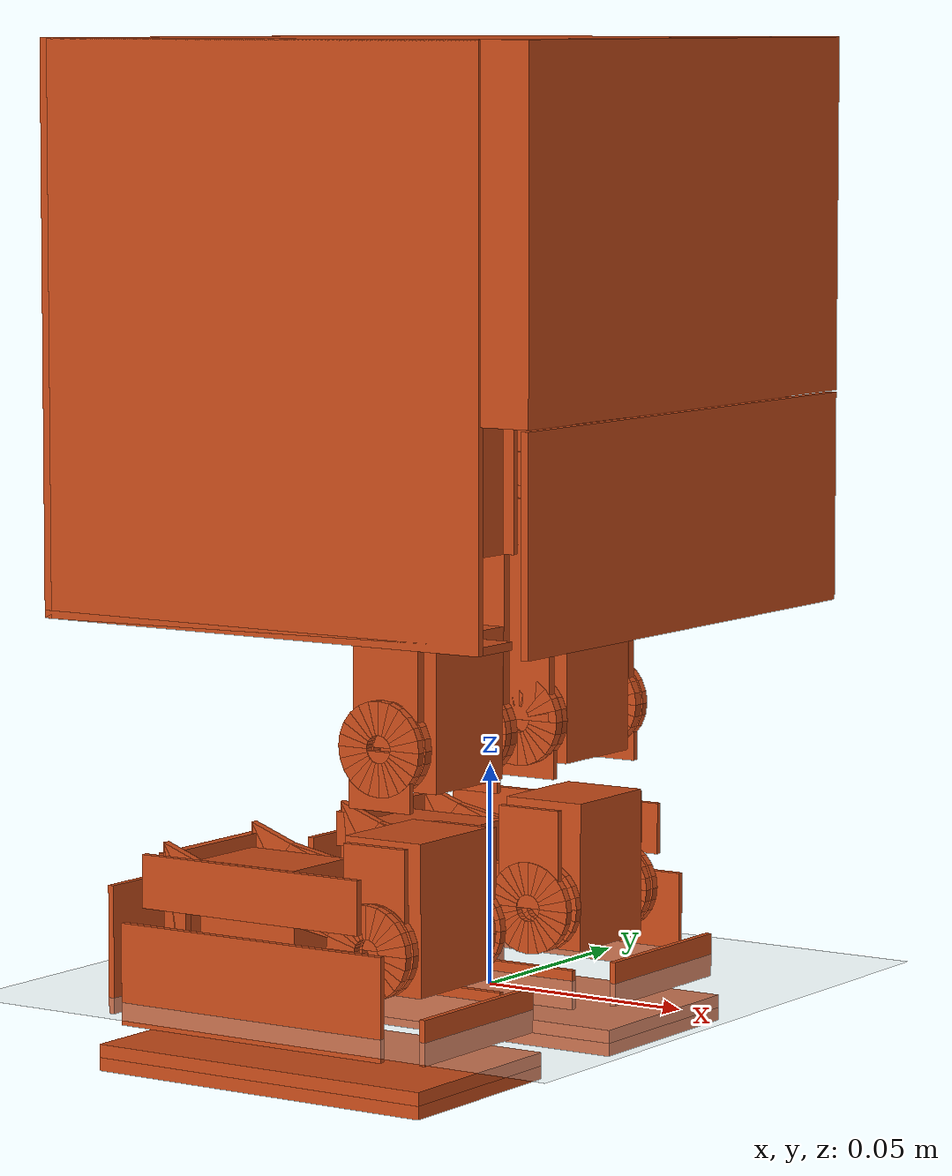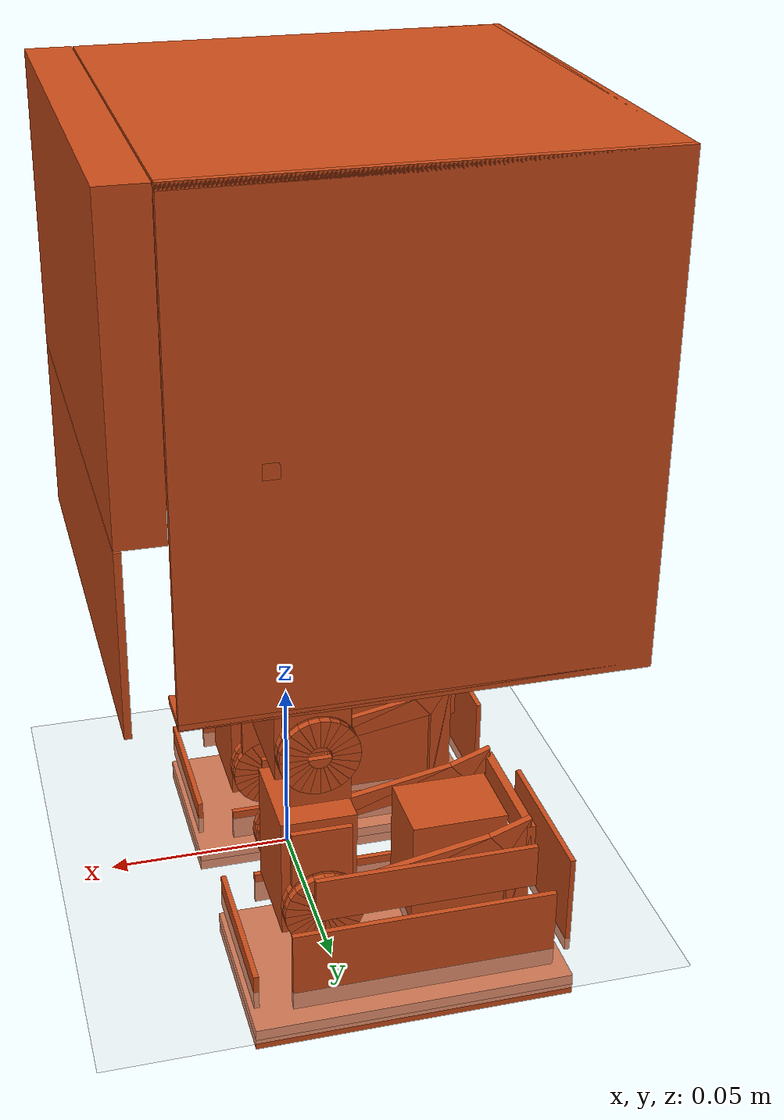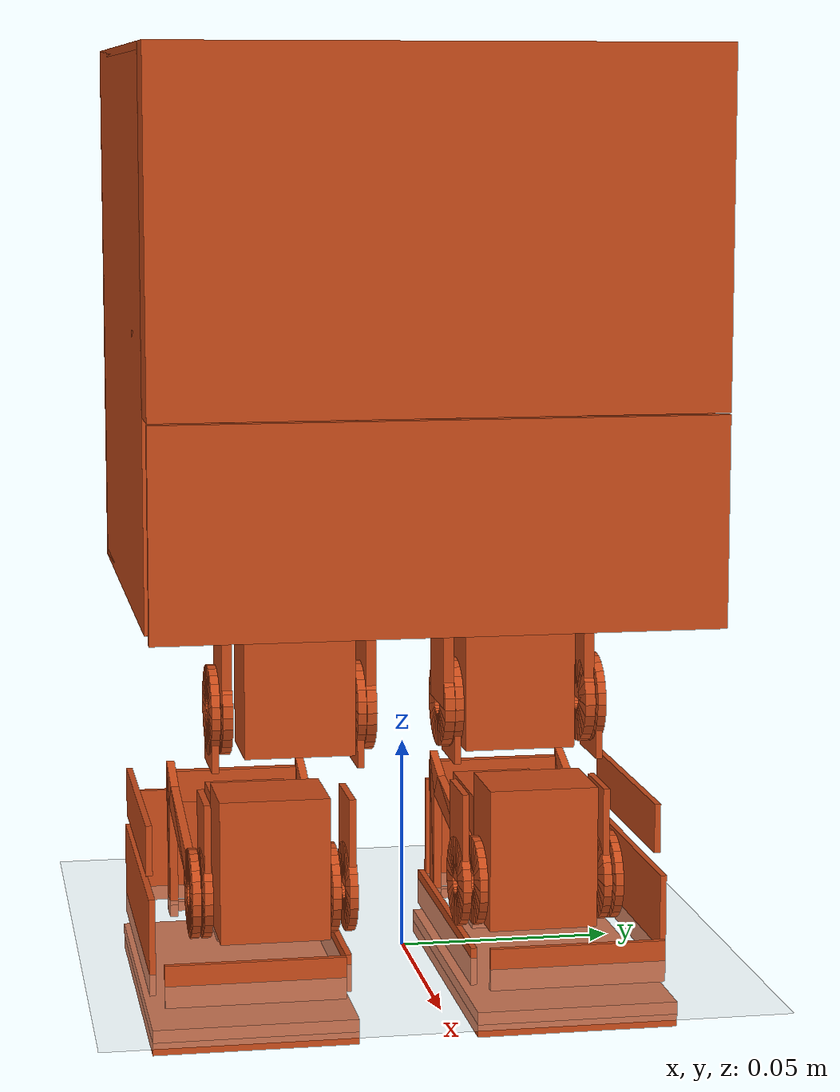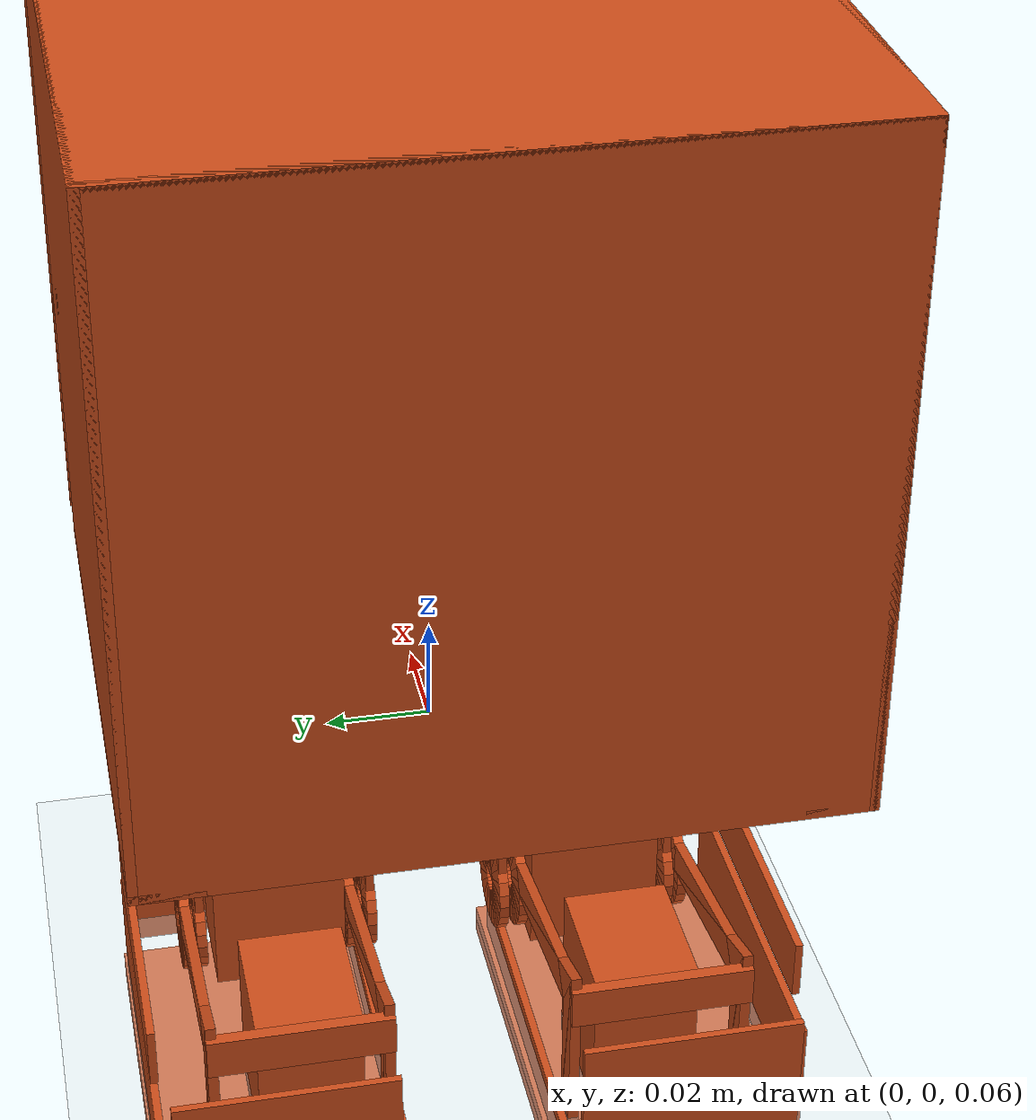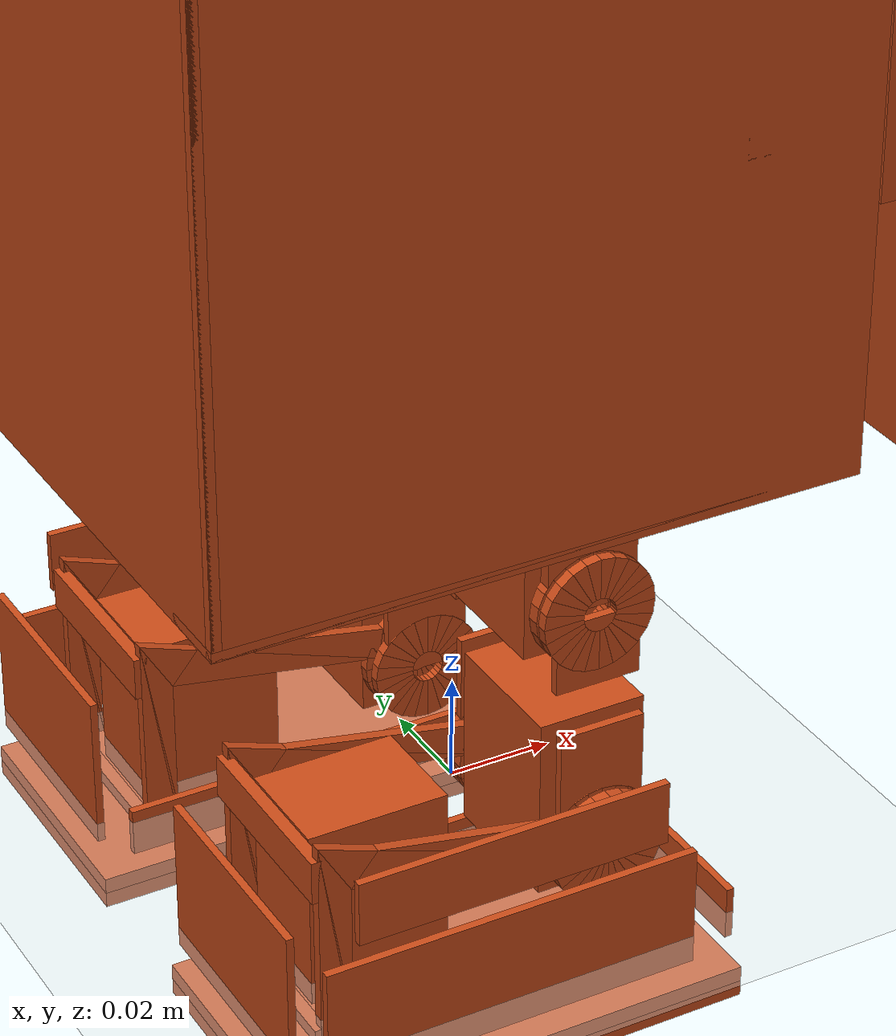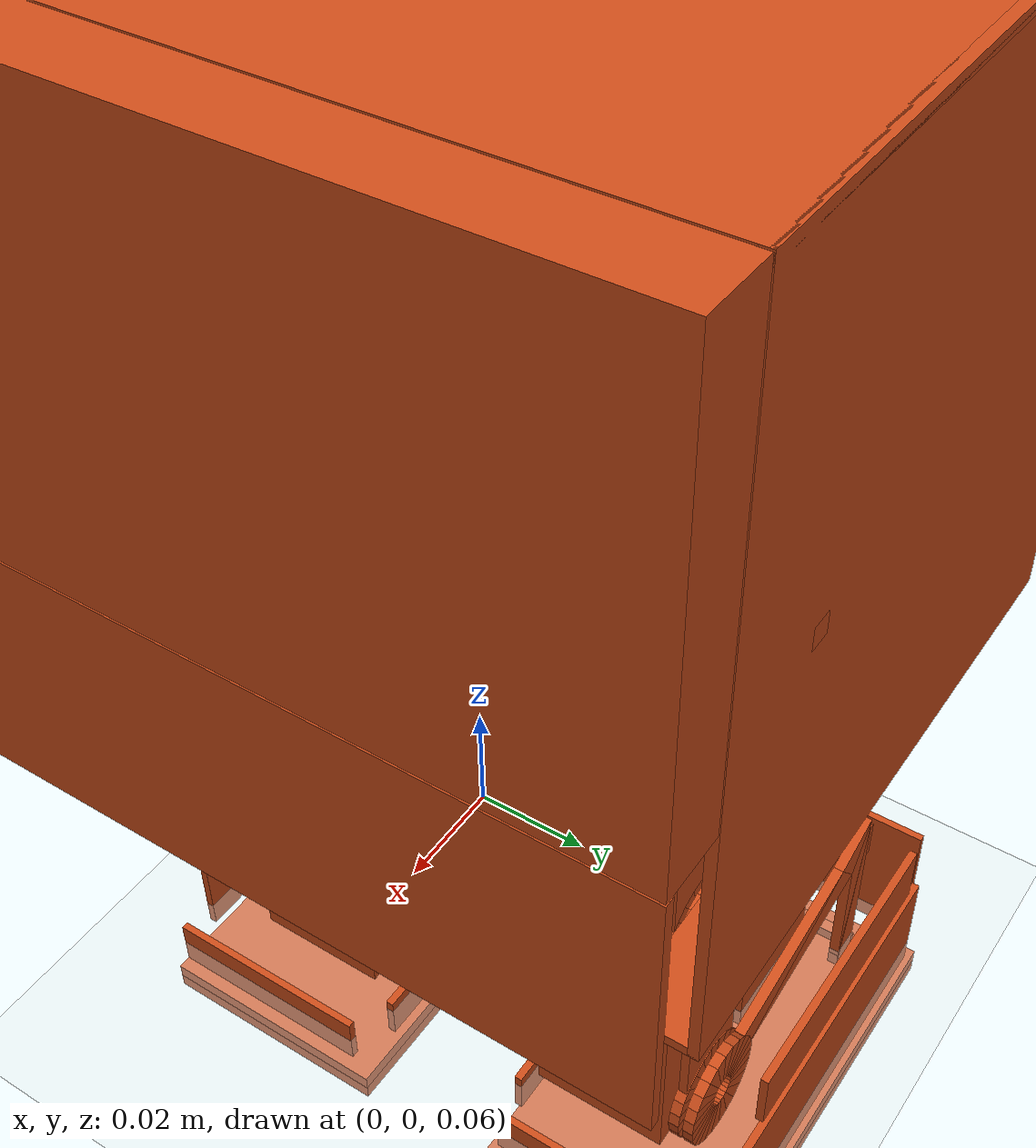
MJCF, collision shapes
<mujoco model="r9-fast-turn-development">
  <compiler angle="radian" meshdir="meshes" inertiafromgeom="false" autolimits="true" />
  <option timestep="0.001" gravity="0 0 -9.81" integrator="implicitfast" solver="Newton" iterations="50" cone="elliptic">
    <flag filterparent="disable" />
  </option>
  <visual>
    <global offwidth="1280" offheight="960" />
    <headlight diffuse=".7 .7 .7" ambient=".3 .3 .3" />
  </visual>
  <statistic center="0 0 .15" extent=".55" />
  <default>
    <default class="joint_defaults">
      <joint type="hinge" limited="true" damping="0.0015" frictionloss="0.006" armature="2e-06" />
    </default>
    <default class="collision">
      <geom contype="1" conaffinity="1" condim="3" group="3" rgba=".8 .3 .1 .35" friction="0.8 .003 .0001" solref=".004 1" solimp=".95 .99 .001" margin="0" mass="0" />
    </default>
  </default>
  <asset>
    <mesh name="body_shroud_mesh" file="body_shroud.stl" scale=".001 .001 .001" />
    <mesh name="rear_cover_mesh" file="rear_cover.stl" scale=".001 .001 .001" />
    <mesh name="Tab5_mesh" file="Tab5.stl" scale=".001 .001 .001" />
    <mesh name="face_0_mesh" file="face_0.stl" scale=".001 .001 .001" />
    <mesh name="face_1_mesh" file="face_1.stl" scale=".001 .001 .001" />
    <mesh name="face_2_mesh" file="face_2.stl" scale=".001 .001 .001" />
    <mesh name="screen_mesh" file="screen.stl" scale=".001 .001 .001" />
    <mesh name="camera_mesh" file="camera.stl" scale=".001 .001 .001" />
    <mesh name="battery_2S_reservation_mesh" file="battery_2S_reservation.stl" scale=".001 .001 .001" />
    <mesh name="dedicated_5V_converter_mesh" file="dedicated_5V_converter.stl" scale=".001 .001 .001" />
    <mesh name="TTL_interface_mesh" file="TTL_interface.stl" scale=".001 .001 .001" />
    <mesh name="cables_and_fasteners_mesh" file="cables_and_fasteners.stl" scale=".001 .001 .001" />
    <mesh name="left_hip_roll_motor_mesh" file="left_hip_roll_motor.stl" scale=".001 .001 .001" />
    <mesh name="left_fixed_roll_cradle_mesh" file="left_fixed_roll_cradle.stl" scale=".001 .001 .001" />
    <mesh name="left_roll_to_pitch_carrier_mesh" file="left_roll_to_pitch_carrier.stl" scale=".001 .001 .001" />
    <mesh name="left_hip_pitch_motor_mesh" file="left_hip_pitch_motor.stl" scale=".001 .001 .001" />
    <mesh name="left_thigh_yoke_mesh" file="left_thigh_yoke.stl" scale=".001 .001 .001" />
    <mesh name="left_knee_motor_mesh" file="left_knee_motor.stl" scale=".001 .001 .001" />
    <mesh name="left_shin_yoke_mesh" file="left_shin_yoke.stl" scale=".001 .001 .001" />
    <mesh name="left_ankle_pitch_motor_mesh" file="left_ankle_pitch_motor.stl" scale=".001 .001 .001" />
    <mesh name="left_ankle_roll_motor_mesh" file="left_ankle_roll_motor.stl" scale=".001 .001 .001" />
    <mesh name="left_ankle_gimbal_mesh" file="left_ankle_gimbal.stl" scale=".001 .001 .001" />
    <mesh name="left_foot_yoke_mesh" file="left_foot_yoke.stl" scale=".001 .001 .001" />
    <mesh name="left_boot_shell_mesh" file="left_boot_shell.stl" scale=".001 .001 .001" />
    <mesh name="left_sole_TPU_mesh" file="left_sole_TPU.stl" scale=".001 .001 .001" />
    <mesh name="right_hip_roll_motor_mesh" file="right_hip_roll_motor.stl" scale=".001 .001 .001" />
    <mesh name="right_fixed_roll_cradle_mesh" file="right_fixed_roll_cradle.stl" scale=".001 .001 .001" />
    <mesh name="right_roll_to_pitch_carrier_mesh" file="right_roll_to_pitch_carrier.stl" scale=".001 .001 .001" />
    <mesh name="right_hip_pitch_motor_mesh" file="right_hip_pitch_motor.stl" scale=".001 .001 .001" />
    <mesh name="right_thigh_yoke_mesh" file="right_thigh_yoke.stl" scale=".001 .001 .001" />
    <mesh name="right_knee_motor_mesh" file="right_knee_motor.stl" scale=".001 .001 .001" />
    <mesh name="right_shin_yoke_mesh" file="right_shin_yoke.stl" scale=".001 .001 .001" />
    <mesh name="right_ankle_pitch_motor_mesh" file="right_ankle_pitch_motor.stl" scale=".001 .001 .001" />
    <mesh name="right_ankle_roll_motor_mesh" file="right_ankle_roll_motor.stl" scale=".001 .001 .001" />
    <mesh name="right_ankle_gimbal_mesh" file="right_ankle_gimbal.stl" scale=".001 .001 .001" />
    <mesh name="right_foot_yoke_mesh" file="right_foot_yoke.stl" scale=".001 .001 .001" />
    <mesh name="right_boot_shell_mesh" file="right_boot_shell.stl" scale=".001 .001 .001" />
    <mesh name="right_sole_TPU_mesh" file="right_sole_TPU.stl" scale=".001 .001 .001" />
    <mesh name="col_left_ankle_gimbal_0_mesh" vertex="-0.008 -0.0155 0.002 -0.007 -0.0155 0.008 -0.044 -0.0155 0.015 -0.008 -0.0135 0.002 -0.007 -0.0135 0.008 -0.044 -0.0135 0.015" />
    <mesh name="col_left_ankle_gimbal_1_mesh" vertex="-0.055 -0.0155 0.019 -0.055 -0.0155 -0.02 -0.049 -0.0155 -0.02 -0.055 -0.0135 0.019 -0.055 -0.0135 -0.02 -0.049 -0.0135 -0.02" />
    <mesh name="col_left_ankle_gimbal_2_mesh" vertex="-0.055 -0.0155 0.019 -0.049 -0.0155 -0.02 -0.049 -0.0155 -0.017 -0.055 -0.0135 0.019 -0.049 -0.0135 -0.02 -0.049 -0.0135 -0.017" />
    <mesh name="col_left_ankle_gimbal_3_mesh" vertex="-0.055 -0.0155 0.019 -0.049 -0.0155 -0.017 -0.049 -0.0155 0.009 -0.055 -0.0135 0.019 -0.049 -0.0135 -0.017 -0.049 -0.0135 0.009" />
    <mesh name="col_left_ankle_gimbal_4_mesh" vertex="-0.044 -0.0155 0.015 -0.055 -0.0155 0.019 -0.049 -0.0155 0.009 -0.044 -0.0135 0.015 -0.055 -0.0135 0.019 -0.049 -0.0135 0.009" />
    <mesh name="col_left_ankle_gimbal_5_mesh" vertex="-0.044 -0.0155 0.015 -0.049 -0.0155 0.009 -0.008 -0.0155 0.002 -0.044 -0.0135 0.015 -0.049 -0.0135 0.009 -0.008 -0.0135 0.002" />
    <mesh name="col_left_ankle_gimbal_6_mesh" vertex="0.0105906040861 -0.0155 0 0.0102297380028 -0.0155 0.00274105003662 0.0029943700615 -0.0155 0.000802339039818 0.0031 -0.0155 0 0.0105906040861 -0.0135 0 0.0102297380028 -0.0135 0.00274105003662 0.0029943700615 -0.0135 0.000802339039818 0.0031 -0.0135 0" />
    <mesh name="col_left_ankle_gimbal_7_mesh" vertex="0.0102297380028 -0.0155 0.00274105003662 0.00917173217998 -0.0155 0.00529530204305 0.00268467875173 -0.0155 0.00155 0.0029943700615 -0.0155 0.000802339039818 0.0102297380028 -0.0135 0.00274105003662 0.00917173217998 -0.0135 0.00529530204305 0.00268467875173 -0.0135 0.00155 0.0029943700615 -0.0135 0.000802339039818" />
    <mesh name="col_left_ankle_gimbal_8_mesh" vertex="0.00917173217998 -0.0155 0.00529530204305 0.00748868796614 -0.0155 0.00748868796614 0.00219203102168 -0.0155 0.00219203102168 0.00268467875173 -0.0155 0.00155 0.00917173217998 -0.0135 0.00529530204305 0.00748868796614 -0.0135 0.00748868796614 0.00219203102168 -0.0135 0.00219203102168 0.00268467875173 -0.0135 0.00155" />
    <mesh name="col_left_ankle_gimbal_9_mesh" vertex="0.00748868796614 -0.0155 0.00748868796614 0.00529530204305 -0.0155 0.00917173217998 0.00155 -0.0155 0.00268467875173 0.00219203102168 -0.0155 0.00219203102168 0.00748868796614 -0.0135 0.00748868796614 0.00529530204305 -0.0135 0.00917173217998 0.00155 -0.0135 0.00268467875173 0.00219203102168 -0.0135 0.00219203102168" />
    <mesh name="col_left_ankle_gimbal_10_mesh" vertex="0.00529530204305 -0.0155 0.00917173217998 0.00274105003662 -0.0155 0.0102297380028 0.000802339039818 -0.0155 0.0029943700615 0.00155 -0.0155 0.00268467875173 0.00529530204305 -0.0135 0.00917173217998 0.00274105003662 -0.0135 0.0102297380028 0.000802339039818 -0.0135 0.0029943700615 0.00155 -0.0135 0.00268467875173" />
    <mesh name="col_left_ankle_gimbal_11_mesh" vertex="0.00274105003662 -0.0155 0.0102297380028 6.48487469753e-19 -0.0155 0.0105906040861 1.89820253868e-19 -0.0155 0.0031 0.000802339039818 -0.0155 0.0029943700615 0.00274105003662 -0.0135 0.0102297380028 6.48487469753e-19 -0.0135 0.0105906040861 1.89820253868e-19 -0.0135 0.0031 0.000802339039818 -0.0135 0.0029943700615" />
    <mesh name="col_left_ankle_gimbal_12_mesh" vertex="6.48487469753e-19 -0.0155 0.0105906040861 -0.00274105003662 -0.0155 0.0102297380028 -0.000802339039818 -0.0155 0.0029943700615 1.89820253868e-19 -0.0155 0.0031 6.48487469753e-19 -0.0135 0.0105906040861 -0.00274105003662 -0.0135 0.0102297380028 -0.000802339039818 -0.0135 0.0029943700615 1.89820253868e-19 -0.0135 0.0031" />
    <mesh name="col_left_ankle_gimbal_13_mesh" vertex="-0.00274105003662 -0.0155 0.0102297380028 -0.00529530204305 -0.0155 0.00917173217998 -0.00155 -0.0155 0.00268467875173 -0.000802339039818 -0.0155 0.0029943700615 -0.00274105003662 -0.0135 0.0102297380028 -0.00529530204305 -0.0135 0.00917173217998 -0.00155 -0.0135 0.00268467875173 -0.000802339039818 -0.0135 0.0029943700615" />
    <mesh name="col_left_ankle_gimbal_14_mesh" vertex="-0.00529530204305 -0.0155 0.00917173217998 -0.00748868796614 -0.0155 0.00748868796614 -0.00219203102168 -0.0155 0.00219203102168 -0.00155 -0.0155 0.00268467875173 -0.00529530204305 -0.0135 0.00917173217998 -0.00748868796614 -0.0135 0.00748868796614 -0.00219203102168 -0.0135 0.00219203102168 -0.00155 -0.0135 0.00268467875173" />
    <mesh name="col_left_ankle_gimbal_15_mesh" vertex="-0.00748868796614 -0.0155 0.00748868796614 -0.00917173217998 -0.0155 0.00529530204305 -0.00268467875173 -0.0155 0.00155 -0.00219203102168 -0.0155 0.00219203102168 -0.00748868796614 -0.0135 0.00748868796614 -0.00917173217998 -0.0135 0.00529530204305 -0.00268467875173 -0.0135 0.00155 -0.00219203102168 -0.0135 0.00219203102168" />
    <mesh name="col_left_ankle_gimbal_16_mesh" vertex="-0.00917173217998 -0.0155 0.00529530204305 -0.0102297380028 -0.0155 0.00274105003662 -0.0029943700615 -0.0155 0.000802339039818 -0.00268467875173 -0.0155 0.00155 -0.00917173217998 -0.0135 0.00529530204305 -0.0102297380028 -0.0135 0.00274105003662 -0.0029943700615 -0.0135 0.000802339039818 -0.00268467875173 -0.0135 0.00155" />
    <mesh name="col_left_ankle_gimbal_17_mesh" vertex="-0.0102297380028 -0.0155 0.00274105003662 -0.0105906040861 -0.0155 1.29697493951e-18 -0.0031 -0.0155 3.79640507736e-19 -0.0029943700615 -0.0155 0.000802339039818 -0.0102297380028 -0.0135 0.00274105003662 -0.0105906040861 -0.0135 1.29697493951e-18 -0.0031 -0.0135 3.79640507736e-19 -0.0029943700615 -0.0135 0.000802339039818" />
    <mesh name="col_left_ankle_gimbal_18_mesh" vertex="-0.0105906040861 -0.0155 1.29697493951e-18 -0.0102297380028 -0.0155 -0.00274105003662 -0.0029943700615 -0.0155 -0.000802339039818 -0.0031 -0.0155 3.79640507736e-19 -0.0105906040861 -0.0135 1.29697493951e-18 -0.0102297380028 -0.0135 -0.00274105003662 -0.0029943700615 -0.0135 -0.000802339039818 -0.0031 -0.0135 3.79640507736e-19" />
    <mesh name="col_left_ankle_gimbal_19_mesh" vertex="-0.0102297380028 -0.0155 -0.00274105003662 -0.00917173217998 -0.0155 -0.00529530204305 -0.00268467875173 -0.0155 -0.00155 -0.0029943700615 -0.0155 -0.000802339039818 -0.0102297380028 -0.0135 -0.00274105003662 -0.00917173217998 -0.0135 -0.00529530204305 -0.00268467875173 -0.0135 -0.00155 -0.0029943700615 -0.0135 -0.000802339039818" />
    <mesh name="col_left_ankle_gimbal_20_mesh" vertex="-0.00917173217998 -0.0155 -0.00529530204305 -0.00748868796614 -0.0155 -0.00748868796614 -0.00219203102168 -0.0155 -0.00219203102168 -0.00268467875173 -0.0155 -0.00155 -0.00917173217998 -0.0135 -0.00529530204305 -0.00748868796614 -0.0135 -0.00748868796614 -0.00219203102168 -0.0135 -0.00219203102168 -0.00268467875173 -0.0135 -0.00155" />
    <mesh name="col_left_ankle_gimbal_21_mesh" vertex="-0.00748868796614 -0.0155 -0.00748868796614 -0.00529530204305 -0.0155 -0.00917173217998 -0.00155 -0.0155 -0.00268467875173 -0.00219203102168 -0.0155 -0.00219203102168 -0.00748868796614 -0.0135 -0.00748868796614 -0.00529530204305 -0.0135 -0.00917173217998 -0.00155 -0.0135 -0.00268467875173 -0.00219203102168 -0.0135 -0.00219203102168" />
    <mesh name="col_left_ankle_gimbal_22_mesh" vertex="-0.00529530204305 -0.0155 -0.00917173217998 -0.00274105003662 -0.0155 -0.0102297380028 -0.000802339039818 -0.0155 -0.0029943700615 -0.00155 -0.0155 -0.00268467875173 -0.00529530204305 -0.0135 -0.00917173217998 -0.00274105003662 -0.0135 -0.0102297380028 -0.000802339039818 -0.0135 -0.0029943700615 -0.00155 -0.0135 -0.00268467875173" />
    <mesh name="col_left_ankle_gimbal_23_mesh" vertex="-0.00274105003662 -0.0155 -0.0102297380028 -1.94546240926e-18 -0.0155 -0.0105906040861 -5.69460761604e-19 -0.0155 -0.0031 -0.000802339039818 -0.0155 -0.0029943700615 -0.00274105003662 -0.0135 -0.0102297380028 -1.94546240926e-18 -0.0135 -0.0105906040861 -5.69460761604e-19 -0.0135 -0.0031 -0.000802339039818 -0.0135 -0.0029943700615" />
    <mesh name="col_left_ankle_gimbal_24_mesh" vertex="-1.94546240926e-18 -0.0155 -0.0105906040861 0.00274105003662 -0.0155 -0.0102297380028 0.000802339039818 -0.0155 -0.0029943700615 -5.69460761604e-19 -0.0155 -0.0031 -1.94546240926e-18 -0.0135 -0.0105906040861 0.00274105003662 -0.0135 -0.0102297380028 0.000802339039818 -0.0135 -0.0029943700615 -5.69460761604e-19 -0.0135 -0.0031" />
    <mesh name="col_left_ankle_gimbal_25_mesh" vertex="0.00274105003662 -0.0155 -0.0102297380028 0.00529530204305 -0.0155 -0.00917173217998 0.00155 -0.0155 -0.00268467875173 0.000802339039818 -0.0155 -0.0029943700615 0.00274105003662 -0.0135 -0.0102297380028 0.00529530204305 -0.0135 -0.00917173217998 0.00155 -0.0135 -0.00268467875173 0.000802339039818 -0.0135 -0.0029943700615" />
    <mesh name="col_left_ankle_gimbal_26_mesh" vertex="0.00529530204305 -0.0155 -0.00917173217998 0.00748868796614 -0.0155 -0.00748868796614 0.00219203102168 -0.0155 -0.00219203102168 0.00155 -0.0155 -0.00268467875173 0.00529530204305 -0.0135 -0.00917173217998 0.00748868796614 -0.0135 -0.00748868796614 0.00219203102168 -0.0135 -0.00219203102168 0.00155 -0.0135 -0.00268467875173" />
    <mesh name="col_left_ankle_gimbal_27_mesh" vertex="0.00748868796614 -0.0155 -0.00748868796614 0.00917173217998 -0.0155 -0.00529530204305 0.00268467875173 -0.0155 -0.00155 0.00219203102168 -0.0155 -0.00219203102168 0.00748868796614 -0.0135 -0.00748868796614 0.00917173217998 -0.0135 -0.00529530204305 0.00268467875173 -0.0135 -0.00155 0.00219203102168 -0.0135 -0.00219203102168" />
    <mesh name="col_left_ankle_gimbal_28_mesh" vertex="0.00917173217998 -0.0155 -0.00529530204305 0.0102297380028 -0.0155 -0.00274105003662 0.0029943700615 -0.0155 -0.000802339039818 0.00268467875173 -0.0155 -0.00155 0.00917173217998 -0.0135 -0.00529530204305 0.0102297380028 -0.0135 -0.00274105003662 0.0029943700615 -0.0135 -0.000802339039818 0.00268467875173 -0.0135 -0.00155" />
    <mesh name="col_left_ankle_gimbal_29_mesh" vertex="0.0102297380028 -0.0155 -0.00274105003662 0.0105906040861 -0.0155 -2.59394987901e-18 0.0031 -0.0155 -7.59281015471e-19 0.0029943700615 -0.0155 -0.000802339039818 0.0102297380028 -0.0135 -0.00274105003662 0.0105906040861 -0.0135 -2.59394987901e-18 0.0031 -0.0135 -7.59281015471e-19 0.0029943700615 -0.0135 -0.000802339039818" />
    <mesh name="col_left_ankle_gimbal_30_mesh" vertex="-0.008 0.0174 0.002 -0.007 0.0174 0.008 -0.044 0.0174 0.015 -0.008 0.0194 0.002 -0.007 0.0194 0.008 -0.044 0.0194 0.015" />
    <mesh name="col_left_ankle_gimbal_31_mesh" vertex="-0.055 0.0174 0.019 -0.055 0.0174 -0.02 -0.049 0.0174 -0.02 -0.055 0.0194 0.019 -0.055 0.0194 -0.02 -0.049 0.0194 -0.02" />
    <mesh name="col_left_ankle_gimbal_32_mesh" vertex="-0.055 0.0174 0.019 -0.049 0.0174 -0.02 -0.049 0.0174 -0.017 -0.055 0.0194 0.019 -0.049 0.0194 -0.02 -0.049 0.0194 -0.017" />
    <mesh name="col_left_ankle_gimbal_33_mesh" vertex="-0.055 0.0174 0.019 -0.049 0.0174 -0.017 -0.049 0.0174 0.009 -0.055 0.0194 0.019 -0.049 0.0194 -0.017 -0.049 0.0194 0.009" />
    <mesh name="col_left_ankle_gimbal_34_mesh" vertex="-0.044 0.0174 0.015 -0.055 0.0174 0.019 -0.049 0.0174 0.009 -0.044 0.0194 0.015 -0.055 0.0194 0.019 -0.049 0.0194 0.009" />
    <mesh name="col_left_ankle_gimbal_35_mesh" vertex="-0.044 0.0174 0.015 -0.049 0.0174 0.009 -0.008 0.0174 0.002 -0.044 0.0194 0.015 -0.049 0.0194 0.009 -0.008 0.0194 0.002" />
    <mesh name="col_left_ankle_gimbal_36_mesh" vertex="0.0105906040861 0.0174 0 0.0102297380028 0.0174 0.00274105003662 0.0029943700615 0.0174 0.000802339039818 0.0031 0.0174 0 0.0105906040861 0.0194 0 0.0102297380028 0.0194 0.00274105003662 0.0029943700615 0.0194 0.000802339039818 0.0031 0.0194 0" />
    <mesh name="col_left_ankle_gimbal_37_mesh" vertex="0.0102297380028 0.0174 0.00274105003662 0.00917173217998 0.0174 0.00529530204305 0.00268467875173 0.0174 0.00155 0.0029943700615 0.0174 0.000802339039818 0.0102297380028 0.0194 0.00274105003662 0.00917173217998 0.0194 0.00529530204305 0.00268467875173 0.0194 0.00155 0.0029943700615 0.0194 0.000802339039818" />
    <mesh name="col_left_ankle_gimbal_38_mesh" vertex="0.00917173217998 0.0174 0.00529530204305 0.00748868796614 0.0174 0.00748868796614 0.00219203102168 0.0174 0.00219203102168 0.00268467875173 0.0174 0.00155 0.00917173217998 0.0194 0.00529530204305 0.00748868796614 0.0194 0.00748868796614 0.00219203102168 0.0194 0.00219203102168 0.00268467875173 0.0194 0.00155" />
    <mesh name="col_left_ankle_gimbal_39_mesh" vertex="0.00748868796614 0.0174 0.00748868796614 0.00529530204305 0.0174 0.00917173217998 0.00155 0.0174 0.00268467875173 0.00219203102168 0.0174 0.00219203102168 0.00748868796614 0.0194 0.00748868796614 0.00529530204305 0.0194 0.00917173217998 0.00155 0.0194 0.00268467875173 0.00219203102168 0.0194 0.00219203102168" />
    <mesh name="col_left_ankle_gimbal_40_mesh" vertex="0.00529530204305 0.0174 0.00917173217998 0.00274105003662 0.0174 0.0102297380028 0.000802339039818 0.0174 0.0029943700615 0.00155 0.0174 0.00268467875173 0.00529530204305 0.0194 0.00917173217998 0.00274105003662 0.0194 0.0102297380028 0.000802339039818 0.0194 0.0029943700615 0.00155 0.0194 0.00268467875173" />
    <mesh name="col_left_ankle_gimbal_41_mesh" vertex="0.00274105003662 0.0174 0.0102297380028 6.48487469753e-19 0.0174 0.0105906040861 1.89820253868e-19 0.0174 0.0031 0.000802339039818 0.0174 0.0029943700615 0.00274105003662 0.0194 0.0102297380028 6.48487469753e-19 0.0194 0.0105906040861 1.89820253868e-19 0.0194 0.0031 0.000802339039818 0.0194 0.0029943700615" />
    <mesh name="col_left_ankle_gimbal_42_mesh" vertex="6.48487469753e-19 0.0174 0.0105906040861 -0.00274105003662 0.0174 0.0102297380028 -0.000802339039818 0.0174 0.0029943700615 1.89820253868e-19 0.0174 0.0031 6.48487469753e-19 0.0194 0.0105906040861 -0.00274105003662 0.0194 0.0102297380028 -0.000802339039818 0.0194 0.0029943700615 1.89820253868e-19 0.0194 0.0031" />
    <mesh name="col_left_ankle_gimbal_43_mesh" vertex="-0.00274105003662 0.0174 0.0102297380028 -0.00529530204305 0.0174 0.00917173217998 -0.00155 0.0174 0.00268467875173 -0.000802339039818 0.0174 0.0029943700615 -0.00274105003662 0.0194 0.0102297380028 -0.00529530204305 0.0194 0.00917173217998 -0.00155 0.0194 0.00268467875173 -0.000802339039818 0.0194 0.0029943700615" />
    <mesh name="col_left_ankle_gimbal_44_mesh" vertex="-0.00529530204305 0.0174 0.00917173217998 -0.00748868796614 0.0174 0.00748868796614 -0.00219203102168 0.0174 0.00219203102168 -0.00155 0.0174 0.00268467875173 -0.00529530204305 0.0194 0.00917173217998 -0.00748868796614 0.0194 0.00748868796614 -0.00219203102168 0.0194 0.00219203102168 -0.00155 0.0194 0.00268467875173" />
    <mesh name="col_left_ankle_gimbal_45_mesh" vertex="-0.00748868796614 0.0174 0.00748868796614 -0.00917173217998 0.0174 0.00529530204305 -0.00268467875173 0.0174 0.00155 -0.00219203102168 0.0174 0.00219203102168 -0.00748868796614 0.0194 0.00748868796614 -0.00917173217998 0.0194 0.00529530204305 -0.00268467875173 0.0194 0.00155 -0.00219203102168 0.0194 0.00219203102168" />
    <mesh name="col_left_ankle_gimbal_46_mesh" vertex="-0.00917173217998 0.0174 0.00529530204305 -0.0102297380028 0.0174 0.00274105003662 -0.0029943700615 0.0174 0.000802339039818 -0.00268467875173 0.0174 0.00155 -0.00917173217998 0.0194 0.00529530204305 -0.0102297380028 0.0194 0.00274105003662 -0.0029943700615 0.0194 0.000802339039818 -0.00268467875173 0.0194 0.00155" />
    <mesh name="col_left_ankle_gimbal_47_mesh" vertex="-0.0102297380028 0.0174 0.00274105003662 -0.0105906040861 0.0174 1.29697493951e-18 -0.0031 0.0174 3.79640507736e-19 -0.0029943700615 0.0174 0.000802339039818 -0.0102297380028 0.0194 0.00274105003662 -0.0105906040861 0.0194 1.29697493951e-18 -0.0031 0.0194 3.79640507736e-19 -0.0029943700615 0.0194 0.000802339039818" />
    <mesh name="col_left_ankle_gimbal_48_mesh" vertex="-0.0105906040861 0.0174 1.29697493951e-18 -0.0102297380028 0.0174 -0.00274105003662 -0.0029943700615 0.0174 -0.000802339039818 -0.0031 0.0174 3.79640507736e-19 -0.0105906040861 0.0194 1.29697493951e-18 -0.0102297380028 0.0194 -0.00274105003662 -0.0029943700615 0.0194 -0.000802339039818 -0.0031 0.0194 3.79640507736e-19" />
    <mesh name="col_left_ankle_gimbal_49_mesh" vertex="-0.0102297380028 0.0174 -0.00274105003662 -0.00917173217998 0.0174 -0.00529530204305 -0.00268467875173 0.0174 -0.00155 -0.0029943700615 0.0174 -0.000802339039818 -0.0102297380028 0.0194 -0.00274105003662 -0.00917173217998 0.0194 -0.00529530204305 -0.00268467875173 0.0194 -0.00155 -0.0029943700615 0.0194 -0.000802339039818" />
    <mesh name="col_left_ankle_gimbal_50_mesh" vertex="-0.00917173217998 0.0174 -0.00529530204305 -0.00748868796614 0.0174 -0.00748868796614 -0.00219203102168 0.0174 -0.00219203102168 -0.00268467875173 0.0174 -0.00155 -0.00917173217998 0.0194 -0.00529530204305 -0.00748868796614 0.0194 -0.00748868796614 -0.00219203102168 0.0194 -0.00219203102168 -0.00268467875173 0.0194 -0.00155" />
    <mesh name="col_left_ankle_gimbal_51_mesh" vertex="-0.00748868796614 0.0174 -0.00748868796614 -0.00529530204305 0.0174 -0.00917173217998 -0.00155 0.0174 -0.00268467875173 -0.00219203102168 0.0174 -0.00219203102168 -0.00748868796614 0.0194 -0.00748868796614 -0.00529530204305 0.0194 -0.00917173217998 -0.00155 0.0194 -0.00268467875173 -0.00219203102168 0.0194 -0.00219203102168" />
    <mesh name="col_left_ankle_gimbal_52_mesh" vertex="-0.00529530204305 0.0174 -0.00917173217998 -0.00274105003662 0.0174 -0.0102297380028 -0.000802339039818 0.0174 -0.0029943700615 -0.00155 0.0174 -0.00268467875173 -0.00529530204305 0.0194 -0.00917173217998 -0.00274105003662 0.0194 -0.0102297380028 -0.000802339039818 0.0194 -0.0029943700615 -0.00155 0.0194 -0.00268467875173" />
    <mesh name="col_left_ankle_gimbal_53_mesh" vertex="-0.00274105003662 0.0174 -0.0102297380028 -1.94546240926e-18 0.0174 -0.0105906040861 -5.69460761604e-19 0.0174 -0.0031 -0.000802339039818 0.0174 -0.0029943700615 -0.00274105003662 0.0194 -0.0102297380028 -1.94546240926e-18 0.0194 -0.0105906040861 -5.69460761604e-19 0.0194 -0.0031 -0.000802339039818 0.0194 -0.0029943700615" />
    <mesh name="col_left_ankle_gimbal_54_mesh" vertex="-1.94546240926e-18 0.0174 -0.0105906040861 0.00274105003662 0.0174 -0.0102297380028 0.000802339039818 0.0174 -0.0029943700615 -5.69460761604e-19 0.0174 -0.0031 -1.94546240926e-18 0.0194 -0.0105906040861 0.00274105003662 0.0194 -0.0102297380028 0.000802339039818 0.0194 -0.0029943700615 -5.69460761604e-19 0.0194 -0.0031" />
    <mesh name="col_left_ankle_gimbal_55_mesh" vertex="0.00274105003662 0.0174 -0.0102297380028 0.00529530204305 0.0174 -0.00917173217998 0.00155 0.0174 -0.00268467875173 0.000802339039818 0.0174 -0.0029943700615 0.00274105003662 0.0194 -0.0102297380028 0.00529530204305 0.0194 -0.00917173217998 0.00155 0.0194 -0.00268467875173 0.000802339039818 0.0194 -0.0029943700615" />
    <mesh name="col_left_ankle_gimbal_56_mesh" vertex="0.00529530204305 0.0174 -0.00917173217998 0.00748868796614 0.0174 -0.00748868796614 0.00219203102168 0.0174 -0.00219203102168 0.00155 0.0174 -0.00268467875173 0.00529530204305 0.0194 -0.00917173217998 0.00748868796614 0.0194 -0.00748868796614 0.00219203102168 0.0194 -0.00219203102168 0.00155 0.0194 -0.00268467875173" />
    <mesh name="col_left_ankle_gimbal_57_mesh" vertex="0.00748868796614 0.0174 -0.00748868796614 0.00917173217998 0.0174 -0.00529530204305 0.00268467875173 0.0174 -0.00155 0.00219203102168 0.0174 -0.00219203102168 0.00748868796614 0.0194 -0.00748868796614 0.00917173217998 0.0194 -0.00529530204305 0.00268467875173 0.0194 -0.00155 0.00219203102168 0.0194 -0.00219203102168" />
    <mesh name="col_left_ankle_gimbal_58_mesh" vertex="0.00917173217998 0.0174 -0.00529530204305 0.0102297380028 0.0174 -0.00274105003662 0.0029943700615 0.0174 -0.000802339039818 0.00268467875173 0.0174 -0.00155 0.00917173217998 0.0194 -0.00529530204305 0.0102297380028 0.0194 -0.00274105003662 0.0029943700615 0.0194 -0.000802339039818 0.00268467875173 0.0194 -0.00155" />
    <mesh name="col_left_ankle_gimbal_59_mesh" vertex="0.0102297380028 0.0174 -0.00274105003662 0.0105906040861 0.0174 -2.59394987901e-18 0.0031 0.0174 -7.59281015471e-19 0.0029943700615 0.0174 -0.000802339039818 0.0102297380028 0.0194 -0.00274105003662 0.0105906040861 0.0194 -2.59394987901e-18 0.0031 0.0194 -7.59281015471e-19 0.0029943700615 0.0194 -0.000802339039818" />
    <mesh name="col_left_ankle_gimbal_60_mesh" vertex="-0.0562 -0.0155 0.0085 -0.0562 -0.0155 0.0165 -0.0562 0.0194 0.0085 -0.0562 0.0194 0.0165 -0.0538 -0.0155 0.0085 -0.0538 -0.0155 0.0165 -0.0538 0.0194 0.0085 -0.0538 0.0194 0.0165" />
    <mesh name="col_left_ankle_gimbal_61_mesh" vertex="-0.0562 -0.0155 -0.02 -0.0562 -0.0155 -0.0176 -0.0562 0.0194 -0.02 -0.0562 0.0194 -0.0176 -0.0538 -0.0155 -0.02 -0.0538 -0.0155 -0.0176 -0.0538 0.0194 -0.02 -0.0538 0.0194 -0.0176" />
    <mesh name="col_right_ankle_gimbal_0_mesh" vertex="-0.008 0.0135 0.002 -0.007 0.0135 0.008 -0.044 0.0135 0.015 -0.008 0.0155 0.002 -0.007 0.0155 0.008 -0.044 0.0155 0.015" />
    <mesh name="col_right_ankle_gimbal_1_mesh" vertex="-0.055 0.0135 0.019 -0.055 0.0135 -0.02 -0.049 0.0135 -0.02 -0.055 0.0155 0.019 -0.055 0.0155 -0.02 -0.049 0.0155 -0.02" />
    <mesh name="col_right_ankle_gimbal_2_mesh" vertex="-0.055 0.0135 0.019 -0.049 0.0135 -0.02 -0.049 0.0135 -0.017 -0.055 0.0155 0.019 -0.049 0.0155 -0.02 -0.049 0.0155 -0.017" />
    <mesh name="col_right_ankle_gimbal_3_mesh" vertex="-0.055 0.0135 0.019 -0.049 0.0135 -0.017 -0.049 0.0135 0.009 -0.055 0.0155 0.019 -0.049 0.0155 -0.017 -0.049 0.0155 0.009" />
    <mesh name="col_right_ankle_gimbal_4_mesh" vertex="-0.044 0.0135 0.015 -0.055 0.0135 0.019 -0.049 0.0135 0.009 -0.044 0.0155 0.015 -0.055 0.0155 0.019 -0.049 0.0155 0.009" />
    <mesh name="col_right_ankle_gimbal_5_mesh" vertex="-0.044 0.0135 0.015 -0.049 0.0135 0.009 -0.008 0.0135 0.002 -0.044 0.0155 0.015 -0.049 0.0155 0.009 -0.008 0.0155 0.002" />
    <mesh name="col_right_ankle_gimbal_6_mesh" vertex="0.0105906040861 0.0135 0 0.0102297380028 0.0135 0.00274105003662 0.0029943700615 0.0135 0.000802339039818 0.0031 0.0135 0 0.0105906040861 0.0155 0 0.0102297380028 0.0155 0.00274105003662 0.0029943700615 0.0155 0.000802339039818 0.0031 0.0155 0" />
    <mesh name="col_right_ankle_gimbal_7_mesh" vertex="0.0102297380028 0.0135 0.00274105003662 0.00917173217998 0.0135 0.00529530204305 0.00268467875173 0.0135 0.00155 0.0029943700615 0.0135 0.000802339039818 0.0102297380028 0.0155 0.00274105003662 0.00917173217998 0.0155 0.00529530204305 0.00268467875173 0.0155 0.00155 0.0029943700615 0.0155 0.000802339039818" />
    <mesh name="col_right_ankle_gimbal_8_mesh" vertex="0.00917173217998 0.0135 0.00529530204305 0.00748868796614 0.0135 0.00748868796614 0.00219203102168 0.0135 0.00219203102168 0.00268467875173 0.0135 0.00155 0.00917173217998 0.0155 0.00529530204305 0.00748868796614 0.0155 0.00748868796614 0.00219203102168 0.0155 0.00219203102168 0.00268467875173 0.0155 0.00155" />
    <mesh name="col_right_ankle_gimbal_9_mesh" vertex="0.00748868796614 0.0135 0.00748868796614 0.00529530204305 0.0135 0.00917173217998 0.00155 0.0135 0.00268467875173 0.00219203102168 0.0135 0.00219203102168 0.00748868796614 0.0155 0.00748868796614 0.00529530204305 0.0155 0.00917173217998 0.00155 0.0155 0.00268467875173 0.00219203102168 0.0155 0.00219203102168" />
    <mesh name="col_right_ankle_gimbal_10_mesh" vertex="0.00529530204305 0.0135 0.00917173217998 0.00274105003662 0.0135 0.0102297380028 0.000802339039818 0.0135 0.0029943700615 0.00155 0.0135 0.00268467875173 0.00529530204305 0.0155 0.00917173217998 0.00274105003662 0.0155 0.0102297380028 0.000802339039818 0.0155 0.0029943700615 0.00155 0.0155 0.00268467875173" />
    <mesh name="col_right_ankle_gimbal_11_mesh" vertex="0.00274105003662 0.0135 0.0102297380028 6.48487469753e-19 0.0135 0.0105906040861 1.89820253868e-19 0.0135 0.0031 0.000802339039818 0.0135 0.0029943700615 0.00274105003662 0.0155 0.0102297380028 6.48487469753e-19 0.0155 0.0105906040861 1.89820253868e-19 0.0155 0.0031 0.000802339039818 0.0155 0.0029943700615" />
    <mesh name="col_right_ankle_gimbal_12_mesh" vertex="6.48487469753e-19 0.0135 0.0105906040861 -0.00274105003662 0.0135 0.0102297380028 -0.000802339039818 0.0135 0.0029943700615 1.89820253868e-19 0.0135 0.0031 6.48487469753e-19 0.0155 0.0105906040861 -0.00274105003662 0.0155 0.0102297380028 -0.000802339039818 0.0155 0.0029943700615 1.89820253868e-19 0.0155 0.0031" />
    <mesh name="col_right_ankle_gimbal_13_mesh" vertex="-0.00274105003662 0.0135 0.0102297380028 -0.00529530204305 0.0135 0.00917173217998 -0.00155 0.0135 0.00268467875173 -0.000802339039818 0.0135 0.0029943700615 -0.00274105003662 0.0155 0.0102297380028 -0.00529530204305 0.0155 0.00917173217998 -0.00155 0.0155 0.00268467875173 -0.000802339039818 0.0155 0.0029943700615" />
    <mesh name="col_right_ankle_gimbal_14_mesh" vertex="-0.00529530204305 0.0135 0.00917173217998 -0.00748868796614 0.0135 0.00748868796614 -0.00219203102168 0.0135 0.00219203102168 -0.00155 0.0135 0.00268467875173 -0.00529530204305 0.0155 0.00917173217998 -0.00748868796614 0.0155 0.00748868796614 -0.00219203102168 0.0155 0.00219203102168 -0.00155 0.0155 0.00268467875173" />
    <mesh name="col_right_ankle_gimbal_15_mesh" vertex="-0.00748868796614 0.0135 0.00748868796614 -0.00917173217998 0.0135 0.00529530204305 -0.00268467875173 0.0135 0.00155 -0.00219203102168 0.0135 0.00219203102168 -0.00748868796614 0.0155 0.00748868796614 -0.00917173217998 0.0155 0.00529530204305 -0.00268467875173 0.0155 0.00155 -0.00219203102168 0.0155 0.00219203102168" />
    <mesh name="col_right_ankle_gimbal_16_mesh" vertex="-0.00917173217998 0.0135 0.00529530204305 -0.0102297380028 0.0135 0.00274105003662 -0.0029943700615 0.0135 0.000802339039818 -0.00268467875173 0.0135 0.00155 -0.00917173217998 0.0155 0.00529530204305 -0.0102297380028 0.0155 0.00274105003662 -0.0029943700615 0.0155 0.000802339039818 -0.00268467875173 0.0155 0.00155" />
    <mesh name="col_right_ankle_gimbal_17_mesh" vertex="-0.0102297380028 0.0135 0.00274105003662 -0.0105906040861 0.0135 1.29697493951e-18 -0.0031 0.0135 3.79640507736e-19 -0.0029943700615 0.0135 0.000802339039818 -0.0102297380028 0.0155 0.00274105003662 -0.0105906040861 0.0155 1.29697493951e-18 -0.0031 0.0155 3.79640507736e-19 -0.0029943700615 0.0155 0.000802339039818" />
    <mesh name="col_right_ankle_gimbal_18_mesh" vertex="-0.0105906040861 0.0135 1.29697493951e-18 -0.0102297380028 0.0135 -0.00274105003662 -0.0029943700615 0.0135 -0.000802339039818 -0.0031 0.0135 3.79640507736e-19 -0.0105906040861 0.0155 1.29697493951e-18 -0.0102297380028 0.0155 -0.00274105003662 -0.0029943700615 0.0155 -0.000802339039818 -0.0031 0.0155 3.79640507736e-19" />
    <mesh name="col_right_ankle_gimbal_19_mesh" vertex="-0.0102297380028 0.0135 -0.00274105003662 -0.00917173217998 0.0135 -0.00529530204305 -0.00268467875173 0.0135 -0.00155 -0.0029943700615 0.0135 -0.000802339039818 -0.0102297380028 0.0155 -0.00274105003662 -0.00917173217998 0.0155 -0.00529530204305 -0.00268467875173 0.0155 -0.00155 -0.0029943700615 0.0155 -0.000802339039818" />
    <mesh name="col_right_ankle_gimbal_20_mesh" vertex="-0.00917173217998 0.0135 -0.00529530204305 -0.00748868796614 0.0135 -0.00748868796614 -0.00219203102168 0.0135 -0.00219203102168 -0.00268467875173 0.0135 -0.00155 -0.00917173217998 0.0155 -0.00529530204305 -0.00748868796614 0.0155 -0.00748868796614 -0.00219203102168 0.0155 -0.00219203102168 -0.00268467875173 0.0155 -0.00155" />
    <mesh name="col_right_ankle_gimbal_21_mesh" vertex="-0.00748868796614 0.0135 -0.00748868796614 -0.00529530204305 0.0135 -0.00917173217998 -0.00155 0.0135 -0.00268467875173 -0.00219203102168 0.0135 -0.00219203102168 -0.00748868796614 0.0155 -0.00748868796614 -0.00529530204305 0.0155 -0.00917173217998 -0.00155 0.0155 -0.00268467875173 -0.00219203102168 0.0155 -0.00219203102168" />
    <mesh name="col_right_ankle_gimbal_22_mesh" vertex="-0.00529530204305 0.0135 -0.00917173217998 -0.00274105003662 0.0135 -0.0102297380028 -0.000802339039818 0.0135 -0.0029943700615 -0.00155 0.0135 -0.00268467875173 -0.00529530204305 0.0155 -0.00917173217998 -0.00274105003662 0.0155 -0.0102297380028 -0.000802339039818 0.0155 -0.0029943700615 -0.00155 0.0155 -0.00268467875173" />
    <mesh name="col_right_ankle_gimbal_23_mesh" vertex="-0.00274105003662 0.0135 -0.0102297380028 -1.94546240926e-18 0.0135 -0.0105906040861 -5.69460761604e-19 0.0135 -0.0031 -0.000802339039818 0.0135 -0.0029943700615 -0.00274105003662 0.0155 -0.0102297380028 -1.94546240926e-18 0.0155 -0.0105906040861 -5.69460761604e-19 0.0155 -0.0031 -0.000802339039818 0.0155 -0.0029943700615" />
    <mesh name="col_right_ankle_gimbal_24_mesh" vertex="-1.94546240926e-18 0.0135 -0.0105906040861 0.00274105003662 0.0135 -0.0102297380028 0.000802339039818 0.0135 -0.0029943700615 -5.69460761604e-19 0.0135 -0.0031 -1.94546240926e-18 0.0155 -0.0105906040861 0.00274105003662 0.0155 -0.0102297380028 0.000802339039818 0.0155 -0.0029943700615 -5.69460761604e-19 0.0155 -0.0031" />
    <mesh name="col_right_ankle_gimbal_25_mesh" vertex="0.00274105003662 0.0135 -0.0102297380028 0.00529530204305 0.0135 -0.00917173217998 0.00155 0.0135 -0.00268467875173 0.000802339039818 0.0135 -0.0029943700615 0.00274105003662 0.0155 -0.0102297380028 0.00529530204305 0.0155 -0.00917173217998 0.00155 0.0155 -0.00268467875173 0.000802339039818 0.0155 -0.0029943700615" />
    <mesh name="col_right_ankle_gimbal_26_mesh" vertex="0.00529530204305 0.0135 -0.00917173217998 0.00748868796614 0.0135 -0.00748868796614 0.00219203102168 0.0135 -0.00219203102168 0.00155 0.0135 -0.00268467875173 0.00529530204305 0.0155 -0.00917173217998 0.00748868796614 0.0155 -0.00748868796614 0.00219203102168 0.0155 -0.00219203102168 0.00155 0.0155 -0.00268467875173" />
    <mesh name="col_right_ankle_gimbal_27_mesh" vertex="0.00748868796614 0.0135 -0.00748868796614 0.00917173217998 0.0135 -0.00529530204305 0.00268467875173 0.0135 -0.00155 0.00219203102168 0.0135 -0.00219203102168 0.00748868796614 0.0155 -0.00748868796614 0.00917173217998 0.0155 -0.00529530204305 0.00268467875173 0.0155 -0.00155 0.00219203102168 0.0155 -0.00219203102168" />
    <mesh name="col_right_ankle_gimbal_28_mesh" vertex="0.00917173217998 0.0135 -0.00529530204305 0.0102297380028 0.0135 -0.00274105003662 0.0029943700615 0.0135 -0.000802339039818 0.00268467875173 0.0135 -0.00155 0.00917173217998 0.0155 -0.00529530204305 0.0102297380028 0.0155 -0.00274105003662 0.0029943700615 0.0155 -0.000802339039818 0.00268467875173 0.0155 -0.00155" />
    <mesh name="col_right_ankle_gimbal_29_mesh" vertex="0.0102297380028 0.0135 -0.00274105003662 0.0105906040861 0.0135 -2.59394987901e-18 0.0031 0.0135 -7.59281015471e-19 0.0029943700615 0.0135 -0.000802339039818 0.0102297380028 0.0155 -0.00274105003662 0.0105906040861 0.0155 -2.59394987901e-18 0.0031 0.0155 -7.59281015471e-19 0.0029943700615 0.0155 -0.000802339039818" />
    <mesh name="col_right_ankle_gimbal_30_mesh" vertex="-0.008 -0.0194 0.002 -0.007 -0.0194 0.008 -0.044 -0.0194 0.015 -0.008 -0.0174 0.002 -0.007 -0.0174 0.008 -0.044 -0.0174 0.015" />
    <mesh name="col_right_ankle_gimbal_31_mesh" vertex="-0.055 -0.0194 0.019 -0.055 -0.0194 -0.02 -0.049 -0.0194 -0.02 -0.055 -0.0174 0.019 -0.055 -0.0174 -0.02 -0.049 -0.0174 -0.02" />
    <mesh name="col_right_ankle_gimbal_32_mesh" vertex="-0.055 -0.0194 0.019 -0.049 -0.0194 -0.02 -0.049 -0.0194 -0.017 -0.055 -0.0174 0.019 -0.049 -0.0174 -0.02 -0.049 -0.0174 -0.017" />
    <mesh name="col_right_ankle_gimbal_33_mesh" vertex="-0.055 -0.0194 0.019 -0.049 -0.0194 -0.017 -0.049 -0.0194 0.009 -0.055 -0.0174 0.019 -0.049 -0.0174 -0.017 -0.049 -0.0174 0.009" />
    <mesh name="col_right_ankle_gimbal_34_mesh" vertex="-0.044 -0.0194 0.015 -0.055 -0.0194 0.019 -0.049 -0.0194 0.009 -0.044 -0.0174 0.015 -0.055 -0.0174 0.019 -0.049 -0.0174 0.009" />
    <mesh name="col_right_ankle_gimbal_35_mesh" vertex="-0.044 -0.0194 0.015 -0.049 -0.0194 0.009 -0.008 -0.0194 0.002 -0.044 -0.0174 0.015 -0.049 -0.0174 0.009 -0.008 -0.0174 0.002" />
    <mesh name="col_right_ankle_gimbal_36_mesh" vertex="0.0105906040861 -0.0194 0 0.0102297380028 -0.0194 0.00274105003662 0.0029943700615 -0.0194 0.000802339039818 0.0031 -0.0194 0 0.0105906040861 -0.0174 0 0.0102297380028 -0.0174 0.00274105003662 0.0029943700615 -0.0174 0.000802339039818 0.0031 -0.0174 0" />
    <mesh name="col_right_ankle_gimbal_37_mesh" vertex="0.0102297380028 -0.0194 0.00274105003662 0.00917173217998 -0.0194 0.00529530204305 0.00268467875173 -0.0194 0.00155 0.0029943700615 -0.0194 0.000802339039818 0.0102297380028 -0.0174 0.00274105003662 0.00917173217998 -0.0174 0.00529530204305 0.00268467875173 -0.0174 0.00155 0.0029943700615 -0.0174 0.000802339039818" />
    <mesh name="col_right_ankle_gimbal_38_mesh" vertex="0.00917173217998 -0.0194 0.00529530204305 0.00748868796614 -0.0194 0.00748868796614 0.00219203102168 -0.0194 0.00219203102168 0.00268467875173 -0.0194 0.00155 0.00917173217998 -0.0174 0.00529530204305 0.00748868796614 -0.0174 0.00748868796614 0.00219203102168 -0.0174 0.00219203102168 0.00268467875173 -0.0174 0.00155" />
    <mesh name="col_right_ankle_gimbal_39_mesh" vertex="0.00748868796614 -0.0194 0.00748868796614 0.00529530204305 -0.0194 0.00917173217998 0.00155 -0.0194 0.00268467875173 0.00219203102168 -0.0194 0.00219203102168 0.00748868796614 -0.0174 0.00748868796614 0.00529530204305 -0.0174 0.00917173217998 0.00155 -0.0174 0.00268467875173 0.00219203102168 -0.0174 0.00219203102168" />
    <mesh name="col_right_ankle_gimbal_40_mesh" vertex="0.00529530204305 -0.0194 0.00917173217998 0.00274105003662 -0.0194 0.0102297380028 0.000802339039818 -0.0194 0.0029943700615 0.00155 -0.0194 0.00268467875173 0.00529530204305 -0.0174 0.00917173217998 0.00274105003662 -0.0174 0.0102297380028 0.000802339039818 -0.0174 0.0029943700615 0.00155 -0.0174 0.00268467875173" />
    <mesh name="col_right_ankle_gimbal_41_mesh" vertex="0.00274105003662 -0.0194 0.0102297380028 6.48487469753e-19 -0.0194 0.0105906040861 1.89820253868e-19 -0.0194 0.0031 0.000802339039818 -0.0194 0.0029943700615 0.00274105003662 -0.0174 0.0102297380028 6.48487469753e-19 -0.0174 0.0105906040861 1.89820253868e-19 -0.0174 0.0031 0.000802339039818 -0.0174 0.0029943700615" />
    <mesh name="col_right_ankle_gimbal_42_mesh" vertex="6.48487469753e-19 -0.0194 0.0105906040861 -0.00274105003662 -0.0194 0.0102297380028 -0.000802339039818 -0.0194 0.0029943700615 1.89820253868e-19 -0.0194 0.0031 6.48487469753e-19 -0.0174 0.0105906040861 -0.00274105003662 -0.0174 0.0102297380028 -0.000802339039818 -0.0174 0.0029943700615 1.89820253868e-19 -0.0174 0.0031" />
    <mesh name="col_right_ankle_gimbal_43_mesh" vertex="-0.00274105003662 -0.0194 0.0102297380028 -0.00529530204305 -0.0194 0.00917173217998 -0.00155 -0.0194 0.00268467875173 -0.000802339039818 -0.0194 0.0029943700615 -0.00274105003662 -0.0174 0.0102297380028 -0.00529530204305 -0.0174 0.00917173217998 -0.00155 -0.0174 0.00268467875173 -0.000802339039818 -0.0174 0.0029943700615" />
    <mesh name="col_right_ankle_gimbal_44_mesh" vertex="-0.00529530204305 -0.0194 0.00917173217998 -0.00748868796614 -0.0194 0.00748868796614 -0.00219203102168 -0.0194 0.00219203102168 -0.00155 -0.0194 0.00268467875173 -0.00529530204305 -0.0174 0.00917173217998 -0.00748868796614 -0.0174 0.00748868796614 -0.00219203102168 -0.0174 0.00219203102168 -0.00155 -0.0174 0.00268467875173" />
    <mesh name="col_right_ankle_gimbal_45_mesh" vertex="-0.00748868796614 -0.0194 0.00748868796614 -0.00917173217998 -0.0194 0.00529530204305 -0.00268467875173 -0.0194 0.00155 -0.00219203102168 -0.0194 0.00219203102168 -0.00748868796614 -0.0174 0.00748868796614 -0.00917173217998 -0.0174 0.00529530204305 -0.00268467875173 -0.0174 0.00155 -0.00219203102168 -0.0174 0.00219203102168" />
    <mesh name="col_right_ankle_gimbal_46_mesh" vertex="-0.00917173217998 -0.0194 0.00529530204305 -0.0102297380028 -0.0194 0.00274105003662 -0.0029943700615 -0.0194 0.000802339039818 -0.00268467875173 -0.0194 0.00155 -0.00917173217998 -0.0174 0.00529530204305 -0.0102297380028 -0.0174 0.00274105003662 -0.0029943700615 -0.0174 0.000802339039818 -0.00268467875173 -0.0174 0.00155" />
    <mesh name="col_right_ankle_gimbal_47_mesh" vertex="-0.0102297380028 -0.0194 0.00274105003662 -0.0105906040861 -0.0194 1.29697493951e-18 -0.0031 -0.0194 3.79640507736e-19 -0.0029943700615 -0.0194 0.000802339039818 -0.0102297380028 -0.0174 0.00274105003662 -0.0105906040861 -0.0174 1.29697493951e-18 -0.0031 -0.0174 3.79640507736e-19 -0.0029943700615 -0.0174 0.000802339039818" />
    <mesh name="col_right_ankle_gimbal_48_mesh" vertex="-0.0105906040861 -0.0194 1.29697493951e-18 -0.0102297380028 -0.0194 -0.00274105003662 -0.0029943700615 -0.0194 -0.000802339039818 -0.0031 -0.0194 3.79640507736e-19 -0.0105906040861 -0.0174 1.29697493951e-18 -0.0102297380028 -0.0174 -0.00274105003662 -0.0029943700615 -0.0174 -0.000802339039818 -0.0031 -0.0174 3.79640507736e-19" />
    <mesh name="col_right_ankle_gimbal_49_mesh" vertex="-0.0102297380028 -0.0194 -0.00274105003662 -0.00917173217998 -0.0194 -0.00529530204305 -0.00268467875173 -0.0194 -0.00155 -0.0029943700615 -0.0194 -0.000802339039818 -0.0102297380028 -0.0174 -0.00274105003662 -0.00917173217998 -0.0174 -0.00529530204305 -0.00268467875173 -0.0174 -0.00155 -0.0029943700615 -0.0174 -0.000802339039818" />
    <mesh name="col_right_ankle_gimbal_50_mesh" vertex="-0.00917173217998 -0.0194 -0.00529530204305 -0.00748868796614 -0.0194 -0.00748868796614 -0.00219203102168 -0.0194 -0.00219203102168 -0.00268467875173 -0.0194 -0.00155 -0.00917173217998 -0.0174 -0.00529530204305 -0.00748868796614 -0.0174 -0.00748868796614 -0.00219203102168 -0.0174 -0.00219203102168 -0.00268467875173 -0.0174 -0.00155" />
    <mesh name="col_right_ankle_gimbal_51_mesh" vertex="-0.00748868796614 -0.0194 -0.00748868796614 -0.00529530204305 -0.0194 -0.00917173217998 -0.00155 -0.0194 -0.00268467875173 -0.00219203102168 -0.0194 -0.00219203102168 -0.00748868796614 -0.0174 -0.00748868796614 -0.00529530204305 -0.0174 -0.00917173217998 -0.00155 -0.0174 -0.00268467875173 -0.00219203102168 -0.0174 -0.00219203102168" />
    <mesh name="col_right_ankle_gimbal_52_mesh" vertex="-0.00529530204305 -0.0194 -0.00917173217998 -0.00274105003662 -0.0194 -0.0102297380028 -0.000802339039818 -0.0194 -0.0029943700615 -0.00155 -0.0194 -0.00268467875173 -0.00529530204305 -0.0174 -0.00917173217998 -0.00274105003662 -0.0174 -0.0102297380028 -0.000802339039818 -0.0174 -0.0029943700615 -0.00155 -0.0174 -0.00268467875173" />
    <mesh name="col_right_ankle_gimbal_53_mesh" vertex="-0.00274105003662 -0.0194 -0.0102297380028 -1.94546240926e-18 -0.0194 -0.0105906040861 -5.69460761604e-19 -0.0194 -0.0031 -0.000802339039818 -0.0194 -0.0029943700615 -0.00274105003662 -0.0174 -0.0102297380028 -1.94546240926e-18 -0.0174 -0.0105906040861 -5.69460761604e-19 -0.0174 -0.0031 -0.000802339039818 -0.0174 -0.0029943700615" />
    <mesh name="col_right_ankle_gimbal_54_mesh" vertex="-1.94546240926e-18 -0.0194 -0.0105906040861 0.00274105003662 -0.0194 -0.0102297380028 0.000802339039818 -0.0194 -0.0029943700615 -5.69460761604e-19 -0.0194 -0.0031 -1.94546240926e-18 -0.0174 -0.0105906040861 0.00274105003662 -0.0174 -0.0102297380028 0.000802339039818 -0.0174 -0.0029943700615 -5.69460761604e-19 -0.0174 -0.0031" />
    <mesh name="col_right_ankle_gimbal_55_mesh" vertex="0.00274105003662 -0.0194 -0.0102297380028 0.00529530204305 -0.0194 -0.00917173217998 0.00155 -0.0194 -0.00268467875173 0.000802339039818 -0.0194 -0.0029943700615 0.00274105003662 -0.0174 -0.0102297380028 0.00529530204305 -0.0174 -0.00917173217998 0.00155 -0.0174 -0.00268467875173 0.000802339039818 -0.0174 -0.0029943700615" />
    <mesh name="col_right_ankle_gimbal_56_mesh" vertex="0.00529530204305 -0.0194 -0.00917173217998 0.00748868796614 -0.0194 -0.00748868796614 0.00219203102168 -0.0194 -0.00219203102168 0.00155 -0.0194 -0.00268467875173 0.00529530204305 -0.0174 -0.00917173217998 0.00748868796614 -0.0174 -0.00748868796614 0.00219203102168 -0.0174 -0.00219203102168 0.00155 -0.0174 -0.00268467875173" />
    <mesh name="col_right_ankle_gimbal_57_mesh" vertex="0.00748868796614 -0.0194 -0.00748868796614 0.00917173217998 -0.0194 -0.00529530204305 0.00268467875173 -0.0194 -0.00155 0.00219203102168 -0.0194 -0.00219203102168 0.00748868796614 -0.0174 -0.00748868796614 0.00917173217998 -0.0174 -0.00529530204305 0.00268467875173 -0.0174 -0.00155 0.00219203102168 -0.0174 -0.00219203102168" />
    <mesh name="col_right_ankle_gimbal_58_mesh" vertex="0.00917173217998 -0.0194 -0.00529530204305 0.0102297380028 -0.0194 -0.00274105003662 0.0029943700615 -0.0194 -0.000802339039818 0.00268467875173 -0.0194 -0.00155 0.00917173217998 -0.0174 -0.00529530204305 0.0102297380028 -0.0174 -0.00274105003662 0.0029943700615 -0.0174 -0.000802339039818 0.00268467875173 -0.0174 -0.00155" />
    <mesh name="col_right_ankle_gimbal_59_mesh" vertex="0.0102297380028 -0.0194 -0.00274105003662 0.0105906040861 -0.0194 -2.59394987901e-18 0.0031 -0.0194 -7.59281015471e-19 0.0029943700615 -0.0194 -0.000802339039818 0.0102297380028 -0.0174 -0.00274105003662 0.0105906040861 -0.0174 -2.59394987901e-18 0.0031 -0.0174 -7.59281015471e-19 0.0029943700615 -0.0174 -0.000802339039818" />
    <mesh name="col_right_ankle_gimbal_60_mesh" vertex="-0.0562 -0.0194 0.0085 -0.0562 -0.0194 0.0165 -0.0562 0.0155 0.0085 -0.0562 0.0155 0.0165 -0.0538 -0.0194 0.0085 -0.0538 -0.0194 0.0165 -0.0538 0.0155 0.0085 -0.0538 0.0155 0.0165" />
    <mesh name="col_right_ankle_gimbal_61_mesh" vertex="-0.0562 -0.0194 -0.02 -0.0562 -0.0194 -0.0176 -0.0562 0.0155 -0.02 -0.0562 0.0155 -0.0176 -0.0538 -0.0194 -0.02 -0.0538 -0.0194 -0.0176 -0.0538 0.0155 -0.02 -0.0538 0.0155 -0.0176" />
    <mesh name="col_left_thigh_yoke_ring_0_0_mesh" vertex="0.0105906040861 -0.018 0 0.0102297380028 -0.018 0.00274105003662 0.0029943700615 -0.018 0.000802339039818 0.0031 -0.018 0 0.0105906040861 -0.0156 0 0.0102297380028 -0.0156 0.00274105003662 0.0029943700615 -0.0156 0.000802339039818 0.0031 -0.0156 0" />
    <mesh name="col_left_thigh_yoke_ring_0_1_mesh" vertex="0.0102297380028 -0.018 0.00274105003662 0.00917173217998 -0.018 0.00529530204305 0.00268467875173 -0.018 0.00155 0.0029943700615 -0.018 0.000802339039818 0.0102297380028 -0.0156 0.00274105003662 0.00917173217998 -0.0156 0.00529530204305 0.00268467875173 -0.0156 0.00155 0.0029943700615 -0.0156 0.000802339039818" />
    <mesh name="col_left_thigh_yoke_ring_0_2_mesh" vertex="0.00917173217998 -0.018 0.00529530204305 0.00748868796614 -0.018 0.00748868796614 0.00219203102168 -0.018 0.00219203102168 0.00268467875173 -0.018 0.00155 0.00917173217998 -0.0156 0.00529530204305 0.00748868796614 -0.0156 0.00748868796614 0.00219203102168 -0.0156 0.00219203102168 0.00268467875173 -0.0156 0.00155" />
    <mesh name="col_left_thigh_yoke_ring_0_3_mesh" vertex="0.00748868796614 -0.018 0.00748868796614 0.00529530204305 -0.018 0.00917173217998 0.00155 -0.018 0.00268467875173 0.00219203102168 -0.018 0.00219203102168 0.00748868796614 -0.0156 0.00748868796614 0.00529530204305 -0.0156 0.00917173217998 0.00155 -0.0156 0.00268467875173 0.00219203102168 -0.0156 0.00219203102168" />
    <mesh name="col_left_thigh_yoke_ring_0_4_mesh" vertex="0.00529530204305 -0.018 0.00917173217998 0.00274105003662 -0.018 0.0102297380028 0.000802339039818 -0.018 0.0029943700615 0.00155 -0.018 0.00268467875173 0.00529530204305 -0.0156 0.00917173217998 0.00274105003662 -0.0156 0.0102297380028 0.000802339039818 -0.0156 0.0029943700615 0.00155 -0.0156 0.00268467875173" />
    <mesh name="col_left_thigh_yoke_ring_0_5_mesh" vertex="0.00274105003662 -0.018 0.0102297380028 6.48487469753e-19 -0.018 0.0105906040861 1.89820253868e-19 -0.018 0.0031 0.000802339039818 -0.018 0.0029943700615 0.00274105003662 -0.0156 0.0102297380028 6.48487469753e-19 -0.0156 0.0105906040861 1.89820253868e-19 -0.0156 0.0031 0.000802339039818 -0.0156 0.0029943700615" />
    <mesh name="col_left_thigh_yoke_ring_0_6_mesh" vertex="6.48487469753e-19 -0.018 0.0105906040861 -0.00274105003662 -0.018 0.0102297380028 -0.000802339039818 -0.018 0.0029943700615 1.89820253868e-19 -0.018 0.0031 6.48487469753e-19 -0.0156 0.0105906040861 -0.00274105003662 -0.0156 0.0102297380028 -0.000802339039818 -0.0156 0.0029943700615 1.89820253868e-19 -0.0156 0.0031" />
    <mesh name="col_left_thigh_yoke_ring_0_7_mesh" vertex="-0.00274105003662 -0.018 0.0102297380028 -0.00529530204305 -0.018 0.00917173217998 -0.00155 -0.018 0.00268467875173 -0.000802339039818 -0.018 0.0029943700615 -0.00274105003662 -0.0156 0.0102297380028 -0.00529530204305 -0.0156 0.00917173217998 -0.00155 -0.0156 0.00268467875173 -0.000802339039818 -0.0156 0.0029943700615" />
    <mesh name="col_left_thigh_yoke_ring_0_8_mesh" vertex="-0.00529530204305 -0.018 0.00917173217998 -0.00748868796614 -0.018 0.00748868796614 -0.00219203102168 -0.018 0.00219203102168 -0.00155 -0.018 0.00268467875173 -0.00529530204305 -0.0156 0.00917173217998 -0.00748868796614 -0.0156 0.00748868796614 -0.00219203102168 -0.0156 0.00219203102168 -0.00155 -0.0156 0.00268467875173" />
    <mesh name="col_left_thigh_yoke_ring_0_9_mesh" vertex="-0.00748868796614 -0.018 0.00748868796614 -0.00917173217998 -0.018 0.00529530204305 -0.00268467875173 -0.018 0.00155 -0.00219203102168 -0.018 0.00219203102168 -0.00748868796614 -0.0156 0.00748868796614 -0.00917173217998 -0.0156 0.00529530204305 -0.00268467875173 -0.0156 0.00155 -0.00219203102168 -0.0156 0.00219203102168" />
    <mesh name="col_left_thigh_yoke_ring_0_10_mesh" vertex="-0.00917173217998 -0.018 0.00529530204305 -0.0102297380028 -0.018 0.00274105003662 -0.0029943700615 -0.018 0.000802339039818 -0.00268467875173 -0.018 0.00155 -0.00917173217998 -0.0156 0.00529530204305 -0.0102297380028 -0.0156 0.00274105003662 -0.0029943700615 -0.0156 0.000802339039818 -0.00268467875173 -0.0156 0.00155" />
    <mesh name="col_left_thigh_yoke_ring_0_11_mesh" vertex="-0.0102297380028 -0.018 0.00274105003662 -0.0105906040861 -0.018 1.29697493951e-18 -0.0031 -0.018 3.79640507736e-19 -0.0029943700615 -0.018 0.000802339039818 -0.0102297380028 -0.0156 0.00274105003662 -0.0105906040861 -0.0156 1.29697493951e-18 -0.0031 -0.0156 3.79640507736e-19 -0.0029943700615 -0.0156 0.000802339039818" />
    <mesh name="col_left_thigh_yoke_ring_0_12_mesh" vertex="-0.0105906040861 -0.018 1.29697493951e-18 -0.0102297380028 -0.018 -0.00274105003662 -0.0029943700615 -0.018 -0.000802339039818 -0.0031 -0.018 3.79640507736e-19 -0.0105906040861 -0.0156 1.29697493951e-18 -0.0102297380028 -0.0156 -0.00274105003662 -0.0029943700615 -0.0156 -0.000802339039818 -0.0031 -0.0156 3.79640507736e-19" />
    <mesh name="col_left_thigh_yoke_ring_0_13_mesh" vertex="-0.0102297380028 -0.018 -0.00274105003662 -0.00917173217998 -0.018 -0.00529530204305 -0.00268467875173 -0.018 -0.00155 -0.0029943700615 -0.018 -0.000802339039818 -0.0102297380028 -0.0156 -0.00274105003662 -0.00917173217998 -0.0156 -0.00529530204305 -0.00268467875173 -0.0156 -0.00155 -0.0029943700615 -0.0156 -0.000802339039818" />
    <mesh name="col_left_thigh_yoke_ring_0_14_mesh" vertex="-0.00917173217998 -0.018 -0.00529530204305 -0.00748868796614 -0.018 -0.00748868796614 -0.00219203102168 -0.018 -0.00219203102168 -0.00268467875173 -0.018 -0.00155 -0.00917173217998 -0.0156 -0.00529530204305 -0.00748868796614 -0.0156 -0.00748868796614 -0.00219203102168 -0.0156 -0.00219203102168 -0.00268467875173 -0.0156 -0.00155" />
    <mesh name="col_left_thigh_yoke_ring_0_15_mesh" vertex="-0.00748868796614 -0.018 -0.00748868796614 -0.00529530204305 -0.018 -0.00917173217998 -0.00155 -0.018 -0.00268467875173 -0.00219203102168 -0.018 -0.00219203102168 -0.00748868796614 -0.0156 -0.00748868796614 -0.00529530204305 -0.0156 -0.00917173217998 -0.00155 -0.0156 -0.00268467875173 -0.00219203102168 -0.0156 -0.00219203102168" />
    <mesh name="col_left_thigh_yoke_ring_0_16_mesh" vertex="-0.00529530204305 -0.018 -0.00917173217998 -0.00274105003662 -0.018 -0.0102297380028 -0.000802339039818 -0.018 -0.0029943700615 -0.00155 -0.018 -0.00268467875173 -0.00529530204305 -0.0156 -0.00917173217998 -0.00274105003662 -0.0156 -0.0102297380028 -0.000802339039818 -0.0156 -0.0029943700615 -0.00155 -0.0156 -0.00268467875173" />
    <mesh name="col_left_thigh_yoke_ring_0_17_mesh" vertex="-0.00274105003662 -0.018 -0.0102297380028 -1.94546240926e-18 -0.018 -0.0105906040861 -5.69460761604e-19 -0.018 -0.0031 -0.000802339039818 -0.018 -0.0029943700615 -0.00274105003662 -0.0156 -0.0102297380028 -1.94546240926e-18 -0.0156 -0.0105906040861 -5.69460761604e-19 -0.0156 -0.0031 -0.000802339039818 -0.0156 -0.0029943700615" />
    <mesh name="col_left_thigh_yoke_ring_0_18_mesh" vertex="-1.94546240926e-18 -0.018 -0.0105906040861 0.00274105003662 -0.018 -0.0102297380028 0.000802339039818 -0.018 -0.0029943700615 -5.69460761604e-19 -0.018 -0.0031 -1.94546240926e-18 -0.0156 -0.0105906040861 0.00274105003662 -0.0156 -0.0102297380028 0.000802339039818 -0.0156 -0.0029943700615 -5.69460761604e-19 -0.0156 -0.0031" />
    <mesh name="col_left_thigh_yoke_ring_0_19_mesh" vertex="0.00274105003662 -0.018 -0.0102297380028 0.00529530204305 -0.018 -0.00917173217998 0.00155 -0.018 -0.00268467875173 0.000802339039818 -0.018 -0.0029943700615 0.00274105003662 -0.0156 -0.0102297380028 0.00529530204305 -0.0156 -0.00917173217998 0.00155 -0.0156 -0.00268467875173 0.000802339039818 -0.0156 -0.0029943700615" />
    <mesh name="col_left_thigh_yoke_ring_0_20_mesh" vertex="0.00529530204305 -0.018 -0.00917173217998 0.00748868796614 -0.018 -0.00748868796614 0.00219203102168 -0.018 -0.00219203102168 0.00155 -0.018 -0.00268467875173 0.00529530204305 -0.0156 -0.00917173217998 0.00748868796614 -0.0156 -0.00748868796614 0.00219203102168 -0.0156 -0.00219203102168 0.00155 -0.0156 -0.00268467875173" />
    <mesh name="col_left_thigh_yoke_ring_0_21_mesh" vertex="0.00748868796614 -0.018 -0.00748868796614 0.00917173217998 -0.018 -0.00529530204305 0.00268467875173 -0.018 -0.00155 0.00219203102168 -0.018 -0.00219203102168 0.00748868796614 -0.0156 -0.00748868796614 0.00917173217998 -0.0156 -0.00529530204305 0.00268467875173 -0.0156 -0.00155 0.00219203102168 -0.0156 -0.00219203102168" />
    <mesh name="col_left_thigh_yoke_ring_0_22_mesh" vertex="0.00917173217998 -0.018 -0.00529530204305 0.0102297380028 -0.018 -0.00274105003662 0.0029943700615 -0.018 -0.000802339039818 0.00268467875173 -0.018 -0.00155 0.00917173217998 -0.0156 -0.00529530204305 0.0102297380028 -0.0156 -0.00274105003662 0.0029943700615 -0.0156 -0.000802339039818 0.00268467875173 -0.0156 -0.00155" />
    <mesh name="col_left_thigh_yoke_ring_0_23_mesh" vertex="0.0102297380028 -0.018 -0.00274105003662 0.0105906040861 -0.018 -2.59394987901e-18 0.0031 -0.018 -7.59281015471e-19 0.0029943700615 -0.018 -0.000802339039818 0.0102297380028 -0.0156 -0.00274105003662 0.0105906040861 -0.0156 -2.59394987901e-18 0.0031 -0.0156 -7.59281015471e-19 0.0029943700615 -0.0156 -0.000802339039818" />
    <mesh name="col_left_thigh_yoke_ring_1_0_mesh" vertex="0.0105906040861 -0.018 -0.05 0.0102297380028 -0.018 -0.0472589499634 0.0029943700615 -0.018 -0.0491976609602 0.0031 -0.018 -0.05 0.0105906040861 -0.0156 -0.05 0.0102297380028 -0.0156 -0.0472589499634 0.0029943700615 -0.0156 -0.0491976609602 0.0031 -0.0156 -0.05" />
    <mesh name="col_left_thigh_yoke_ring_1_1_mesh" vertex="0.0102297380028 -0.018 -0.0472589499634 0.00917173217998 -0.018 -0.044704697957 0.00268467875173 -0.018 -0.04845 0.0029943700615 -0.018 -0.0491976609602 0.0102297380028 -0.0156 -0.0472589499634 0.00917173217998 -0.0156 -0.044704697957 0.00268467875173 -0.0156 -0.04845 0.0029943700615 -0.0156 -0.0491976609602" />
    <mesh name="col_left_thigh_yoke_ring_1_2_mesh" vertex="0.00917173217998 -0.018 -0.044704697957 0.00748868796614 -0.018 -0.0425113120339 0.00219203102168 -0.018 -0.0478079689783 0.00268467875173 -0.018 -0.04845 0.00917173217998 -0.0156 -0.044704697957 0.00748868796614 -0.0156 -0.0425113120339 0.00219203102168 -0.0156 -0.0478079689783 0.00268467875173 -0.0156 -0.04845" />
    <mesh name="col_left_thigh_yoke_ring_1_3_mesh" vertex="0.00748868796614 -0.018 -0.0425113120339 0.00529530204305 -0.018 -0.04082826782 0.00155 -0.018 -0.0473153212483 0.00219203102168 -0.018 -0.0478079689783 0.00748868796614 -0.0156 -0.0425113120339 0.00529530204305 -0.0156 -0.04082826782 0.00155 -0.0156 -0.0473153212483 0.00219203102168 -0.0156 -0.0478079689783" />
    <mesh name="col_left_thigh_yoke_ring_1_4_mesh" vertex="0.00529530204305 -0.018 -0.04082826782 0.00274105003662 -0.018 -0.0397702619972 0.000802339039818 -0.018 -0.0470056299385 0.00155 -0.018 -0.0473153212483 0.00529530204305 -0.0156 -0.04082826782 0.00274105003662 -0.0156 -0.0397702619972 0.000802339039818 -0.0156 -0.0470056299385 0.00155 -0.0156 -0.0473153212483" />
    <mesh name="col_left_thigh_yoke_ring_1_5_mesh" vertex="0.00274105003662 -0.018 -0.0397702619972 6.48487469753e-19 -0.018 -0.0394093959139 1.89820253868e-19 -0.018 -0.0469 0.000802339039818 -0.018 -0.0470056299385 0.00274105003662 -0.0156 -0.0397702619972 6.48487469753e-19 -0.0156 -0.0394093959139 1.89820253868e-19 -0.0156 -0.0469 0.000802339039818 -0.0156 -0.0470056299385" />
    <mesh name="col_left_thigh_yoke_ring_1_6_mesh" vertex="6.48487469753e-19 -0.018 -0.0394093959139 -0.00274105003662 -0.018 -0.0397702619972 -0.000802339039818 -0.018 -0.0470056299385 1.89820253868e-19 -0.018 -0.0469 6.48487469753e-19 -0.0156 -0.0394093959139 -0.00274105003662 -0.0156 -0.0397702619972 -0.000802339039818 -0.0156 -0.0470056299385 1.89820253868e-19 -0.0156 -0.0469" />
    <mesh name="col_left_thigh_yoke_ring_1_7_mesh" vertex="-0.00274105003662 -0.018 -0.0397702619972 -0.00529530204305 -0.018 -0.04082826782 -0.00155 -0.018 -0.0473153212483 -0.000802339039818 -0.018 -0.0470056299385 -0.00274105003662 -0.0156 -0.0397702619972 -0.00529530204305 -0.0156 -0.04082826782 -0.00155 -0.0156 -0.0473153212483 -0.000802339039818 -0.0156 -0.0470056299385" />
    <mesh name="col_left_thigh_yoke_ring_1_8_mesh" vertex="-0.00529530204305 -0.018 -0.04082826782 -0.00748868796614 -0.018 -0.0425113120339 -0.00219203102168 -0.018 -0.0478079689783 -0.00155 -0.018 -0.0473153212483 -0.00529530204305 -0.0156 -0.04082826782 -0.00748868796614 -0.0156 -0.0425113120339 -0.00219203102168 -0.0156 -0.0478079689783 -0.00155 -0.0156 -0.0473153212483" />
    <mesh name="col_left_thigh_yoke_ring_1_9_mesh" vertex="-0.00748868796614 -0.018 -0.0425113120339 -0.00917173217998 -0.018 -0.044704697957 -0.00268467875173 -0.018 -0.04845 -0.00219203102168 -0.018 -0.0478079689783 -0.00748868796614 -0.0156 -0.0425113120339 -0.00917173217998 -0.0156 -0.044704697957 -0.00268467875173 -0.0156 -0.04845 -0.00219203102168 -0.0156 -0.0478079689783" />
    <mesh name="col_left_thigh_yoke_ring_1_10_mesh" vertex="-0.00917173217998 -0.018 -0.044704697957 -0.0102297380028 -0.018 -0.0472589499634 -0.0029943700615 -0.018 -0.0491976609602 -0.00268467875173 -0.018 -0.04845 -0.00917173217998 -0.0156 -0.044704697957 -0.0102297380028 -0.0156 -0.0472589499634 -0.0029943700615 -0.0156 -0.0491976609602 -0.00268467875173 -0.0156 -0.04845" />
    <mesh name="col_left_thigh_yoke_ring_1_11_mesh" vertex="-0.0102297380028 -0.018 -0.0472589499634 -0.0105906040861 -0.018 -0.05 -0.0031 -0.018 -0.05 -0.0029943700615 -0.018 -0.0491976609602 -0.0102297380028 -0.0156 -0.0472589499634 -0.0105906040861 -0.0156 -0.05 -0.0031 -0.0156 -0.05 -0.0029943700615 -0.0156 -0.0491976609602" />
    <mesh name="col_left_thigh_yoke_ring_1_12_mesh" vertex="-0.0105906040861 -0.018 -0.05 -0.0102297380028 -0.018 -0.0527410500366 -0.0029943700615 -0.018 -0.0508023390398 -0.0031 -0.018 -0.05 -0.0105906040861 -0.0156 -0.05 -0.0102297380028 -0.0156 -0.0527410500366 -0.0029943700615 -0.0156 -0.0508023390398 -0.0031 -0.0156 -0.05" />
    <mesh name="col_left_thigh_yoke_ring_1_13_mesh" vertex="-0.0102297380028 -0.018 -0.0527410500366 -0.00917173217998 -0.018 -0.055295302043 -0.00268467875173 -0.018 -0.05155 -0.0029943700615 -0.018 -0.0508023390398 -0.0102297380028 -0.0156 -0.0527410500366 -0.00917173217998 -0.0156 -0.055295302043 -0.00268467875173 -0.0156 -0.05155 -0.0029943700615 -0.0156 -0.0508023390398" />
    <mesh name="col_left_thigh_yoke_ring_1_14_mesh" vertex="-0.00917173217998 -0.018 -0.055295302043 -0.00748868796614 -0.018 -0.0574886879661 -0.00219203102168 -0.018 -0.0521920310217 -0.00268467875173 -0.018 -0.05155 -0.00917173217998 -0.0156 -0.055295302043 -0.00748868796614 -0.0156 -0.0574886879661 -0.00219203102168 -0.0156 -0.0521920310217 -0.00268467875173 -0.0156 -0.05155" />
    <mesh name="col_left_thigh_yoke_ring_1_15_mesh" vertex="-0.00748868796614 -0.018 -0.0574886879661 -0.00529530204305 -0.018 -0.05917173218 -0.00155 -0.018 -0.0526846787517 -0.00219203102168 -0.018 -0.0521920310217 -0.00748868796614 -0.0156 -0.0574886879661 -0.00529530204305 -0.0156 -0.05917173218 -0.00155 -0.0156 -0.0526846787517 -0.00219203102168 -0.0156 -0.0521920310217" />
    <mesh name="col_left_thigh_yoke_ring_1_16_mesh" vertex="-0.00529530204305 -0.018 -0.05917173218 -0.00274105003662 -0.018 -0.0602297380028 -0.000802339039818 -0.018 -0.0529943700615 -0.00155 -0.018 -0.0526846787517 -0.00529530204305 -0.0156 -0.05917173218 -0.00274105003662 -0.0156 -0.0602297380028 -0.000802339039818 -0.0156 -0.0529943700615 -0.00155 -0.0156 -0.0526846787517" />
    <mesh name="col_left_thigh_yoke_ring_1_17_mesh" vertex="-0.00274105003662 -0.018 -0.0602297380028 -1.94546240926e-18 -0.018 -0.0605906040861 -5.69460761604e-19 -0.018 -0.0531 -0.000802339039818 -0.018 -0.0529943700615 -0.00274105003662 -0.0156 -0.0602297380028 -1.94546240926e-18 -0.0156 -0.0605906040861 -5.69460761604e-19 -0.0156 -0.0531 -0.000802339039818 -0.0156 -0.0529943700615" />
    <mesh name="col_left_thigh_yoke_ring_1_18_mesh" vertex="-1.94546240926e-18 -0.018 -0.0605906040861 0.00274105003662 -0.018 -0.0602297380028 0.000802339039818 -0.018 -0.0529943700615 -5.69460761604e-19 -0.018 -0.0531 -1.94546240926e-18 -0.0156 -0.0605906040861 0.00274105003662 -0.0156 -0.0602297380028 0.000802339039818 -0.0156 -0.0529943700615 -5.69460761604e-19 -0.0156 -0.0531" />
    <mesh name="col_left_thigh_yoke_ring_1_19_mesh" vertex="0.00274105003662 -0.018 -0.0602297380028 0.00529530204305 -0.018 -0.05917173218 0.00155 -0.018 -0.0526846787517 0.000802339039818 -0.018 -0.0529943700615 0.00274105003662 -0.0156 -0.0602297380028 0.00529530204305 -0.0156 -0.05917173218 0.00155 -0.0156 -0.0526846787517 0.000802339039818 -0.0156 -0.0529943700615" />
    <mesh name="col_left_thigh_yoke_ring_1_20_mesh" vertex="0.00529530204305 -0.018 -0.05917173218 0.00748868796614 -0.018 -0.0574886879661 0.00219203102168 -0.018 -0.0521920310217 0.00155 -0.018 -0.0526846787517 0.00529530204305 -0.0156 -0.05917173218 0.00748868796614 -0.0156 -0.0574886879661 0.00219203102168 -0.0156 -0.0521920310217 0.00155 -0.0156 -0.0526846787517" />
    <mesh name="col_left_thigh_yoke_ring_1_21_mesh" vertex="0.00748868796614 -0.018 -0.0574886879661 0.00917173217998 -0.018 -0.055295302043 0.00268467875173 -0.018 -0.05155 0.00219203102168 -0.018 -0.0521920310217 0.00748868796614 -0.0156 -0.0574886879661 0.00917173217998 -0.0156 -0.055295302043 0.00268467875173 -0.0156 -0.05155 0.00219203102168 -0.0156 -0.0521920310217" />
    <mesh name="col_left_thigh_yoke_ring_1_22_mesh" vertex="0.00917173217998 -0.018 -0.055295302043 0.0102297380028 -0.018 -0.0527410500366 0.0029943700615 -0.018 -0.0508023390398 0.00268467875173 -0.018 -0.05155 0.00917173217998 -0.0156 -0.055295302043 0.0102297380028 -0.0156 -0.0527410500366 0.0029943700615 -0.0156 -0.0508023390398 0.00268467875173 -0.0156 -0.05155" />
    <mesh name="col_left_thigh_yoke_ring_1_23_mesh" vertex="0.0102297380028 -0.018 -0.0527410500366 0.0105906040861 -0.018 -0.05 0.0031 -0.018 -0.05 0.0029943700615 -0.018 -0.0508023390398 0.0102297380028 -0.0156 -0.0527410500366 0.0105906040861 -0.0156 -0.05 0.0031 -0.0156 -0.05 0.0029943700615 -0.0156 -0.0508023390398" />
    <mesh name="col_left_thigh_yoke_ring_2_0_mesh" vertex="0.0105906040861 0.0156 0 0.0102297380028 0.0156 0.00274105003662 0.0029943700615 0.0156 0.000802339039818 0.0031 0.0156 0 0.0105906040861 0.018 0 0.0102297380028 0.018 0.00274105003662 0.0029943700615 0.018 0.000802339039818 0.0031 0.018 0" />
    <mesh name="col_left_thigh_yoke_ring_2_1_mesh" vertex="0.0102297380028 0.0156 0.00274105003662 0.00917173217998 0.0156 0.00529530204305 0.00268467875173 0.0156 0.00155 0.0029943700615 0.0156 0.000802339039818 0.0102297380028 0.018 0.00274105003662 0.00917173217998 0.018 0.00529530204305 0.00268467875173 0.018 0.00155 0.0029943700615 0.018 0.000802339039818" />
    <mesh name="col_left_thigh_yoke_ring_2_2_mesh" vertex="0.00917173217998 0.0156 0.00529530204305 0.00748868796614 0.0156 0.00748868796614 0.00219203102168 0.0156 0.00219203102168 0.00268467875173 0.0156 0.00155 0.00917173217998 0.018 0.00529530204305 0.00748868796614 0.018 0.00748868796614 0.00219203102168 0.018 0.00219203102168 0.00268467875173 0.018 0.00155" />
    <mesh name="col_left_thigh_yoke_ring_2_3_mesh" vertex="0.00748868796614 0.0156 0.00748868796614 0.00529530204305 0.0156 0.00917173217998 0.00155 0.0156 0.00268467875173 0.00219203102168 0.0156 0.00219203102168 0.00748868796614 0.018 0.00748868796614 0.00529530204305 0.018 0.00917173217998 0.00155 0.018 0.00268467875173 0.00219203102168 0.018 0.00219203102168" />
    <mesh name="col_left_thigh_yoke_ring_2_4_mesh" vertex="0.00529530204305 0.0156 0.00917173217998 0.00274105003662 0.0156 0.0102297380028 0.000802339039818 0.0156 0.0029943700615 0.00155 0.0156 0.00268467875173 0.00529530204305 0.018 0.00917173217998 0.00274105003662 0.018 0.0102297380028 0.000802339039818 0.018 0.0029943700615 0.00155 0.018 0.00268467875173" />
    <mesh name="col_left_thigh_yoke_ring_2_5_mesh" vertex="0.00274105003662 0.0156 0.0102297380028 6.48487469753e-19 0.0156 0.0105906040861 1.89820253868e-19 0.0156 0.0031 0.000802339039818 0.0156 0.0029943700615 0.00274105003662 0.018 0.0102297380028 6.48487469753e-19 0.018 0.0105906040861 1.89820253868e-19 0.018 0.0031 0.000802339039818 0.018 0.0029943700615" />
    <mesh name="col_left_thigh_yoke_ring_2_6_mesh" vertex="6.48487469753e-19 0.0156 0.0105906040861 -0.00274105003662 0.0156 0.0102297380028 -0.000802339039818 0.0156 0.0029943700615 1.89820253868e-19 0.0156 0.0031 6.48487469753e-19 0.018 0.0105906040861 -0.00274105003662 0.018 0.0102297380028 -0.000802339039818 0.018 0.0029943700615 1.89820253868e-19 0.018 0.0031" />
    <mesh name="col_left_thigh_yoke_ring_2_7_mesh" vertex="-0.00274105003662 0.0156 0.0102297380028 -0.00529530204305 0.0156 0.00917173217998 -0.00155 0.0156 0.00268467875173 -0.000802339039818 0.0156 0.0029943700615 -0.00274105003662 0.018 0.0102297380028 -0.00529530204305 0.018 0.00917173217998 -0.00155 0.018 0.00268467875173 -0.000802339039818 0.018 0.0029943700615" />
    <mesh name="col_left_thigh_yoke_ring_2_8_mesh" vertex="-0.00529530204305 0.0156 0.00917173217998 -0.00748868796614 0.0156 0.00748868796614 -0.00219203102168 0.0156 0.00219203102168 -0.00155 0.0156 0.00268467875173 -0.00529530204305 0.018 0.00917173217998 -0.00748868796614 0.018 0.00748868796614 -0.00219203102168 0.018 0.00219203102168 -0.00155 0.018 0.00268467875173" />
    <mesh name="col_left_thigh_yoke_ring_2_9_mesh" vertex="-0.00748868796614 0.0156 0.00748868796614 -0.00917173217998 0.0156 0.00529530204305 -0.00268467875173 0.0156 0.00155 -0.00219203102168 0.0156 0.00219203102168 -0.00748868796614 0.018 0.00748868796614 -0.00917173217998 0.018 0.00529530204305 -0.00268467875173 0.018 0.00155 -0.00219203102168 0.018 0.00219203102168" />
    <mesh name="col_left_thigh_yoke_ring_2_10_mesh" vertex="-0.00917173217998 0.0156 0.00529530204305 -0.0102297380028 0.0156 0.00274105003662 -0.0029943700615 0.0156 0.000802339039818 -0.00268467875173 0.0156 0.00155 -0.00917173217998 0.018 0.00529530204305 -0.0102297380028 0.018 0.00274105003662 -0.0029943700615 0.018 0.000802339039818 -0.00268467875173 0.018 0.00155" />
    <mesh name="col_left_thigh_yoke_ring_2_11_mesh" vertex="-0.0102297380028 0.0156 0.00274105003662 -0.0105906040861 0.0156 1.29697493951e-18 -0.0031 0.0156 3.79640507736e-19 -0.0029943700615 0.0156 0.000802339039818 -0.0102297380028 0.018 0.00274105003662 -0.0105906040861 0.018 1.29697493951e-18 -0.0031 0.018 3.79640507736e-19 -0.0029943700615 0.018 0.000802339039818" />
    <mesh name="col_left_thigh_yoke_ring_2_12_mesh" vertex="-0.0105906040861 0.0156 1.29697493951e-18 -0.0102297380028 0.0156 -0.00274105003662 -0.0029943700615 0.0156 -0.000802339039818 -0.0031 0.0156 3.79640507736e-19 -0.0105906040861 0.018 1.29697493951e-18 -0.0102297380028 0.018 -0.00274105003662 -0.0029943700615 0.018 -0.000802339039818 -0.0031 0.018 3.79640507736e-19" />
    <mesh name="col_left_thigh_yoke_ring_2_13_mesh" vertex="-0.0102297380028 0.0156 -0.00274105003662 -0.00917173217998 0.0156 -0.00529530204305 -0.00268467875173 0.0156 -0.00155 -0.0029943700615 0.0156 -0.000802339039818 -0.0102297380028 0.018 -0.00274105003662 -0.00917173217998 0.018 -0.00529530204305 -0.00268467875173 0.018 -0.00155 -0.0029943700615 0.018 -0.000802339039818" />
    <mesh name="col_left_thigh_yoke_ring_2_14_mesh" vertex="-0.00917173217998 0.0156 -0.00529530204305 -0.00748868796614 0.0156 -0.00748868796614 -0.00219203102168 0.0156 -0.00219203102168 -0.00268467875173 0.0156 -0.00155 -0.00917173217998 0.018 -0.00529530204305 -0.00748868796614 0.018 -0.00748868796614 -0.00219203102168 0.018 -0.00219203102168 -0.00268467875173 0.018 -0.00155" />
    <mesh name="col_left_thigh_yoke_ring_2_15_mesh" vertex="-0.00748868796614 0.0156 -0.00748868796614 -0.00529530204305 0.0156 -0.00917173217998 -0.00155 0.0156 -0.00268467875173 -0.00219203102168 0.0156 -0.00219203102168 -0.00748868796614 0.018 -0.00748868796614 -0.00529530204305 0.018 -0.00917173217998 -0.00155 0.018 -0.00268467875173 -0.00219203102168 0.018 -0.00219203102168" />
    <mesh name="col_left_thigh_yoke_ring_2_16_mesh" vertex="-0.00529530204305 0.0156 -0.00917173217998 -0.00274105003662 0.0156 -0.0102297380028 -0.000802339039818 0.0156 -0.0029943700615 -0.00155 0.0156 -0.00268467875173 -0.00529530204305 0.018 -0.00917173217998 -0.00274105003662 0.018 -0.0102297380028 -0.000802339039818 0.018 -0.0029943700615 -0.00155 0.018 -0.00268467875173" />
    <mesh name="col_left_thigh_yoke_ring_2_17_mesh" vertex="-0.00274105003662 0.0156 -0.0102297380028 -1.94546240926e-18 0.0156 -0.0105906040861 -5.69460761604e-19 0.0156 -0.0031 -0.000802339039818 0.0156 -0.0029943700615 -0.00274105003662 0.018 -0.0102297380028 -1.94546240926e-18 0.018 -0.0105906040861 -5.69460761604e-19 0.018 -0.0031 -0.000802339039818 0.018 -0.0029943700615" />
    <mesh name="col_left_thigh_yoke_ring_2_18_mesh" vertex="-1.94546240926e-18 0.0156 -0.0105906040861 0.00274105003662 0.0156 -0.0102297380028 0.000802339039818 0.0156 -0.0029943700615 -5.69460761604e-19 0.0156 -0.0031 -1.94546240926e-18 0.018 -0.0105906040861 0.00274105003662 0.018 -0.0102297380028 0.000802339039818 0.018 -0.0029943700615 -5.69460761604e-19 0.018 -0.0031" />
    <mesh name="col_left_thigh_yoke_ring_2_19_mesh" vertex="0.00274105003662 0.0156 -0.0102297380028 0.00529530204305 0.0156 -0.00917173217998 0.00155 0.0156 -0.00268467875173 0.000802339039818 0.0156 -0.0029943700615 0.00274105003662 0.018 -0.0102297380028 0.00529530204305 0.018 -0.00917173217998 0.00155 0.018 -0.00268467875173 0.000802339039818 0.018 -0.0029943700615" />
    <mesh name="col_left_thigh_yoke_ring_2_20_mesh" vertex="0.00529530204305 0.0156 -0.00917173217998 0.00748868796614 0.0156 -0.00748868796614 0.00219203102168 0.0156 -0.00219203102168 0.00155 0.0156 -0.00268467875173 0.00529530204305 0.018 -0.00917173217998 0.00748868796614 0.018 -0.00748868796614 0.00219203102168 0.018 -0.00219203102168 0.00155 0.018 -0.00268467875173" />
    <mesh name="col_left_thigh_yoke_ring_2_21_mesh" vertex="0.00748868796614 0.0156 -0.00748868796614 0.00917173217998 0.0156 -0.00529530204305 0.00268467875173 0.0156 -0.00155 0.00219203102168 0.0156 -0.00219203102168 0.00748868796614 0.018 -0.00748868796614 0.00917173217998 0.018 -0.00529530204305 0.00268467875173 0.018 -0.00155 0.00219203102168 0.018 -0.00219203102168" />
    <mesh name="col_left_thigh_yoke_ring_2_22_mesh" vertex="0.00917173217998 0.0156 -0.00529530204305 0.0102297380028 0.0156 -0.00274105003662 0.0029943700615 0.0156 -0.000802339039818 0.00268467875173 0.0156 -0.00155 0.00917173217998 0.018 -0.00529530204305 0.0102297380028 0.018 -0.00274105003662 0.0029943700615 0.018 -0.000802339039818 0.00268467875173 0.018 -0.00155" />
    <mesh name="col_left_thigh_yoke_ring_2_23_mesh" vertex="0.0102297380028 0.0156 -0.00274105003662 0.0105906040861 0.0156 -2.59394987901e-18 0.0031 0.0156 -7.59281015471e-19 0.0029943700615 0.0156 -0.000802339039818 0.0102297380028 0.018 -0.00274105003662 0.0105906040861 0.018 -2.59394987901e-18 0.0031 0.018 -7.59281015471e-19 0.0029943700615 0.018 -0.000802339039818" />
    <mesh name="col_left_thigh_yoke_ring_3_0_mesh" vertex="0.0105906040861 0.0156 -0.05 0.0102297380028 0.0156 -0.0472589499634 0.0029943700615 0.0156 -0.0491976609602 0.0031 0.0156 -0.05 0.0105906040861 0.018 -0.05 0.0102297380028 0.018 -0.0472589499634 0.0029943700615 0.018 -0.0491976609602 0.0031 0.018 -0.05" />
    <mesh name="col_left_thigh_yoke_ring_3_1_mesh" vertex="0.0102297380028 0.0156 -0.0472589499634 0.00917173217998 0.0156 -0.044704697957 0.00268467875173 0.0156 -0.04845 0.0029943700615 0.0156 -0.0491976609602 0.0102297380028 0.018 -0.0472589499634 0.00917173217998 0.018 -0.044704697957 0.00268467875173 0.018 -0.04845 0.0029943700615 0.018 -0.0491976609602" />
    <mesh name="col_left_thigh_yoke_ring_3_2_mesh" vertex="0.00917173217998 0.0156 -0.044704697957 0.00748868796614 0.0156 -0.0425113120339 0.00219203102168 0.0156 -0.0478079689783 0.00268467875173 0.0156 -0.04845 0.00917173217998 0.018 -0.044704697957 0.00748868796614 0.018 -0.0425113120339 0.00219203102168 0.018 -0.0478079689783 0.00268467875173 0.018 -0.04845" />
    <mesh name="col_left_thigh_yoke_ring_3_3_mesh" vertex="0.00748868796614 0.0156 -0.0425113120339 0.00529530204305 0.0156 -0.04082826782 0.00155 0.0156 -0.0473153212483 0.00219203102168 0.0156 -0.0478079689783 0.00748868796614 0.018 -0.0425113120339 0.00529530204305 0.018 -0.04082826782 0.00155 0.018 -0.0473153212483 0.00219203102168 0.018 -0.0478079689783" />
    <mesh name="col_left_thigh_yoke_ring_3_4_mesh" vertex="0.00529530204305 0.0156 -0.04082826782 0.00274105003662 0.0156 -0.0397702619972 0.000802339039818 0.0156 -0.0470056299385 0.00155 0.0156 -0.0473153212483 0.00529530204305 0.018 -0.04082826782 0.00274105003662 0.018 -0.0397702619972 0.000802339039818 0.018 -0.0470056299385 0.00155 0.018 -0.0473153212483" />
    <mesh name="col_left_thigh_yoke_ring_3_5_mesh" vertex="0.00274105003662 0.0156 -0.0397702619972 6.48487469753e-19 0.0156 -0.0394093959139 1.89820253868e-19 0.0156 -0.0469 0.000802339039818 0.0156 -0.0470056299385 0.00274105003662 0.018 -0.0397702619972 6.48487469753e-19 0.018 -0.0394093959139 1.89820253868e-19 0.018 -0.0469 0.000802339039818 0.018 -0.0470056299385" />
    <mesh name="col_left_thigh_yoke_ring_3_6_mesh" vertex="6.48487469753e-19 0.0156 -0.0394093959139 -0.00274105003662 0.0156 -0.0397702619972 -0.000802339039818 0.0156 -0.0470056299385 1.89820253868e-19 0.0156 -0.0469 6.48487469753e-19 0.018 -0.0394093959139 -0.00274105003662 0.018 -0.0397702619972 -0.000802339039818 0.018 -0.0470056299385 1.89820253868e-19 0.018 -0.0469" />
    <mesh name="col_left_thigh_yoke_ring_3_7_mesh" vertex="-0.00274105003662 0.0156 -0.0397702619972 -0.00529530204305 0.0156 -0.04082826782 -0.00155 0.0156 -0.0473153212483 -0.000802339039818 0.0156 -0.0470056299385 -0.00274105003662 0.018 -0.0397702619972 -0.00529530204305 0.018 -0.04082826782 -0.00155 0.018 -0.0473153212483 -0.000802339039818 0.018 -0.0470056299385" />
    <mesh name="col_left_thigh_yoke_ring_3_8_mesh" vertex="-0.00529530204305 0.0156 -0.04082826782 -0.00748868796614 0.0156 -0.0425113120339 -0.00219203102168 0.0156 -0.0478079689783 -0.00155 0.0156 -0.0473153212483 -0.00529530204305 0.018 -0.04082826782 -0.00748868796614 0.018 -0.0425113120339 -0.00219203102168 0.018 -0.0478079689783 -0.00155 0.018 -0.0473153212483" />
    <mesh name="col_left_thigh_yoke_ring_3_9_mesh" vertex="-0.00748868796614 0.0156 -0.0425113120339 -0.00917173217998 0.0156 -0.044704697957 -0.00268467875173 0.0156 -0.04845 -0.00219203102168 0.0156 -0.0478079689783 -0.00748868796614 0.018 -0.0425113120339 -0.00917173217998 0.018 -0.044704697957 -0.00268467875173 0.018 -0.04845 -0.00219203102168 0.018 -0.0478079689783" />
    <mesh name="col_left_thigh_yoke_ring_3_10_mesh" vertex="-0.00917173217998 0.0156 -0.044704697957 -0.0102297380028 0.0156 -0.0472589499634 -0.0029943700615 0.0156 -0.0491976609602 -0.00268467875173 0.0156 -0.04845 -0.00917173217998 0.018 -0.044704697957 -0.0102297380028 0.018 -0.0472589499634 -0.0029943700615 0.018 -0.0491976609602 -0.00268467875173 0.018 -0.04845" />
    <mesh name="col_left_thigh_yoke_ring_3_11_mesh" vertex="-0.0102297380028 0.0156 -0.0472589499634 -0.0105906040861 0.0156 -0.05 -0.0031 0.0156 -0.05 -0.0029943700615 0.0156 -0.0491976609602 -0.0102297380028 0.018 -0.0472589499634 -0.0105906040861 0.018 -0.05 -0.0031 0.018 -0.05 -0.0029943700615 0.018 -0.0491976609602" />
    <mesh name="col_left_thigh_yoke_ring_3_12_mesh" vertex="-0.0105906040861 0.0156 -0.05 -0.0102297380028 0.0156 -0.0527410500366 -0.0029943700615 0.0156 -0.0508023390398 -0.0031 0.0156 -0.05 -0.0105906040861 0.018 -0.05 -0.0102297380028 0.018 -0.0527410500366 -0.0029943700615 0.018 -0.0508023390398 -0.0031 0.018 -0.05" />
    <mesh name="col_left_thigh_yoke_ring_3_13_mesh" vertex="-0.0102297380028 0.0156 -0.0527410500366 -0.00917173217998 0.0156 -0.055295302043 -0.00268467875173 0.0156 -0.05155 -0.0029943700615 0.0156 -0.0508023390398 -0.0102297380028 0.018 -0.0527410500366 -0.00917173217998 0.018 -0.055295302043 -0.00268467875173 0.018 -0.05155 -0.0029943700615 0.018 -0.0508023390398" />
    <mesh name="col_left_thigh_yoke_ring_3_14_mesh" vertex="-0.00917173217998 0.0156 -0.055295302043 -0.00748868796614 0.0156 -0.0574886879661 -0.00219203102168 0.0156 -0.0521920310217 -0.00268467875173 0.0156 -0.05155 -0.00917173217998 0.018 -0.055295302043 -0.00748868796614 0.018 -0.0574886879661 -0.00219203102168 0.018 -0.0521920310217 -0.00268467875173 0.018 -0.05155" />
    <mesh name="col_left_thigh_yoke_ring_3_15_mesh" vertex="-0.00748868796614 0.0156 -0.0574886879661 -0.00529530204305 0.0156 -0.05917173218 -0.00155 0.0156 -0.0526846787517 -0.00219203102168 0.0156 -0.0521920310217 -0.00748868796614 0.018 -0.0574886879661 -0.00529530204305 0.018 -0.05917173218 -0.00155 0.018 -0.0526846787517 -0.00219203102168 0.018 -0.0521920310217" />
    <mesh name="col_left_thigh_yoke_ring_3_16_mesh" vertex="-0.00529530204305 0.0156 -0.05917173218 -0.00274105003662 0.0156 -0.0602297380028 -0.000802339039818 0.0156 -0.0529943700615 -0.00155 0.0156 -0.0526846787517 -0.00529530204305 0.018 -0.05917173218 -0.00274105003662 0.018 -0.0602297380028 -0.000802339039818 0.018 -0.0529943700615 -0.00155 0.018 -0.0526846787517" />
    <mesh name="col_left_thigh_yoke_ring_3_17_mesh" vertex="-0.00274105003662 0.0156 -0.0602297380028 -1.94546240926e-18 0.0156 -0.0605906040861 -5.69460761604e-19 0.0156 -0.0531 -0.000802339039818 0.0156 -0.0529943700615 -0.00274105003662 0.018 -0.0602297380028 -1.94546240926e-18 0.018 -0.0605906040861 -5.69460761604e-19 0.018 -0.0531 -0.000802339039818 0.018 -0.0529943700615" />
    <mesh name="col_left_thigh_yoke_ring_3_18_mesh" vertex="-1.94546240926e-18 0.0156 -0.0605906040861 0.00274105003662 0.0156 -0.0602297380028 0.000802339039818 0.0156 -0.0529943700615 -5.69460761604e-19 0.0156 -0.0531 -1.94546240926e-18 0.018 -0.0605906040861 0.00274105003662 0.018 -0.0602297380028 0.000802339039818 0.018 -0.0529943700615 -5.69460761604e-19 0.018 -0.0531" />
    <mesh name="col_left_thigh_yoke_ring_3_19_mesh" vertex="0.00274105003662 0.0156 -0.0602297380028 0.00529530204305 0.0156 -0.05917173218 0.00155 0.0156 -0.0526846787517 0.000802339039818 0.0156 -0.0529943700615 0.00274105003662 0.018 -0.0602297380028 0.00529530204305 0.018 -0.05917173218 0.00155 0.018 -0.0526846787517 0.000802339039818 0.018 -0.0529943700615" />
    <mesh name="col_left_thigh_yoke_ring_3_20_mesh" vertex="0.00529530204305 0.0156 -0.05917173218 0.00748868796614 0.0156 -0.0574886879661 0.00219203102168 0.0156 -0.0521920310217 0.00155 0.0156 -0.0526846787517 0.00529530204305 0.018 -0.05917173218 0.00748868796614 0.018 -0.0574886879661 0.00219203102168 0.018 -0.0521920310217 0.00155 0.018 -0.0526846787517" />
    <mesh name="col_left_thigh_yoke_ring_3_21_mesh" vertex="0.00748868796614 0.0156 -0.0574886879661 0.00917173217998 0.0156 -0.055295302043 0.00268467875173 0.0156 -0.05155 0.00219203102168 0.0156 -0.0521920310217 0.00748868796614 0.018 -0.0574886879661 0.00917173217998 0.018 -0.055295302043 0.00268467875173 0.018 -0.05155 0.00219203102168 0.018 -0.0521920310217" />
    <mesh name="col_left_thigh_yoke_ring_3_22_mesh" vertex="0.00917173217998 0.0156 -0.055295302043 0.0102297380028 0.0156 -0.0527410500366 0.0029943700615 0.0156 -0.0508023390398 0.00268467875173 0.0156 -0.05155 0.00917173217998 0.018 -0.055295302043 0.0102297380028 0.018 -0.0527410500366 0.0029943700615 0.018 -0.0508023390398 0.00268467875173 0.018 -0.05155" />
    <mesh name="col_left_thigh_yoke_ring_3_23_mesh" vertex="0.0102297380028 0.0156 -0.0527410500366 0.0105906040861 0.0156 -0.05 0.0031 0.0156 -0.05 0.0029943700615 0.0156 -0.0508023390398 0.0102297380028 0.018 -0.0527410500366 0.0105906040861 0.018 -0.05 0.0031 0.018 -0.05 0.0029943700615 0.018 -0.0508023390398" />
    <mesh name="col_left_shin_yoke_ring_0_0_mesh" vertex="0.0105906040861 -0.0155 0 0.0102297380028 -0.0155 0.00274105003662 0.0029943700615 -0.0155 0.000802339039818 0.0031 -0.0155 0 0.0105906040861 -0.0135 0 0.0102297380028 -0.0135 0.00274105003662 0.0029943700615 -0.0135 0.000802339039818 0.0031 -0.0135 0" />
    <mesh name="col_left_shin_yoke_ring_0_1_mesh" vertex="0.0102297380028 -0.0155 0.00274105003662 0.00917173217998 -0.0155 0.00529530204305 0.00268467875173 -0.0155 0.00155 0.0029943700615 -0.0155 0.000802339039818 0.0102297380028 -0.0135 0.00274105003662 0.00917173217998 -0.0135 0.00529530204305 0.00268467875173 -0.0135 0.00155 0.0029943700615 -0.0135 0.000802339039818" />
    <mesh name="col_left_shin_yoke_ring_0_2_mesh" vertex="0.00917173217998 -0.0155 0.00529530204305 0.00748868796614 -0.0155 0.00748868796614 0.00219203102168 -0.0155 0.00219203102168 0.00268467875173 -0.0155 0.00155 0.00917173217998 -0.0135 0.00529530204305 0.00748868796614 -0.0135 0.00748868796614 0.00219203102168 -0.0135 0.00219203102168 0.00268467875173 -0.0135 0.00155" />
    <mesh name="col_left_shin_yoke_ring_0_3_mesh" vertex="0.00748868796614 -0.0155 0.00748868796614 0.00529530204305 -0.0155 0.00917173217998 0.00155 -0.0155 0.00268467875173 0.00219203102168 -0.0155 0.00219203102168 0.00748868796614 -0.0135 0.00748868796614 0.00529530204305 -0.0135 0.00917173217998 0.00155 -0.0135 0.00268467875173 0.00219203102168 -0.0135 0.00219203102168" />
    <mesh name="col_left_shin_yoke_ring_0_4_mesh" vertex="0.00529530204305 -0.0155 0.00917173217998 0.00274105003662 -0.0155 0.0102297380028 0.000802339039818 -0.0155 0.0029943700615 0.00155 -0.0155 0.00268467875173 0.00529530204305 -0.0135 0.00917173217998 0.00274105003662 -0.0135 0.0102297380028 0.000802339039818 -0.0135 0.0029943700615 0.00155 -0.0135 0.00268467875173" />
    <mesh name="col_left_shin_yoke_ring_0_5_mesh" vertex="0.00274105003662 -0.0155 0.0102297380028 6.48487469753e-19 -0.0155 0.0105906040861 1.89820253868e-19 -0.0155 0.0031 0.000802339039818 -0.0155 0.0029943700615 0.00274105003662 -0.0135 0.0102297380028 6.48487469753e-19 -0.0135 0.0105906040861 1.89820253868e-19 -0.0135 0.0031 0.000802339039818 -0.0135 0.0029943700615" />
    <mesh name="col_left_shin_yoke_ring_0_6_mesh" vertex="6.48487469753e-19 -0.0155 0.0105906040861 -0.00274105003662 -0.0155 0.0102297380028 -0.000802339039818 -0.0155 0.0029943700615 1.89820253868e-19 -0.0155 0.0031 6.48487469753e-19 -0.0135 0.0105906040861 -0.00274105003662 -0.0135 0.0102297380028 -0.000802339039818 -0.0135 0.0029943700615 1.89820253868e-19 -0.0135 0.0031" />
    <mesh name="col_left_shin_yoke_ring_0_7_mesh" vertex="-0.00274105003662 -0.0155 0.0102297380028 -0.00529530204305 -0.0155 0.00917173217998 -0.00155 -0.0155 0.00268467875173 -0.000802339039818 -0.0155 0.0029943700615 -0.00274105003662 -0.0135 0.0102297380028 -0.00529530204305 -0.0135 0.00917173217998 -0.00155 -0.0135 0.00268467875173 -0.000802339039818 -0.0135 0.0029943700615" />
    <mesh name="col_left_shin_yoke_ring_0_8_mesh" vertex="-0.00529530204305 -0.0155 0.00917173217998 -0.00748868796614 -0.0155 0.00748868796614 -0.00219203102168 -0.0155 0.00219203102168 -0.00155 -0.0155 0.00268467875173 -0.00529530204305 -0.0135 0.00917173217998 -0.00748868796614 -0.0135 0.00748868796614 -0.00219203102168 -0.0135 0.00219203102168 -0.00155 -0.0135 0.00268467875173" />
    <mesh name="col_left_shin_yoke_ring_0_9_mesh" vertex="-0.00748868796614 -0.0155 0.00748868796614 -0.00917173217998 -0.0155 0.00529530204305 -0.00268467875173 -0.0155 0.00155 -0.00219203102168 -0.0155 0.00219203102168 -0.00748868796614 -0.0135 0.00748868796614 -0.00917173217998 -0.0135 0.00529530204305 -0.00268467875173 -0.0135 0.00155 -0.00219203102168 -0.0135 0.00219203102168" />
    <mesh name="col_left_shin_yoke_ring_0_10_mesh" vertex="-0.00917173217998 -0.0155 0.00529530204305 -0.0102297380028 -0.0155 0.00274105003662 -0.0029943700615 -0.0155 0.000802339039818 -0.00268467875173 -0.0155 0.00155 -0.00917173217998 -0.0135 0.00529530204305 -0.0102297380028 -0.0135 0.00274105003662 -0.0029943700615 -0.0135 0.000802339039818 -0.00268467875173 -0.0135 0.00155" />
    <mesh name="col_left_shin_yoke_ring_0_11_mesh" vertex="-0.0102297380028 -0.0155 0.00274105003662 -0.0105906040861 -0.0155 1.29697493951e-18 -0.0031 -0.0155 3.79640507736e-19 -0.0029943700615 -0.0155 0.000802339039818 -0.0102297380028 -0.0135 0.00274105003662 -0.0105906040861 -0.0135 1.29697493951e-18 -0.0031 -0.0135 3.79640507736e-19 -0.0029943700615 -0.0135 0.000802339039818" />
    <mesh name="col_left_shin_yoke_ring_0_12_mesh" vertex="-0.0105906040861 -0.0155 1.29697493951e-18 -0.0102297380028 -0.0155 -0.00274105003662 -0.0029943700615 -0.0155 -0.000802339039818 -0.0031 -0.0155 3.79640507736e-19 -0.0105906040861 -0.0135 1.29697493951e-18 -0.0102297380028 -0.0135 -0.00274105003662 -0.0029943700615 -0.0135 -0.000802339039818 -0.0031 -0.0135 3.79640507736e-19" />
    <mesh name="col_left_shin_yoke_ring_0_13_mesh" vertex="-0.0102297380028 -0.0155 -0.00274105003662 -0.00917173217998 -0.0155 -0.00529530204305 -0.00268467875173 -0.0155 -0.00155 -0.0029943700615 -0.0155 -0.000802339039818 -0.0102297380028 -0.0135 -0.00274105003662 -0.00917173217998 -0.0135 -0.00529530204305 -0.00268467875173 -0.0135 -0.00155 -0.0029943700615 -0.0135 -0.000802339039818" />
    <mesh name="col_left_shin_yoke_ring_0_14_mesh" vertex="-0.00917173217998 -0.0155 -0.00529530204305 -0.00748868796614 -0.0155 -0.00748868796614 -0.00219203102168 -0.0155 -0.00219203102168 -0.00268467875173 -0.0155 -0.00155 -0.00917173217998 -0.0135 -0.00529530204305 -0.00748868796614 -0.0135 -0.00748868796614 -0.00219203102168 -0.0135 -0.00219203102168 -0.00268467875173 -0.0135 -0.00155" />
    <mesh name="col_left_shin_yoke_ring_0_15_mesh" vertex="-0.00748868796614 -0.0155 -0.00748868796614 -0.00529530204305 -0.0155 -0.00917173217998 -0.00155 -0.0155 -0.00268467875173 -0.00219203102168 -0.0155 -0.00219203102168 -0.00748868796614 -0.0135 -0.00748868796614 -0.00529530204305 -0.0135 -0.00917173217998 -0.00155 -0.0135 -0.00268467875173 -0.00219203102168 -0.0135 -0.00219203102168" />
    <mesh name="col_left_shin_yoke_ring_0_16_mesh" vertex="-0.00529530204305 -0.0155 -0.00917173217998 -0.00274105003662 -0.0155 -0.0102297380028 -0.000802339039818 -0.0155 -0.0029943700615 -0.00155 -0.0155 -0.00268467875173 -0.00529530204305 -0.0135 -0.00917173217998 -0.00274105003662 -0.0135 -0.0102297380028 -0.000802339039818 -0.0135 -0.0029943700615 -0.00155 -0.0135 -0.00268467875173" />
    <mesh name="col_left_shin_yoke_ring_0_17_mesh" vertex="-0.00274105003662 -0.0155 -0.0102297380028 -1.94546240926e-18 -0.0155 -0.0105906040861 -5.69460761604e-19 -0.0155 -0.0031 -0.000802339039818 -0.0155 -0.0029943700615 -0.00274105003662 -0.0135 -0.0102297380028 -1.94546240926e-18 -0.0135 -0.0105906040861 -5.69460761604e-19 -0.0135 -0.0031 -0.000802339039818 -0.0135 -0.0029943700615" />
    <mesh name="col_left_shin_yoke_ring_0_18_mesh" vertex="-1.94546240926e-18 -0.0155 -0.0105906040861 0.00274105003662 -0.0155 -0.0102297380028 0.000802339039818 -0.0155 -0.0029943700615 -5.69460761604e-19 -0.0155 -0.0031 -1.94546240926e-18 -0.0135 -0.0105906040861 0.00274105003662 -0.0135 -0.0102297380028 0.000802339039818 -0.0135 -0.0029943700615 -5.69460761604e-19 -0.0135 -0.0031" />
    <mesh name="col_left_shin_yoke_ring_0_19_mesh" vertex="0.00274105003662 -0.0155 -0.0102297380028 0.00529530204305 -0.0155 -0.00917173217998 0.00155 -0.0155 -0.00268467875173 0.000802339039818 -0.0155 -0.0029943700615 0.00274105003662 -0.0135 -0.0102297380028 0.00529530204305 -0.0135 -0.00917173217998 0.00155 -0.0135 -0.00268467875173 0.000802339039818 -0.0135 -0.0029943700615" />
    <mesh name="col_left_shin_yoke_ring_0_20_mesh" vertex="0.00529530204305 -0.0155 -0.00917173217998 0.00748868796614 -0.0155 -0.00748868796614 0.00219203102168 -0.0155 -0.00219203102168 0.00155 -0.0155 -0.00268467875173 0.00529530204305 -0.0135 -0.00917173217998 0.00748868796614 -0.0135 -0.00748868796614 0.00219203102168 -0.0135 -0.00219203102168 0.00155 -0.0135 -0.00268467875173" />
    <mesh name="col_left_shin_yoke_ring_0_21_mesh" vertex="0.00748868796614 -0.0155 -0.00748868796614 0.00917173217998 -0.0155 -0.00529530204305 0.00268467875173 -0.0155 -0.00155 0.00219203102168 -0.0155 -0.00219203102168 0.00748868796614 -0.0135 -0.00748868796614 0.00917173217998 -0.0135 -0.00529530204305 0.00268467875173 -0.0135 -0.00155 0.00219203102168 -0.0135 -0.00219203102168" />
    <mesh name="col_left_shin_yoke_ring_0_22_mesh" vertex="0.00917173217998 -0.0155 -0.00529530204305 0.0102297380028 -0.0155 -0.00274105003662 0.0029943700615 -0.0155 -0.000802339039818 0.00268467875173 -0.0155 -0.00155 0.00917173217998 -0.0135 -0.00529530204305 0.0102297380028 -0.0135 -0.00274105003662 0.0029943700615 -0.0135 -0.000802339039818 0.00268467875173 -0.0135 -0.00155" />
    <mesh name="col_left_shin_yoke_ring_0_23_mesh" vertex="0.0102297380028 -0.0155 -0.00274105003662 0.0105906040861 -0.0155 -2.59394987901e-18 0.0031 -0.0155 -7.59281015471e-19 0.0029943700615 -0.0155 -0.000802339039818 0.0102297380028 -0.0135 -0.00274105003662 0.0105906040861 -0.0135 -2.59394987901e-18 0.0031 -0.0135 -7.59281015471e-19 0.0029943700615 -0.0135 -0.000802339039818" />
    <mesh name="col_left_shin_yoke_ring_1_0_mesh" vertex="0.0105906040861 0.0186 0 0.0102297380028 0.0186 0.00274105003662 0.0029943700615 0.0186 0.000802339039818 0.0031 0.0186 0 0.0105906040861 0.0206 0 0.0102297380028 0.0206 0.00274105003662 0.0029943700615 0.0206 0.000802339039818 0.0031 0.0206 0" />
    <mesh name="col_left_shin_yoke_ring_1_1_mesh" vertex="0.0102297380028 0.0186 0.00274105003662 0.00917173217998 0.0186 0.00529530204305 0.00268467875173 0.0186 0.00155 0.0029943700615 0.0186 0.000802339039818 0.0102297380028 0.0206 0.00274105003662 0.00917173217998 0.0206 0.00529530204305 0.00268467875173 0.0206 0.00155 0.0029943700615 0.0206 0.000802339039818" />
    <mesh name="col_left_shin_yoke_ring_1_2_mesh" vertex="0.00917173217998 0.0186 0.00529530204305 0.00748868796614 0.0186 0.00748868796614 0.00219203102168 0.0186 0.00219203102168 0.00268467875173 0.0186 0.00155 0.00917173217998 0.0206 0.00529530204305 0.00748868796614 0.0206 0.00748868796614 0.00219203102168 0.0206 0.00219203102168 0.00268467875173 0.0206 0.00155" />
    <mesh name="col_left_shin_yoke_ring_1_3_mesh" vertex="0.00748868796614 0.0186 0.00748868796614 0.00529530204305 0.0186 0.00917173217998 0.00155 0.0186 0.00268467875173 0.00219203102168 0.0186 0.00219203102168 0.00748868796614 0.0206 0.00748868796614 0.00529530204305 0.0206 0.00917173217998 0.00155 0.0206 0.00268467875173 0.00219203102168 0.0206 0.00219203102168" />
    <mesh name="col_left_shin_yoke_ring_1_4_mesh" vertex="0.00529530204305 0.0186 0.00917173217998 0.00274105003662 0.0186 0.0102297380028 0.000802339039818 0.0186 0.0029943700615 0.00155 0.0186 0.00268467875173 0.00529530204305 0.0206 0.00917173217998 0.00274105003662 0.0206 0.0102297380028 0.000802339039818 0.0206 0.0029943700615 0.00155 0.0206 0.00268467875173" />
    <mesh name="col_left_shin_yoke_ring_1_5_mesh" vertex="0.00274105003662 0.0186 0.0102297380028 6.48487469753e-19 0.0186 0.0105906040861 1.89820253868e-19 0.0186 0.0031 0.000802339039818 0.0186 0.0029943700615 0.00274105003662 0.0206 0.0102297380028 6.48487469753e-19 0.0206 0.0105906040861 1.89820253868e-19 0.0206 0.0031 0.000802339039818 0.0206 0.0029943700615" />
    <mesh name="col_left_shin_yoke_ring_1_6_mesh" vertex="6.48487469753e-19 0.0186 0.0105906040861 -0.00274105003662 0.0186 0.0102297380028 -0.000802339039818 0.0186 0.0029943700615 1.89820253868e-19 0.0186 0.0031 6.48487469753e-19 0.0206 0.0105906040861 -0.00274105003662 0.0206 0.0102297380028 -0.000802339039818 0.0206 0.0029943700615 1.89820253868e-19 0.0206 0.0031" />
    <mesh name="col_left_shin_yoke_ring_1_7_mesh" vertex="-0.00274105003662 0.0186 0.0102297380028 -0.00529530204305 0.0186 0.00917173217998 -0.00155 0.0186 0.00268467875173 -0.000802339039818 0.0186 0.0029943700615 -0.00274105003662 0.0206 0.0102297380028 -0.00529530204305 0.0206 0.00917173217998 -0.00155 0.0206 0.00268467875173 -0.000802339039818 0.0206 0.0029943700615" />
    <mesh name="col_left_shin_yoke_ring_1_8_mesh" vertex="-0.00529530204305 0.0186 0.00917173217998 -0.00748868796614 0.0186 0.00748868796614 -0.00219203102168 0.0186 0.00219203102168 -0.00155 0.0186 0.00268467875173 -0.00529530204305 0.0206 0.00917173217998 -0.00748868796614 0.0206 0.00748868796614 -0.00219203102168 0.0206 0.00219203102168 -0.00155 0.0206 0.00268467875173" />
    <mesh name="col_left_shin_yoke_ring_1_9_mesh" vertex="-0.00748868796614 0.0186 0.00748868796614 -0.00917173217998 0.0186 0.00529530204305 -0.00268467875173 0.0186 0.00155 -0.00219203102168 0.0186 0.00219203102168 -0.00748868796614 0.0206 0.00748868796614 -0.00917173217998 0.0206 0.00529530204305 -0.00268467875173 0.0206 0.00155 -0.00219203102168 0.0206 0.00219203102168" />
    <mesh name="col_left_shin_yoke_ring_1_10_mesh" vertex="-0.00917173217998 0.0186 0.00529530204305 -0.0102297380028 0.0186 0.00274105003662 -0.0029943700615 0.0186 0.000802339039818 -0.00268467875173 0.0186 0.00155 -0.00917173217998 0.0206 0.00529530204305 -0.0102297380028 0.0206 0.00274105003662 -0.0029943700615 0.0206 0.000802339039818 -0.00268467875173 0.0206 0.00155" />
    <mesh name="col_left_shin_yoke_ring_1_11_mesh" vertex="-0.0102297380028 0.0186 0.00274105003662 -0.0105906040861 0.0186 1.29697493951e-18 -0.0031 0.0186 3.79640507736e-19 -0.0029943700615 0.0186 0.000802339039818 -0.0102297380028 0.0206 0.00274105003662 -0.0105906040861 0.0206 1.29697493951e-18 -0.0031 0.0206 3.79640507736e-19 -0.0029943700615 0.0206 0.000802339039818" />
    <mesh name="col_left_shin_yoke_ring_1_12_mesh" vertex="-0.0105906040861 0.0186 1.29697493951e-18 -0.0102297380028 0.0186 -0.00274105003662 -0.0029943700615 0.0186 -0.000802339039818 -0.0031 0.0186 3.79640507736e-19 -0.0105906040861 0.0206 1.29697493951e-18 -0.0102297380028 0.0206 -0.00274105003662 -0.0029943700615 0.0206 -0.000802339039818 -0.0031 0.0206 3.79640507736e-19" />
    <mesh name="col_left_shin_yoke_ring_1_13_mesh" vertex="-0.0102297380028 0.0186 -0.00274105003662 -0.00917173217998 0.0186 -0.00529530204305 -0.00268467875173 0.0186 -0.00155 -0.0029943700615 0.0186 -0.000802339039818 -0.0102297380028 0.0206 -0.00274105003662 -0.00917173217998 0.0206 -0.00529530204305 -0.00268467875173 0.0206 -0.00155 -0.0029943700615 0.0206 -0.000802339039818" />
    <mesh name="col_left_shin_yoke_ring_1_14_mesh" vertex="-0.00917173217998 0.0186 -0.00529530204305 -0.00748868796614 0.0186 -0.00748868796614 -0.00219203102168 0.0186 -0.00219203102168 -0.00268467875173 0.0186 -0.00155 -0.00917173217998 0.0206 -0.00529530204305 -0.00748868796614 0.0206 -0.00748868796614 -0.00219203102168 0.0206 -0.00219203102168 -0.00268467875173 0.0206 -0.00155" />
    <mesh name="col_left_shin_yoke_ring_1_15_mesh" vertex="-0.00748868796614 0.0186 -0.00748868796614 -0.00529530204305 0.0186 -0.00917173217998 -0.00155 0.0186 -0.00268467875173 -0.00219203102168 0.0186 -0.00219203102168 -0.00748868796614 0.0206 -0.00748868796614 -0.00529530204305 0.0206 -0.00917173217998 -0.00155 0.0206 -0.00268467875173 -0.00219203102168 0.0206 -0.00219203102168" />
    <mesh name="col_left_shin_yoke_ring_1_16_mesh" vertex="-0.00529530204305 0.0186 -0.00917173217998 -0.00274105003662 0.0186 -0.0102297380028 -0.000802339039818 0.0186 -0.0029943700615 -0.00155 0.0186 -0.00268467875173 -0.00529530204305 0.0206 -0.00917173217998 -0.00274105003662 0.0206 -0.0102297380028 -0.000802339039818 0.0206 -0.0029943700615 -0.00155 0.0206 -0.00268467875173" />
    <mesh name="col_left_shin_yoke_ring_1_17_mesh" vertex="-0.00274105003662 0.0186 -0.0102297380028 -1.94546240926e-18 0.0186 -0.0105906040861 -5.69460761604e-19 0.0186 -0.0031 -0.000802339039818 0.0186 -0.0029943700615 -0.00274105003662 0.0206 -0.0102297380028 -1.94546240926e-18 0.0206 -0.0105906040861 -5.69460761604e-19 0.0206 -0.0031 -0.000802339039818 0.0206 -0.0029943700615" />
    <mesh name="col_left_shin_yoke_ring_1_18_mesh" vertex="-1.94546240926e-18 0.0186 -0.0105906040861 0.00274105003662 0.0186 -0.0102297380028 0.000802339039818 0.0186 -0.0029943700615 -5.69460761604e-19 0.0186 -0.0031 -1.94546240926e-18 0.0206 -0.0105906040861 0.00274105003662 0.0206 -0.0102297380028 0.000802339039818 0.0206 -0.0029943700615 -5.69460761604e-19 0.0206 -0.0031" />
    <mesh name="col_left_shin_yoke_ring_1_19_mesh" vertex="0.00274105003662 0.0186 -0.0102297380028 0.00529530204305 0.0186 -0.00917173217998 0.00155 0.0186 -0.00268467875173 0.000802339039818 0.0186 -0.0029943700615 0.00274105003662 0.0206 -0.0102297380028 0.00529530204305 0.0206 -0.00917173217998 0.00155 0.0206 -0.00268467875173 0.000802339039818 0.0206 -0.0029943700615" />
    <mesh name="col_left_shin_yoke_ring_1_20_mesh" vertex="0.00529530204305 0.0186 -0.00917173217998 0.00748868796614 0.0186 -0.00748868796614 0.00219203102168 0.0186 -0.00219203102168 0.00155 0.0186 -0.00268467875173 0.00529530204305 0.0206 -0.00917173217998 0.00748868796614 0.0206 -0.00748868796614 0.00219203102168 0.0206 -0.00219203102168 0.00155 0.0206 -0.00268467875173" />
    <mesh name="col_left_shin_yoke_ring_1_21_mesh" vertex="0.00748868796614 0.0186 -0.00748868796614 0.00917173217998 0.0186 -0.00529530204305 0.00268467875173 0.0186 -0.00155 0.00219203102168 0.0186 -0.00219203102168 0.00748868796614 0.0206 -0.00748868796614 0.00917173217998 0.0206 -0.00529530204305 0.00268467875173 0.0206 -0.00155 0.00219203102168 0.0206 -0.00219203102168" />
    <mesh name="col_left_shin_yoke_ring_1_22_mesh" vertex="0.00917173217998 0.0186 -0.00529530204305 0.0102297380028 0.0186 -0.00274105003662 0.0029943700615 0.0186 -0.000802339039818 0.00268467875173 0.0186 -0.00155 0.00917173217998 0.0206 -0.00529530204305 0.0102297380028 0.0206 -0.00274105003662 0.0029943700615 0.0206 -0.000802339039818 0.00268467875173 0.0206 -0.00155" />
    <mesh name="col_left_shin_yoke_ring_1_23_mesh" vertex="0.0102297380028 0.0186 -0.00274105003662 0.0105906040861 0.0186 -2.59394987901e-18 0.0031 0.0186 -7.59281015471e-19 0.0029943700615 0.0186 -0.000802339039818 0.0102297380028 0.0206 -0.00274105003662 0.0105906040861 0.0206 -2.59394987901e-18 0.0031 0.0206 -7.59281015471e-19 0.0029943700615 0.0206 -0.000802339039818" />
    <mesh name="col_left_shin_yoke_ring_2_0_mesh" vertex="0.0105906040861 -0.0135 -0.044 0.0102297380028 -0.0135 -0.0412589499634 0.0029943700615 -0.0135 -0.0431976609602 0.0031 -0.0135 -0.044 0.0105906040861 -0.0115 -0.044 0.0102297380028 -0.0115 -0.0412589499634 0.0029943700615 -0.0115 -0.0431976609602 0.0031 -0.0115 -0.044" />
    <mesh name="col_left_shin_yoke_ring_2_1_mesh" vertex="0.0102297380028 -0.0135 -0.0412589499634 0.00917173217998 -0.0135 -0.038704697957 0.00268467875173 -0.0135 -0.04245 0.0029943700615 -0.0135 -0.0431976609602 0.0102297380028 -0.0115 -0.0412589499634 0.00917173217998 -0.0115 -0.038704697957 0.00268467875173 -0.0115 -0.04245 0.0029943700615 -0.0115 -0.0431976609602" />
    <mesh name="col_left_shin_yoke_ring_2_2_mesh" vertex="0.00917173217998 -0.0135 -0.038704697957 0.00748868796614 -0.0135 -0.0365113120339 0.00219203102168 -0.0135 -0.0418079689783 0.00268467875173 -0.0135 -0.04245 0.00917173217998 -0.0115 -0.038704697957 0.00748868796614 -0.0115 -0.0365113120339 0.00219203102168 -0.0115 -0.0418079689783 0.00268467875173 -0.0115 -0.04245" />
    <mesh name="col_left_shin_yoke_ring_2_3_mesh" vertex="0.00748868796614 -0.0135 -0.0365113120339 0.00529530204305 -0.0135 -0.03482826782 0.00155 -0.0135 -0.0413153212483 0.00219203102168 -0.0135 -0.0418079689783 0.00748868796614 -0.0115 -0.0365113120339 0.00529530204305 -0.0115 -0.03482826782 0.00155 -0.0115 -0.0413153212483 0.00219203102168 -0.0115 -0.0418079689783" />
    <mesh name="col_left_shin_yoke_ring_2_4_mesh" vertex="0.00529530204305 -0.0135 -0.03482826782 0.00274105003662 -0.0135 -0.0337702619972 0.000802339039818 -0.0135 -0.0410056299385 0.00155 -0.0135 -0.0413153212483 0.00529530204305 -0.0115 -0.03482826782 0.00274105003662 -0.0115 -0.0337702619972 0.000802339039818 -0.0115 -0.0410056299385 0.00155 -0.0115 -0.0413153212483" />
    <mesh name="col_left_shin_yoke_ring_2_5_mesh" vertex="0.00274105003662 -0.0135 -0.0337702619972 6.48487469753e-19 -0.0135 -0.0334093959139 1.89820253868e-19 -0.0135 -0.0409 0.000802339039818 -0.0135 -0.0410056299385 0.00274105003662 -0.0115 -0.0337702619972 6.48487469753e-19 -0.0115 -0.0334093959139 1.89820253868e-19 -0.0115 -0.0409 0.000802339039818 -0.0115 -0.0410056299385" />
    <mesh name="col_left_shin_yoke_ring_2_6_mesh" vertex="6.48487469753e-19 -0.0135 -0.0334093959139 -0.00274105003662 -0.0135 -0.0337702619972 -0.000802339039818 -0.0135 -0.0410056299385 1.89820253868e-19 -0.0135 -0.0409 6.48487469753e-19 -0.0115 -0.0334093959139 -0.00274105003662 -0.0115 -0.0337702619972 -0.000802339039818 -0.0115 -0.0410056299385 1.89820253868e-19 -0.0115 -0.0409" />
    <mesh name="col_left_shin_yoke_ring_2_7_mesh" vertex="-0.00274105003662 -0.0135 -0.0337702619972 -0.00529530204305 -0.0135 -0.03482826782 -0.00155 -0.0135 -0.0413153212483 -0.000802339039818 -0.0135 -0.0410056299385 -0.00274105003662 -0.0115 -0.0337702619972 -0.00529530204305 -0.0115 -0.03482826782 -0.00155 -0.0115 -0.0413153212483 -0.000802339039818 -0.0115 -0.0410056299385" />
    <mesh name="col_left_shin_yoke_ring_2_8_mesh" vertex="-0.00529530204305 -0.0135 -0.03482826782 -0.00748868796614 -0.0135 -0.0365113120339 -0.00219203102168 -0.0135 -0.0418079689783 -0.00155 -0.0135 -0.0413153212483 -0.00529530204305 -0.0115 -0.03482826782 -0.00748868796614 -0.0115 -0.0365113120339 -0.00219203102168 -0.0115 -0.0418079689783 -0.00155 -0.0115 -0.0413153212483" />
    <mesh name="col_left_shin_yoke_ring_2_9_mesh" vertex="-0.00748868796614 -0.0135 -0.0365113120339 -0.00917173217998 -0.0135 -0.038704697957 -0.00268467875173 -0.0135 -0.04245 -0.00219203102168 -0.0135 -0.0418079689783 -0.00748868796614 -0.0115 -0.0365113120339 -0.00917173217998 -0.0115 -0.038704697957 -0.00268467875173 -0.0115 -0.04245 -0.00219203102168 -0.0115 -0.0418079689783" />
    <mesh name="col_left_shin_yoke_ring_2_10_mesh" vertex="-0.00917173217998 -0.0135 -0.038704697957 -0.0102297380028 -0.0135 -0.0412589499634 -0.0029943700615 -0.0135 -0.0431976609602 -0.00268467875173 -0.0135 -0.04245 -0.00917173217998 -0.0115 -0.038704697957 -0.0102297380028 -0.0115 -0.0412589499634 -0.0029943700615 -0.0115 -0.0431976609602 -0.00268467875173 -0.0115 -0.04245" />
    <mesh name="col_left_shin_yoke_ring_2_11_mesh" vertex="-0.0102297380028 -0.0135 -0.0412589499634 -0.0105906040861 -0.0135 -0.044 -0.0031 -0.0135 -0.044 -0.0029943700615 -0.0135 -0.0431976609602 -0.0102297380028 -0.0115 -0.0412589499634 -0.0105906040861 -0.0115 -0.044 -0.0031 -0.0115 -0.044 -0.0029943700615 -0.0115 -0.0431976609602" />
    <mesh name="col_left_shin_yoke_ring_2_12_mesh" vertex="-0.0105906040861 -0.0135 -0.044 -0.0102297380028 -0.0135 -0.0467410500366 -0.0029943700615 -0.0135 -0.0448023390398 -0.0031 -0.0135 -0.044 -0.0105906040861 -0.0115 -0.044 -0.0102297380028 -0.0115 -0.0467410500366 -0.0029943700615 -0.0115 -0.0448023390398 -0.0031 -0.0115 -0.044" />
    <mesh name="col_left_shin_yoke_ring_2_13_mesh" vertex="-0.0102297380028 -0.0135 -0.0467410500366 -0.00917173217998 -0.0135 -0.049295302043 -0.00268467875173 -0.0135 -0.04555 -0.0029943700615 -0.0135 -0.0448023390398 -0.0102297380028 -0.0115 -0.0467410500366 -0.00917173217998 -0.0115 -0.049295302043 -0.00268467875173 -0.0115 -0.04555 -0.0029943700615 -0.0115 -0.0448023390398" />
    <mesh name="col_left_shin_yoke_ring_2_14_mesh" vertex="-0.00917173217998 -0.0135 -0.049295302043 -0.00748868796614 -0.0135 -0.0514886879661 -0.00219203102168 -0.0135 -0.0461920310217 -0.00268467875173 -0.0135 -0.04555 -0.00917173217998 -0.0115 -0.049295302043 -0.00748868796614 -0.0115 -0.0514886879661 -0.00219203102168 -0.0115 -0.0461920310217 -0.00268467875173 -0.0115 -0.04555" />
    <mesh name="col_left_shin_yoke_ring_2_15_mesh" vertex="-0.00748868796614 -0.0135 -0.0514886879661 -0.00529530204305 -0.0135 -0.05317173218 -0.00155 -0.0135 -0.0466846787517 -0.00219203102168 -0.0135 -0.0461920310217 -0.00748868796614 -0.0115 -0.0514886879661 -0.00529530204305 -0.0115 -0.05317173218 -0.00155 -0.0115 -0.0466846787517 -0.00219203102168 -0.0115 -0.0461920310217" />
    <mesh name="col_left_shin_yoke_ring_2_16_mesh" vertex="-0.00529530204305 -0.0135 -0.05317173218 -0.00274105003662 -0.0135 -0.0542297380028 -0.000802339039818 -0.0135 -0.0469943700615 -0.00155 -0.0135 -0.0466846787517 -0.00529530204305 -0.0115 -0.05317173218 -0.00274105003662 -0.0115 -0.0542297380028 -0.000802339039818 -0.0115 -0.0469943700615 -0.00155 -0.0115 -0.0466846787517" />
    <mesh name="col_left_shin_yoke_ring_2_17_mesh" vertex="-0.00274105003662 -0.0135 -0.0542297380028 -1.94546240926e-18 -0.0135 -0.0545906040861 -5.69460761604e-19 -0.0135 -0.0471 -0.000802339039818 -0.0135 -0.0469943700615 -0.00274105003662 -0.0115 -0.0542297380028 -1.94546240926e-18 -0.0115 -0.0545906040861 -5.69460761604e-19 -0.0115 -0.0471 -0.000802339039818 -0.0115 -0.0469943700615" />
    <mesh name="col_left_shin_yoke_ring_2_18_mesh" vertex="-1.94546240926e-18 -0.0135 -0.0545906040861 0.00274105003662 -0.0135 -0.0542297380028 0.000802339039818 -0.0135 -0.0469943700615 -5.69460761604e-19 -0.0135 -0.0471 -1.94546240926e-18 -0.0115 -0.0545906040861 0.00274105003662 -0.0115 -0.0542297380028 0.000802339039818 -0.0115 -0.0469943700615 -5.69460761604e-19 -0.0115 -0.0471" />
    <mesh name="col_left_shin_yoke_ring_2_19_mesh" vertex="0.00274105003662 -0.0135 -0.0542297380028 0.00529530204305 -0.0135 -0.05317173218 0.00155 -0.0135 -0.0466846787517 0.000802339039818 -0.0135 -0.0469943700615 0.00274105003662 -0.0115 -0.0542297380028 0.00529530204305 -0.0115 -0.05317173218 0.00155 -0.0115 -0.0466846787517 0.000802339039818 -0.0115 -0.0469943700615" />
    <mesh name="col_left_shin_yoke_ring_2_20_mesh" vertex="0.00529530204305 -0.0135 -0.05317173218 0.00748868796614 -0.0135 -0.0514886879661 0.00219203102168 -0.0135 -0.0461920310217 0.00155 -0.0135 -0.0466846787517 0.00529530204305 -0.0115 -0.05317173218 0.00748868796614 -0.0115 -0.0514886879661 0.00219203102168 -0.0115 -0.0461920310217 0.00155 -0.0115 -0.0466846787517" />
    <mesh name="col_left_shin_yoke_ring_2_21_mesh" vertex="0.00748868796614 -0.0135 -0.0514886879661 0.00917173217998 -0.0135 -0.049295302043 0.00268467875173 -0.0135 -0.04555 0.00219203102168 -0.0135 -0.0461920310217 0.00748868796614 -0.0115 -0.0514886879661 0.00917173217998 -0.0115 -0.049295302043 0.00268467875173 -0.0115 -0.04555 0.00219203102168 -0.0115 -0.0461920310217" />
    <mesh name="col_left_shin_yoke_ring_2_22_mesh" vertex="0.00917173217998 -0.0135 -0.049295302043 0.0102297380028 -0.0135 -0.0467410500366 0.0029943700615 -0.0135 -0.0448023390398 0.00268467875173 -0.0135 -0.04555 0.00917173217998 -0.0115 -0.049295302043 0.0102297380028 -0.0115 -0.0467410500366 0.0029943700615 -0.0115 -0.0448023390398 0.00268467875173 -0.0115 -0.04555" />
    <mesh name="col_left_shin_yoke_ring_2_23_mesh" vertex="0.0102297380028 -0.0135 -0.0467410500366 0.0105906040861 -0.0135 -0.044 0.0031 -0.0135 -0.044 0.0029943700615 -0.0135 -0.0448023390398 0.0102297380028 -0.0115 -0.0467410500366 0.0105906040861 -0.0115 -0.044 0.0031 -0.0115 -0.044 0.0029943700615 -0.0115 -0.0448023390398" />
    <mesh name="col_left_shin_yoke_ring_3_0_mesh" vertex="0.0105906040861 0.0206 -0.044 0.0102297380028 0.0206 -0.0412589499634 0.0029943700615 0.0206 -0.0431976609602 0.0031 0.0206 -0.044 0.0105906040861 0.0226 -0.044 0.0102297380028 0.0226 -0.0412589499634 0.0029943700615 0.0226 -0.0431976609602 0.0031 0.0226 -0.044" />
    <mesh name="col_left_shin_yoke_ring_3_1_mesh" vertex="0.0102297380028 0.0206 -0.0412589499634 0.00917173217998 0.0206 -0.038704697957 0.00268467875173 0.0206 -0.04245 0.0029943700615 0.0206 -0.0431976609602 0.0102297380028 0.0226 -0.0412589499634 0.00917173217998 0.0226 -0.038704697957 0.00268467875173 0.0226 -0.04245 0.0029943700615 0.0226 -0.0431976609602" />
    <mesh name="col_left_shin_yoke_ring_3_2_mesh" vertex="0.00917173217998 0.0206 -0.038704697957 0.00748868796614 0.0206 -0.0365113120339 0.00219203102168 0.0206 -0.0418079689783 0.00268467875173 0.0206 -0.04245 0.00917173217998 0.0226 -0.038704697957 0.00748868796614 0.0226 -0.0365113120339 0.00219203102168 0.0226 -0.0418079689783 0.00268467875173 0.0226 -0.04245" />
    <mesh name="col_left_shin_yoke_ring_3_3_mesh" vertex="0.00748868796614 0.0206 -0.0365113120339 0.00529530204305 0.0206 -0.03482826782 0.00155 0.0206 -0.0413153212483 0.00219203102168 0.0206 -0.0418079689783 0.00748868796614 0.0226 -0.0365113120339 0.00529530204305 0.0226 -0.03482826782 0.00155 0.0226 -0.0413153212483 0.00219203102168 0.0226 -0.0418079689783" />
    <mesh name="col_left_shin_yoke_ring_3_4_mesh" vertex="0.00529530204305 0.0206 -0.03482826782 0.00274105003662 0.0206 -0.0337702619972 0.000802339039818 0.0206 -0.0410056299385 0.00155 0.0206 -0.0413153212483 0.00529530204305 0.0226 -0.03482826782 0.00274105003662 0.0226 -0.0337702619972 0.000802339039818 0.0226 -0.0410056299385 0.00155 0.0226 -0.0413153212483" />
    <mesh name="col_left_shin_yoke_ring_3_5_mesh" vertex="0.00274105003662 0.0206 -0.0337702619972 6.48487469753e-19 0.0206 -0.0334093959139 1.89820253868e-19 0.0206 -0.0409 0.000802339039818 0.0206 -0.0410056299385 0.00274105003662 0.0226 -0.0337702619972 6.48487469753e-19 0.0226 -0.0334093959139 1.89820253868e-19 0.0226 -0.0409 0.000802339039818 0.0226 -0.0410056299385" />
    <mesh name="col_left_shin_yoke_ring_3_6_mesh" vertex="6.48487469753e-19 0.0206 -0.0334093959139 -0.00274105003662 0.0206 -0.0337702619972 -0.000802339039818 0.0206 -0.0410056299385 1.89820253868e-19 0.0206 -0.0409 6.48487469753e-19 0.0226 -0.0334093959139 -0.00274105003662 0.0226 -0.0337702619972 -0.000802339039818 0.0226 -0.0410056299385 1.89820253868e-19 0.0226 -0.0409" />
    <mesh name="col_left_shin_yoke_ring_3_7_mesh" vertex="-0.00274105003662 0.0206 -0.0337702619972 -0.00529530204305 0.0206 -0.03482826782 -0.00155 0.0206 -0.0413153212483 -0.000802339039818 0.0206 -0.0410056299385 -0.00274105003662 0.0226 -0.0337702619972 -0.00529530204305 0.0226 -0.03482826782 -0.00155 0.0226 -0.0413153212483 -0.000802339039818 0.0226 -0.0410056299385" />
    <mesh name="col_left_shin_yoke_ring_3_8_mesh" vertex="-0.00529530204305 0.0206 -0.03482826782 -0.00748868796614 0.0206 -0.0365113120339 -0.00219203102168 0.0206 -0.0418079689783 -0.00155 0.0206 -0.0413153212483 -0.00529530204305 0.0226 -0.03482826782 -0.00748868796614 0.0226 -0.0365113120339 -0.00219203102168 0.0226 -0.0418079689783 -0.00155 0.0226 -0.0413153212483" />
    <mesh name="col_left_shin_yoke_ring_3_9_mesh" vertex="-0.00748868796614 0.0206 -0.0365113120339 -0.00917173217998 0.0206 -0.038704697957 -0.00268467875173 0.0206 -0.04245 -0.00219203102168 0.0206 -0.0418079689783 -0.00748868796614 0.0226 -0.0365113120339 -0.00917173217998 0.0226 -0.038704697957 -0.00268467875173 0.0226 -0.04245 -0.00219203102168 0.0226 -0.0418079689783" />
    <mesh name="col_left_shin_yoke_ring_3_10_mesh" vertex="-0.00917173217998 0.0206 -0.038704697957 -0.0102297380028 0.0206 -0.0412589499634 -0.0029943700615 0.0206 -0.0431976609602 -0.00268467875173 0.0206 -0.04245 -0.00917173217998 0.0226 -0.038704697957 -0.0102297380028 0.0226 -0.0412589499634 -0.0029943700615 0.0226 -0.0431976609602 -0.00268467875173 0.0226 -0.04245" />
    <mesh name="col_left_shin_yoke_ring_3_11_mesh" vertex="-0.0102297380028 0.0206 -0.0412589499634 -0.0105906040861 0.0206 -0.044 -0.0031 0.0206 -0.044 -0.0029943700615 0.0206 -0.0431976609602 -0.0102297380028 0.0226 -0.0412589499634 -0.0105906040861 0.0226 -0.044 -0.0031 0.0226 -0.044 -0.0029943700615 0.0226 -0.0431976609602" />
    <mesh name="col_left_shin_yoke_ring_3_12_mesh" vertex="-0.0105906040861 0.0206 -0.044 -0.0102297380028 0.0206 -0.0467410500366 -0.0029943700615 0.0206 -0.0448023390398 -0.0031 0.0206 -0.044 -0.0105906040861 0.0226 -0.044 -0.0102297380028 0.0226 -0.0467410500366 -0.0029943700615 0.0226 -0.0448023390398 -0.0031 0.0226 -0.044" />
    <mesh name="col_left_shin_yoke_ring_3_13_mesh" vertex="-0.0102297380028 0.0206 -0.0467410500366 -0.00917173217998 0.0206 -0.049295302043 -0.00268467875173 0.0206 -0.04555 -0.0029943700615 0.0206 -0.0448023390398 -0.0102297380028 0.0226 -0.0467410500366 -0.00917173217998 0.0226 -0.049295302043 -0.00268467875173 0.0226 -0.04555 -0.0029943700615 0.0226 -0.0448023390398" />
    <mesh name="col_left_shin_yoke_ring_3_14_mesh" vertex="-0.00917173217998 0.0206 -0.049295302043 -0.00748868796614 0.0206 -0.0514886879661 -0.00219203102168 0.0206 -0.0461920310217 -0.00268467875173 0.0206 -0.04555 -0.00917173217998 0.0226 -0.049295302043 -0.00748868796614 0.0226 -0.0514886879661 -0.00219203102168 0.0226 -0.0461920310217 -0.00268467875173 0.0226 -0.04555" />
    <mesh name="col_left_shin_yoke_ring_3_15_mesh" vertex="-0.00748868796614 0.0206 -0.0514886879661 -0.00529530204305 0.0206 -0.05317173218 -0.00155 0.0206 -0.0466846787517 -0.00219203102168 0.0206 -0.0461920310217 -0.00748868796614 0.0226 -0.0514886879661 -0.00529530204305 0.0226 -0.05317173218 -0.00155 0.0226 -0.0466846787517 -0.00219203102168 0.0226 -0.0461920310217" />
    <mesh name="col_left_shin_yoke_ring_3_16_mesh" vertex="-0.00529530204305 0.0206 -0.05317173218 -0.00274105003662 0.0206 -0.0542297380028 -0.000802339039818 0.0206 -0.0469943700615 -0.00155 0.0206 -0.0466846787517 -0.00529530204305 0.0226 -0.05317173218 -0.00274105003662 0.0226 -0.0542297380028 -0.000802339039818 0.0226 -0.0469943700615 -0.00155 0.0226 -0.0466846787517" />
    <mesh name="col_left_shin_yoke_ring_3_17_mesh" vertex="-0.00274105003662 0.0206 -0.0542297380028 -1.94546240926e-18 0.0206 -0.0545906040861 -5.69460761604e-19 0.0206 -0.0471 -0.000802339039818 0.0206 -0.0469943700615 -0.00274105003662 0.0226 -0.0542297380028 -1.94546240926e-18 0.0226 -0.0545906040861 -5.69460761604e-19 0.0226 -0.0471 -0.000802339039818 0.0226 -0.0469943700615" />
    <mesh name="col_left_shin_yoke_ring_3_18_mesh" vertex="-1.94546240926e-18 0.0206 -0.0545906040861 0.00274105003662 0.0206 -0.0542297380028 0.000802339039818 0.0206 -0.0469943700615 -5.69460761604e-19 0.0206 -0.0471 -1.94546240926e-18 0.0226 -0.0545906040861 0.00274105003662 0.0226 -0.0542297380028 0.000802339039818 0.0226 -0.0469943700615 -5.69460761604e-19 0.0226 -0.0471" />
    <mesh name="col_left_shin_yoke_ring_3_19_mesh" vertex="0.00274105003662 0.0206 -0.0542297380028 0.00529530204305 0.0206 -0.05317173218 0.00155 0.0206 -0.0466846787517 0.000802339039818 0.0206 -0.0469943700615 0.00274105003662 0.0226 -0.0542297380028 0.00529530204305 0.0226 -0.05317173218 0.00155 0.0226 -0.0466846787517 0.000802339039818 0.0226 -0.0469943700615" />
    <mesh name="col_left_shin_yoke_ring_3_20_mesh" vertex="0.00529530204305 0.0206 -0.05317173218 0.00748868796614 0.0206 -0.0514886879661 0.00219203102168 0.0206 -0.0461920310217 0.00155 0.0206 -0.0466846787517 0.00529530204305 0.0226 -0.05317173218 0.00748868796614 0.0226 -0.0514886879661 0.00219203102168 0.0226 -0.0461920310217 0.00155 0.0226 -0.0466846787517" />
    <mesh name="col_left_shin_yoke_ring_3_21_mesh" vertex="0.00748868796614 0.0206 -0.0514886879661 0.00917173217998 0.0206 -0.049295302043 0.00268467875173 0.0206 -0.04555 0.00219203102168 0.0206 -0.0461920310217 0.00748868796614 0.0226 -0.0514886879661 0.00917173217998 0.0226 -0.049295302043 0.00268467875173 0.0226 -0.04555 0.00219203102168 0.0226 -0.0461920310217" />
    <mesh name="col_left_shin_yoke_ring_3_22_mesh" vertex="0.00917173217998 0.0206 -0.049295302043 0.0102297380028 0.0206 -0.0467410500366 0.0029943700615 0.0206 -0.0448023390398 0.00268467875173 0.0206 -0.04555 0.00917173217998 0.0226 -0.049295302043 0.0102297380028 0.0226 -0.0467410500366 0.0029943700615 0.0226 -0.0448023390398 0.00268467875173 0.0226 -0.04555" />
    <mesh name="col_left_shin_yoke_ring_3_23_mesh" vertex="0.0102297380028 0.0206 -0.0467410500366 0.0105906040861 0.0206 -0.044 0.0031 0.0206 -0.044 0.0029943700615 0.0206 -0.0448023390398 0.0102297380028 0.0226 -0.0467410500366 0.0105906040861 0.0226 -0.044 0.0031 0.0226 -0.044 0.0029943700615 0.0226 -0.0448023390398" />
    <mesh name="col_right_thigh_yoke_ring_0_0_mesh" vertex="0.0105906040861 -0.018 0 0.0102297380028 -0.018 0.00274105003662 0.0029943700615 -0.018 0.000802339039818 0.0031 -0.018 0 0.0105906040861 -0.0156 0 0.0102297380028 -0.0156 0.00274105003662 0.0029943700615 -0.0156 0.000802339039818 0.0031 -0.0156 0" />
    <mesh name="col_right_thigh_yoke_ring_0_1_mesh" vertex="0.0102297380028 -0.018 0.00274105003662 0.00917173217998 -0.018 0.00529530204305 0.00268467875173 -0.018 0.00155 0.0029943700615 -0.018 0.000802339039818 0.0102297380028 -0.0156 0.00274105003662 0.00917173217998 -0.0156 0.00529530204305 0.00268467875173 -0.0156 0.00155 0.0029943700615 -0.0156 0.000802339039818" />
    <mesh name="col_right_thigh_yoke_ring_0_2_mesh" vertex="0.00917173217998 -0.018 0.00529530204305 0.00748868796614 -0.018 0.00748868796614 0.00219203102168 -0.018 0.00219203102168 0.00268467875173 -0.018 0.00155 0.00917173217998 -0.0156 0.00529530204305 0.00748868796614 -0.0156 0.00748868796614 0.00219203102168 -0.0156 0.00219203102168 0.00268467875173 -0.0156 0.00155" />
    <mesh name="col_right_thigh_yoke_ring_0_3_mesh" vertex="0.00748868796614 -0.018 0.00748868796614 0.00529530204305 -0.018 0.00917173217998 0.00155 -0.018 0.00268467875173 0.00219203102168 -0.018 0.00219203102168 0.00748868796614 -0.0156 0.00748868796614 0.00529530204305 -0.0156 0.00917173217998 0.00155 -0.0156 0.00268467875173 0.00219203102168 -0.0156 0.00219203102168" />
    <mesh name="col_right_thigh_yoke_ring_0_4_mesh" vertex="0.00529530204305 -0.018 0.00917173217998 0.00274105003662 -0.018 0.0102297380028 0.000802339039818 -0.018 0.0029943700615 0.00155 -0.018 0.00268467875173 0.00529530204305 -0.0156 0.00917173217998 0.00274105003662 -0.0156 0.0102297380028 0.000802339039818 -0.0156 0.0029943700615 0.00155 -0.0156 0.00268467875173" />
    <mesh name="col_right_thigh_yoke_ring_0_5_mesh" vertex="0.00274105003662 -0.018 0.0102297380028 6.48487469753e-19 -0.018 0.0105906040861 1.89820253868e-19 -0.018 0.0031 0.000802339039818 -0.018 0.0029943700615 0.00274105003662 -0.0156 0.0102297380028 6.48487469753e-19 -0.0156 0.0105906040861 1.89820253868e-19 -0.0156 0.0031 0.000802339039818 -0.0156 0.0029943700615" />
    <mesh name="col_right_thigh_yoke_ring_0_6_mesh" vertex="6.48487469753e-19 -0.018 0.0105906040861 -0.00274105003662 -0.018 0.0102297380028 -0.000802339039818 -0.018 0.0029943700615 1.89820253868e-19 -0.018 0.0031 6.48487469753e-19 -0.0156 0.0105906040861 -0.00274105003662 -0.0156 0.0102297380028 -0.000802339039818 -0.0156 0.0029943700615 1.89820253868e-19 -0.0156 0.0031" />
    <mesh name="col_right_thigh_yoke_ring_0_7_mesh" vertex="-0.00274105003662 -0.018 0.0102297380028 -0.00529530204305 -0.018 0.00917173217998 -0.00155 -0.018 0.00268467875173 -0.000802339039818 -0.018 0.0029943700615 -0.00274105003662 -0.0156 0.0102297380028 -0.00529530204305 -0.0156 0.00917173217998 -0.00155 -0.0156 0.00268467875173 -0.000802339039818 -0.0156 0.0029943700615" />
    <mesh name="col_right_thigh_yoke_ring_0_8_mesh" vertex="-0.00529530204305 -0.018 0.00917173217998 -0.00748868796614 -0.018 0.00748868796614 -0.00219203102168 -0.018 0.00219203102168 -0.00155 -0.018 0.00268467875173 -0.00529530204305 -0.0156 0.00917173217998 -0.00748868796614 -0.0156 0.00748868796614 -0.00219203102168 -0.0156 0.00219203102168 -0.00155 -0.0156 0.00268467875173" />
    <mesh name="col_right_thigh_yoke_ring_0_9_mesh" vertex="-0.00748868796614 -0.018 0.00748868796614 -0.00917173217998 -0.018 0.00529530204305 -0.00268467875173 -0.018 0.00155 -0.00219203102168 -0.018 0.00219203102168 -0.00748868796614 -0.0156 0.00748868796614 -0.00917173217998 -0.0156 0.00529530204305 -0.00268467875173 -0.0156 0.00155 -0.00219203102168 -0.0156 0.00219203102168" />
    <mesh name="col_right_thigh_yoke_ring_0_10_mesh" vertex="-0.00917173217998 -0.018 0.00529530204305 -0.0102297380028 -0.018 0.00274105003662 -0.0029943700615 -0.018 0.000802339039818 -0.00268467875173 -0.018 0.00155 -0.00917173217998 -0.0156 0.00529530204305 -0.0102297380028 -0.0156 0.00274105003662 -0.0029943700615 -0.0156 0.000802339039818 -0.00268467875173 -0.0156 0.00155" />
    <mesh name="col_right_thigh_yoke_ring_0_11_mesh" vertex="-0.0102297380028 -0.018 0.00274105003662 -0.0105906040861 -0.018 1.29697493951e-18 -0.0031 -0.018 3.79640507736e-19 -0.0029943700615 -0.018 0.000802339039818 -0.0102297380028 -0.0156 0.00274105003662 -0.0105906040861 -0.0156 1.29697493951e-18 -0.0031 -0.0156 3.79640507736e-19 -0.0029943700615 -0.0156 0.000802339039818" />
    <mesh name="col_right_thigh_yoke_ring_0_12_mesh" vertex="-0.0105906040861 -0.018 1.29697493951e-18 -0.0102297380028 -0.018 -0.00274105003662 -0.0029943700615 -0.018 -0.000802339039818 -0.0031 -0.018 3.79640507736e-19 -0.0105906040861 -0.0156 1.29697493951e-18 -0.0102297380028 -0.0156 -0.00274105003662 -0.0029943700615 -0.0156 -0.000802339039818 -0.0031 -0.0156 3.79640507736e-19" />
    <mesh name="col_right_thigh_yoke_ring_0_13_mesh" vertex="-0.0102297380028 -0.018 -0.00274105003662 -0.00917173217998 -0.018 -0.00529530204305 -0.00268467875173 -0.018 -0.00155 -0.0029943700615 -0.018 -0.000802339039818 -0.0102297380028 -0.0156 -0.00274105003662 -0.00917173217998 -0.0156 -0.00529530204305 -0.00268467875173 -0.0156 -0.00155 -0.0029943700615 -0.0156 -0.000802339039818" />
    <mesh name="col_right_thigh_yoke_ring_0_14_mesh" vertex="-0.00917173217998 -0.018 -0.00529530204305 -0.00748868796614 -0.018 -0.00748868796614 -0.00219203102168 -0.018 -0.00219203102168 -0.00268467875173 -0.018 -0.00155 -0.00917173217998 -0.0156 -0.00529530204305 -0.00748868796614 -0.0156 -0.00748868796614 -0.00219203102168 -0.0156 -0.00219203102168 -0.00268467875173 -0.0156 -0.00155" />
    <mesh name="col_right_thigh_yoke_ring_0_15_mesh" vertex="-0.00748868796614 -0.018 -0.00748868796614 -0.00529530204305 -0.018 -0.00917173217998 -0.00155 -0.018 -0.00268467875173 -0.00219203102168 -0.018 -0.00219203102168 -0.00748868796614 -0.0156 -0.00748868796614 -0.00529530204305 -0.0156 -0.00917173217998 -0.00155 -0.0156 -0.00268467875173 -0.00219203102168 -0.0156 -0.00219203102168" />
    <mesh name="col_right_thigh_yoke_ring_0_16_mesh" vertex="-0.00529530204305 -0.018 -0.00917173217998 -0.00274105003662 -0.018 -0.0102297380028 -0.000802339039818 -0.018 -0.0029943700615 -0.00155 -0.018 -0.00268467875173 -0.00529530204305 -0.0156 -0.00917173217998 -0.00274105003662 -0.0156 -0.0102297380028 -0.000802339039818 -0.0156 -0.0029943700615 -0.00155 -0.0156 -0.00268467875173" />
    <mesh name="col_right_thigh_yoke_ring_0_17_mesh" vertex="-0.00274105003662 -0.018 -0.0102297380028 -1.94546240926e-18 -0.018 -0.0105906040861 -5.69460761604e-19 -0.018 -0.0031 -0.000802339039818 -0.018 -0.0029943700615 -0.00274105003662 -0.0156 -0.0102297380028 -1.94546240926e-18 -0.0156 -0.0105906040861 -5.69460761604e-19 -0.0156 -0.0031 -0.000802339039818 -0.0156 -0.0029943700615" />
    <mesh name="col_right_thigh_yoke_ring_0_18_mesh" vertex="-1.94546240926e-18 -0.018 -0.0105906040861 0.00274105003662 -0.018 -0.0102297380028 0.000802339039818 -0.018 -0.0029943700615 -5.69460761604e-19 -0.018 -0.0031 -1.94546240926e-18 -0.0156 -0.0105906040861 0.00274105003662 -0.0156 -0.0102297380028 0.000802339039818 -0.0156 -0.0029943700615 -5.69460761604e-19 -0.0156 -0.0031" />
    <mesh name="col_right_thigh_yoke_ring_0_19_mesh" vertex="0.00274105003662 -0.018 -0.0102297380028 0.00529530204305 -0.018 -0.00917173217998 0.00155 -0.018 -0.00268467875173 0.000802339039818 -0.018 -0.0029943700615 0.00274105003662 -0.0156 -0.0102297380028 0.00529530204305 -0.0156 -0.00917173217998 0.00155 -0.0156 -0.00268467875173 0.000802339039818 -0.0156 -0.0029943700615" />
    <mesh name="col_right_thigh_yoke_ring_0_20_mesh" vertex="0.00529530204305 -0.018 -0.00917173217998 0.00748868796614 -0.018 -0.00748868796614 0.00219203102168 -0.018 -0.00219203102168 0.00155 -0.018 -0.00268467875173 0.00529530204305 -0.0156 -0.00917173217998 0.00748868796614 -0.0156 -0.00748868796614 0.00219203102168 -0.0156 -0.00219203102168 0.00155 -0.0156 -0.00268467875173" />
    <mesh name="col_right_thigh_yoke_ring_0_21_mesh" vertex="0.00748868796614 -0.018 -0.00748868796614 0.00917173217998 -0.018 -0.00529530204305 0.00268467875173 -0.018 -0.00155 0.00219203102168 -0.018 -0.00219203102168 0.00748868796614 -0.0156 -0.00748868796614 0.00917173217998 -0.0156 -0.00529530204305 0.00268467875173 -0.0156 -0.00155 0.00219203102168 -0.0156 -0.00219203102168" />
    <mesh name="col_right_thigh_yoke_ring_0_22_mesh" vertex="0.00917173217998 -0.018 -0.00529530204305 0.0102297380028 -0.018 -0.00274105003662 0.0029943700615 -0.018 -0.000802339039818 0.00268467875173 -0.018 -0.00155 0.00917173217998 -0.0156 -0.00529530204305 0.0102297380028 -0.0156 -0.00274105003662 0.0029943700615 -0.0156 -0.000802339039818 0.00268467875173 -0.0156 -0.00155" />
    <mesh name="col_right_thigh_yoke_ring_0_23_mesh" vertex="0.0102297380028 -0.018 -0.00274105003662 0.0105906040861 -0.018 -2.59394987901e-18 0.0031 -0.018 -7.59281015471e-19 0.0029943700615 -0.018 -0.000802339039818 0.0102297380028 -0.0156 -0.00274105003662 0.0105906040861 -0.0156 -2.59394987901e-18 0.0031 -0.0156 -7.59281015471e-19 0.0029943700615 -0.0156 -0.000802339039818" />
    <mesh name="col_right_thigh_yoke_ring_1_0_mesh" vertex="0.0105906040861 -0.018 -0.05 0.0102297380028 -0.018 -0.0472589499634 0.0029943700615 -0.018 -0.0491976609602 0.0031 -0.018 -0.05 0.0105906040861 -0.0156 -0.05 0.0102297380028 -0.0156 -0.0472589499634 0.0029943700615 -0.0156 -0.0491976609602 0.0031 -0.0156 -0.05" />
    <mesh name="col_right_thigh_yoke_ring_1_1_mesh" vertex="0.0102297380028 -0.018 -0.0472589499634 0.00917173217998 -0.018 -0.044704697957 0.00268467875173 -0.018 -0.04845 0.0029943700615 -0.018 -0.0491976609602 0.0102297380028 -0.0156 -0.0472589499634 0.00917173217998 -0.0156 -0.044704697957 0.00268467875173 -0.0156 -0.04845 0.0029943700615 -0.0156 -0.0491976609602" />
    <mesh name="col_right_thigh_yoke_ring_1_2_mesh" vertex="0.00917173217998 -0.018 -0.044704697957 0.00748868796614 -0.018 -0.0425113120339 0.00219203102168 -0.018 -0.0478079689783 0.00268467875173 -0.018 -0.04845 0.00917173217998 -0.0156 -0.044704697957 0.00748868796614 -0.0156 -0.0425113120339 0.00219203102168 -0.0156 -0.0478079689783 0.00268467875173 -0.0156 -0.04845" />
    <mesh name="col_right_thigh_yoke_ring_1_3_mesh" vertex="0.00748868796614 -0.018 -0.0425113120339 0.00529530204305 -0.018 -0.04082826782 0.00155 -0.018 -0.0473153212483 0.00219203102168 -0.018 -0.0478079689783 0.00748868796614 -0.0156 -0.0425113120339 0.00529530204305 -0.0156 -0.04082826782 0.00155 -0.0156 -0.0473153212483 0.00219203102168 -0.0156 -0.0478079689783" />
    <mesh name="col_right_thigh_yoke_ring_1_4_mesh" vertex="0.00529530204305 -0.018 -0.04082826782 0.00274105003662 -0.018 -0.0397702619972 0.000802339039818 -0.018 -0.0470056299385 0.00155 -0.018 -0.0473153212483 0.00529530204305 -0.0156 -0.04082826782 0.00274105003662 -0.0156 -0.0397702619972 0.000802339039818 -0.0156 -0.0470056299385 0.00155 -0.0156 -0.0473153212483" />
    <mesh name="col_right_thigh_yoke_ring_1_5_mesh" vertex="0.00274105003662 -0.018 -0.0397702619972 6.48487469753e-19 -0.018 -0.0394093959139 1.89820253868e-19 -0.018 -0.0469 0.000802339039818 -0.018 -0.0470056299385 0.00274105003662 -0.0156 -0.0397702619972 6.48487469753e-19 -0.0156 -0.0394093959139 1.89820253868e-19 -0.0156 -0.0469 0.000802339039818 -0.0156 -0.0470056299385" />
    <mesh name="col_right_thigh_yoke_ring_1_6_mesh" vertex="6.48487469753e-19 -0.018 -0.0394093959139 -0.00274105003662 -0.018 -0.0397702619972 -0.000802339039818 -0.018 -0.0470056299385 1.89820253868e-19 -0.018 -0.0469 6.48487469753e-19 -0.0156 -0.0394093959139 -0.00274105003662 -0.0156 -0.0397702619972 -0.000802339039818 -0.0156 -0.0470056299385 1.89820253868e-19 -0.0156 -0.0469" />
    <mesh name="col_right_thigh_yoke_ring_1_7_mesh" vertex="-0.00274105003662 -0.018 -0.0397702619972 -0.00529530204305 -0.018 -0.04082826782 -0.00155 -0.018 -0.0473153212483 -0.000802339039818 -0.018 -0.0470056299385 -0.00274105003662 -0.0156 -0.0397702619972 -0.00529530204305 -0.0156 -0.04082826782 -0.00155 -0.0156 -0.0473153212483 -0.000802339039818 -0.0156 -0.0470056299385" />
    <mesh name="col_right_thigh_yoke_ring_1_8_mesh" vertex="-0.00529530204305 -0.018 -0.04082826782 -0.00748868796614 -0.018 -0.0425113120339 -0.00219203102168 -0.018 -0.0478079689783 -0.00155 -0.018 -0.0473153212483 -0.00529530204305 -0.0156 -0.04082826782 -0.00748868796614 -0.0156 -0.0425113120339 -0.00219203102168 -0.0156 -0.0478079689783 -0.00155 -0.0156 -0.0473153212483" />
    <mesh name="col_right_thigh_yoke_ring_1_9_mesh" vertex="-0.00748868796614 -0.018 -0.0425113120339 -0.00917173217998 -0.018 -0.044704697957 -0.00268467875173 -0.018 -0.04845 -0.00219203102168 -0.018 -0.0478079689783 -0.00748868796614 -0.0156 -0.0425113120339 -0.00917173217998 -0.0156 -0.044704697957 -0.00268467875173 -0.0156 -0.04845 -0.00219203102168 -0.0156 -0.0478079689783" />
    <mesh name="col_right_thigh_yoke_ring_1_10_mesh" vertex="-0.00917173217998 -0.018 -0.044704697957 -0.0102297380028 -0.018 -0.0472589499634 -0.0029943700615 -0.018 -0.0491976609602 -0.00268467875173 -0.018 -0.04845 -0.00917173217998 -0.0156 -0.044704697957 -0.0102297380028 -0.0156 -0.0472589499634 -0.0029943700615 -0.0156 -0.0491976609602 -0.00268467875173 -0.0156 -0.04845" />
    <mesh name="col_right_thigh_yoke_ring_1_11_mesh" vertex="-0.0102297380028 -0.018 -0.0472589499634 -0.0105906040861 -0.018 -0.05 -0.0031 -0.018 -0.05 -0.0029943700615 -0.018 -0.0491976609602 -0.0102297380028 -0.0156 -0.0472589499634 -0.0105906040861 -0.0156 -0.05 -0.0031 -0.0156 -0.05 -0.0029943700615 -0.0156 -0.0491976609602" />
    <mesh name="col_right_thigh_yoke_ring_1_12_mesh" vertex="-0.0105906040861 -0.018 -0.05 -0.0102297380028 -0.018 -0.0527410500366 -0.0029943700615 -0.018 -0.0508023390398 -0.0031 -0.018 -0.05 -0.0105906040861 -0.0156 -0.05 -0.0102297380028 -0.0156 -0.0527410500366 -0.0029943700615 -0.0156 -0.0508023390398 -0.0031 -0.0156 -0.05" />
    <mesh name="col_right_thigh_yoke_ring_1_13_mesh" vertex="-0.0102297380028 -0.018 -0.0527410500366 -0.00917173217998 -0.018 -0.055295302043 -0.00268467875173 -0.018 -0.05155 -0.0029943700615 -0.018 -0.0508023390398 -0.0102297380028 -0.0156 -0.0527410500366 -0.00917173217998 -0.0156 -0.055295302043 -0.00268467875173 -0.0156 -0.05155 -0.0029943700615 -0.0156 -0.0508023390398" />
    <mesh name="col_right_thigh_yoke_ring_1_14_mesh" vertex="-0.00917173217998 -0.018 -0.055295302043 -0.00748868796614 -0.018 -0.0574886879661 -0.00219203102168 -0.018 -0.0521920310217 -0.00268467875173 -0.018 -0.05155 -0.00917173217998 -0.0156 -0.055295302043 -0.00748868796614 -0.0156 -0.0574886879661 -0.00219203102168 -0.0156 -0.0521920310217 -0.00268467875173 -0.0156 -0.05155" />
    <mesh name="col_right_thigh_yoke_ring_1_15_mesh" vertex="-0.00748868796614 -0.018 -0.0574886879661 -0.00529530204305 -0.018 -0.05917173218 -0.00155 -0.018 -0.0526846787517 -0.00219203102168 -0.018 -0.0521920310217 -0.00748868796614 -0.0156 -0.0574886879661 -0.00529530204305 -0.0156 -0.05917173218 -0.00155 -0.0156 -0.0526846787517 -0.00219203102168 -0.0156 -0.0521920310217" />
    <mesh name="col_right_thigh_yoke_ring_1_16_mesh" vertex="-0.00529530204305 -0.018 -0.05917173218 -0.00274105003662 -0.018 -0.0602297380028 -0.000802339039818 -0.018 -0.0529943700615 -0.00155 -0.018 -0.0526846787517 -0.00529530204305 -0.0156 -0.05917173218 -0.00274105003662 -0.0156 -0.0602297380028 -0.000802339039818 -0.0156 -0.0529943700615 -0.00155 -0.0156 -0.0526846787517" />
    <mesh name="col_right_thigh_yoke_ring_1_17_mesh" vertex="-0.00274105003662 -0.018 -0.0602297380028 -1.94546240926e-18 -0.018 -0.0605906040861 -5.69460761604e-19 -0.018 -0.0531 -0.000802339039818 -0.018 -0.0529943700615 -0.00274105003662 -0.0156 -0.0602297380028 -1.94546240926e-18 -0.0156 -0.0605906040861 -5.69460761604e-19 -0.0156 -0.0531 -0.000802339039818 -0.0156 -0.0529943700615" />
    <mesh name="col_right_thigh_yoke_ring_1_18_mesh" vertex="-1.94546240926e-18 -0.018 -0.0605906040861 0.00274105003662 -0.018 -0.0602297380028 0.000802339039818 -0.018 -0.0529943700615 -5.69460761604e-19 -0.018 -0.0531 -1.94546240926e-18 -0.0156 -0.0605906040861 0.00274105003662 -0.0156 -0.0602297380028 0.000802339039818 -0.0156 -0.0529943700615 -5.69460761604e-19 -0.0156 -0.0531" />
    <mesh name="col_right_thigh_yoke_ring_1_19_mesh" vertex="0.00274105003662 -0.018 -0.0602297380028 0.00529530204305 -0.018 -0.05917173218 0.00155 -0.018 -0.0526846787517 0.000802339039818 -0.018 -0.0529943700615 0.00274105003662 -0.0156 -0.0602297380028 0.00529530204305 -0.0156 -0.05917173218 0.00155 -0.0156 -0.0526846787517 0.000802339039818 -0.0156 -0.0529943700615" />
    <mesh name="col_right_thigh_yoke_ring_1_20_mesh" vertex="0.00529530204305 -0.018 -0.05917173218 0.00748868796614 -0.018 -0.0574886879661 0.00219203102168 -0.018 -0.0521920310217 0.00155 -0.018 -0.0526846787517 0.00529530204305 -0.0156 -0.05917173218 0.00748868796614 -0.0156 -0.0574886879661 0.00219203102168 -0.0156 -0.0521920310217 0.00155 -0.0156 -0.0526846787517" />
    <mesh name="col_right_thigh_yoke_ring_1_21_mesh" vertex="0.00748868796614 -0.018 -0.0574886879661 0.00917173217998 -0.018 -0.055295302043 0.00268467875173 -0.018 -0.05155 0.00219203102168 -0.018 -0.0521920310217 0.00748868796614 -0.0156 -0.0574886879661 0.00917173217998 -0.0156 -0.055295302043 0.00268467875173 -0.0156 -0.05155 0.00219203102168 -0.0156 -0.0521920310217" />
    <mesh name="col_right_thigh_yoke_ring_1_22_mesh" vertex="0.00917173217998 -0.018 -0.055295302043 0.0102297380028 -0.018 -0.0527410500366 0.0029943700615 -0.018 -0.0508023390398 0.00268467875173 -0.018 -0.05155 0.00917173217998 -0.0156 -0.055295302043 0.0102297380028 -0.0156 -0.0527410500366 0.0029943700615 -0.0156 -0.0508023390398 0.00268467875173 -0.0156 -0.05155" />
    <mesh name="col_right_thigh_yoke_ring_1_23_mesh" vertex="0.0102297380028 -0.018 -0.0527410500366 0.0105906040861 -0.018 -0.05 0.0031 -0.018 -0.05 0.0029943700615 -0.018 -0.0508023390398 0.0102297380028 -0.0156 -0.0527410500366 0.0105906040861 -0.0156 -0.05 0.0031 -0.0156 -0.05 0.0029943700615 -0.0156 -0.0508023390398" />
    <mesh name="col_right_thigh_yoke_ring_2_0_mesh" vertex="0.0105906040861 0.0156 0 0.0102297380028 0.0156 0.00274105003662 0.0029943700615 0.0156 0.000802339039818 0.0031 0.0156 0 0.0105906040861 0.018 0 0.0102297380028 0.018 0.00274105003662 0.0029943700615 0.018 0.000802339039818 0.0031 0.018 0" />
    <mesh name="col_right_thigh_yoke_ring_2_1_mesh" vertex="0.0102297380028 0.0156 0.00274105003662 0.00917173217998 0.0156 0.00529530204305 0.00268467875173 0.0156 0.00155 0.0029943700615 0.0156 0.000802339039818 0.0102297380028 0.018 0.00274105003662 0.00917173217998 0.018 0.00529530204305 0.00268467875173 0.018 0.00155 0.0029943700615 0.018 0.000802339039818" />
    <mesh name="col_right_thigh_yoke_ring_2_2_mesh" vertex="0.00917173217998 0.0156 0.00529530204305 0.00748868796614 0.0156 0.00748868796614 0.00219203102168 0.0156 0.00219203102168 0.00268467875173 0.0156 0.00155 0.00917173217998 0.018 0.00529530204305 0.00748868796614 0.018 0.00748868796614 0.00219203102168 0.018 0.00219203102168 0.00268467875173 0.018 0.00155" />
    <mesh name="col_right_thigh_yoke_ring_2_3_mesh" vertex="0.00748868796614 0.0156 0.00748868796614 0.00529530204305 0.0156 0.00917173217998 0.00155 0.0156 0.00268467875173 0.00219203102168 0.0156 0.00219203102168 0.00748868796614 0.018 0.00748868796614 0.00529530204305 0.018 0.00917173217998 0.00155 0.018 0.00268467875173 0.00219203102168 0.018 0.00219203102168" />
    <mesh name="col_right_thigh_yoke_ring_2_4_mesh" vertex="0.00529530204305 0.0156 0.00917173217998 0.00274105003662 0.0156 0.0102297380028 0.000802339039818 0.0156 0.0029943700615 0.00155 0.0156 0.00268467875173 0.00529530204305 0.018 0.00917173217998 0.00274105003662 0.018 0.0102297380028 0.000802339039818 0.018 0.0029943700615 0.00155 0.018 0.00268467875173" />
    <mesh name="col_right_thigh_yoke_ring_2_5_mesh" vertex="0.00274105003662 0.0156 0.0102297380028 6.48487469753e-19 0.0156 0.0105906040861 1.89820253868e-19 0.0156 0.0031 0.000802339039818 0.0156 0.0029943700615 0.00274105003662 0.018 0.0102297380028 6.48487469753e-19 0.018 0.0105906040861 1.89820253868e-19 0.018 0.0031 0.000802339039818 0.018 0.0029943700615" />
    <mesh name="col_right_thigh_yoke_ring_2_6_mesh" vertex="6.48487469753e-19 0.0156 0.0105906040861 -0.00274105003662 0.0156 0.0102297380028 -0.000802339039818 0.0156 0.0029943700615 1.89820253868e-19 0.0156 0.0031 6.48487469753e-19 0.018 0.0105906040861 -0.00274105003662 0.018 0.0102297380028 -0.000802339039818 0.018 0.0029943700615 1.89820253868e-19 0.018 0.0031" />
    <mesh name="col_right_thigh_yoke_ring_2_7_mesh" vertex="-0.00274105003662 0.0156 0.0102297380028 -0.00529530204305 0.0156 0.00917173217998 -0.00155 0.0156 0.00268467875173 -0.000802339039818 0.0156 0.0029943700615 -0.00274105003662 0.018 0.0102297380028 -0.00529530204305 0.018 0.00917173217998 -0.00155 0.018 0.00268467875173 -0.000802339039818 0.018 0.0029943700615" />
    <mesh name="col_right_thigh_yoke_ring_2_8_mesh" vertex="-0.00529530204305 0.0156 0.00917173217998 -0.00748868796614 0.0156 0.00748868796614 -0.00219203102168 0.0156 0.00219203102168 -0.00155 0.0156 0.00268467875173 -0.00529530204305 0.018 0.00917173217998 -0.00748868796614 0.018 0.00748868796614 -0.00219203102168 0.018 0.00219203102168 -0.00155 0.018 0.00268467875173" />
    <mesh name="col_right_thigh_yoke_ring_2_9_mesh" vertex="-0.00748868796614 0.0156 0.00748868796614 -0.00917173217998 0.0156 0.00529530204305 -0.00268467875173 0.0156 0.00155 -0.00219203102168 0.0156 0.00219203102168 -0.00748868796614 0.018 0.00748868796614 -0.00917173217998 0.018 0.00529530204305 -0.00268467875173 0.018 0.00155 -0.00219203102168 0.018 0.00219203102168" />
    <mesh name="col_right_thigh_yoke_ring_2_10_mesh" vertex="-0.00917173217998 0.0156 0.00529530204305 -0.0102297380028 0.0156 0.00274105003662 -0.0029943700615 0.0156 0.000802339039818 -0.00268467875173 0.0156 0.00155 -0.00917173217998 0.018 0.00529530204305 -0.0102297380028 0.018 0.00274105003662 -0.0029943700615 0.018 0.000802339039818 -0.00268467875173 0.018 0.00155" />
    <mesh name="col_right_thigh_yoke_ring_2_11_mesh" vertex="-0.0102297380028 0.0156 0.00274105003662 -0.0105906040861 0.0156 1.29697493951e-18 -0.0031 0.0156 3.79640507736e-19 -0.0029943700615 0.0156 0.000802339039818 -0.0102297380028 0.018 0.00274105003662 -0.0105906040861 0.018 1.29697493951e-18 -0.0031 0.018 3.79640507736e-19 -0.0029943700615 0.018 0.000802339039818" />
    <mesh name="col_right_thigh_yoke_ring_2_12_mesh" vertex="-0.0105906040861 0.0156 1.29697493951e-18 -0.0102297380028 0.0156 -0.00274105003662 -0.0029943700615 0.0156 -0.000802339039818 -0.0031 0.0156 3.79640507736e-19 -0.0105906040861 0.018 1.29697493951e-18 -0.0102297380028 0.018 -0.00274105003662 -0.0029943700615 0.018 -0.000802339039818 -0.0031 0.018 3.79640507736e-19" />
    <mesh name="col_right_thigh_yoke_ring_2_13_mesh" vertex="-0.0102297380028 0.0156 -0.00274105003662 -0.00917173217998 0.0156 -0.00529530204305 -0.00268467875173 0.0156 -0.00155 -0.0029943700615 0.0156 -0.000802339039818 -0.0102297380028 0.018 -0.00274105003662 -0.00917173217998 0.018 -0.00529530204305 -0.00268467875173 0.018 -0.00155 -0.0029943700615 0.018 -0.000802339039818" />
    <mesh name="col_right_thigh_yoke_ring_2_14_mesh" vertex="-0.00917173217998 0.0156 -0.00529530204305 -0.00748868796614 0.0156 -0.00748868796614 -0.00219203102168 0.0156 -0.00219203102168 -0.00268467875173 0.0156 -0.00155 -0.00917173217998 0.018 -0.00529530204305 -0.00748868796614 0.018 -0.00748868796614 -0.00219203102168 0.018 -0.00219203102168 -0.00268467875173 0.018 -0.00155" />
    <mesh name="col_right_thigh_yoke_ring_2_15_mesh" vertex="-0.00748868796614 0.0156 -0.00748868796614 -0.00529530204305 0.0156 -0.00917173217998 -0.00155 0.0156 -0.00268467875173 -0.00219203102168 0.0156 -0.00219203102168 -0.00748868796614 0.018 -0.00748868796614 -0.00529530204305 0.018 -0.00917173217998 -0.00155 0.018 -0.00268467875173 -0.00219203102168 0.018 -0.00219203102168" />
    <mesh name="col_right_thigh_yoke_ring_2_16_mesh" vertex="-0.00529530204305 0.0156 -0.00917173217998 -0.00274105003662 0.0156 -0.0102297380028 -0.000802339039818 0.0156 -0.0029943700615 -0.00155 0.0156 -0.00268467875173 -0.00529530204305 0.018 -0.00917173217998 -0.00274105003662 0.018 -0.0102297380028 -0.000802339039818 0.018 -0.0029943700615 -0.00155 0.018 -0.00268467875173" />
    <mesh name="col_right_thigh_yoke_ring_2_17_mesh" vertex="-0.00274105003662 0.0156 -0.0102297380028 -1.94546240926e-18 0.0156 -0.0105906040861 -5.69460761604e-19 0.0156 -0.0031 -0.000802339039818 0.0156 -0.0029943700615 -0.00274105003662 0.018 -0.0102297380028 -1.94546240926e-18 0.018 -0.0105906040861 -5.69460761604e-19 0.018 -0.0031 -0.000802339039818 0.018 -0.0029943700615" />
    <mesh name="col_right_thigh_yoke_ring_2_18_mesh" vertex="-1.94546240926e-18 0.0156 -0.0105906040861 0.00274105003662 0.0156 -0.0102297380028 0.000802339039818 0.0156 -0.0029943700615 -5.69460761604e-19 0.0156 -0.0031 -1.94546240926e-18 0.018 -0.0105906040861 0.00274105003662 0.018 -0.0102297380028 0.000802339039818 0.018 -0.0029943700615 -5.69460761604e-19 0.018 -0.0031" />
    <mesh name="col_right_thigh_yoke_ring_2_19_mesh" vertex="0.00274105003662 0.0156 -0.0102297380028 0.00529530204305 0.0156 -0.00917173217998 0.00155 0.0156 -0.00268467875173 0.000802339039818 0.0156 -0.0029943700615 0.00274105003662 0.018 -0.0102297380028 0.00529530204305 0.018 -0.00917173217998 0.00155 0.018 -0.00268467875173 0.000802339039818 0.018 -0.0029943700615" />
    <mesh name="col_right_thigh_yoke_ring_2_20_mesh" vertex="0.00529530204305 0.0156 -0.00917173217998 0.00748868796614 0.0156 -0.00748868796614 0.00219203102168 0.0156 -0.00219203102168 0.00155 0.0156 -0.00268467875173 0.00529530204305 0.018 -0.00917173217998 0.00748868796614 0.018 -0.00748868796614 0.00219203102168 0.018 -0.00219203102168 0.00155 0.018 -0.00268467875173" />
    <mesh name="col_right_thigh_yoke_ring_2_21_mesh" vertex="0.00748868796614 0.0156 -0.00748868796614 0.00917173217998 0.0156 -0.00529530204305 0.00268467875173 0.0156 -0.00155 0.00219203102168 0.0156 -0.00219203102168 0.00748868796614 0.018 -0.00748868796614 0.00917173217998 0.018 -0.00529530204305 0.00268467875173 0.018 -0.00155 0.00219203102168 0.018 -0.00219203102168" />
    <mesh name="col_right_thigh_yoke_ring_2_22_mesh" vertex="0.00917173217998 0.0156 -0.00529530204305 0.0102297380028 0.0156 -0.00274105003662 0.0029943700615 0.0156 -0.000802339039818 0.00268467875173 0.0156 -0.00155 0.00917173217998 0.018 -0.00529530204305 0.0102297380028 0.018 -0.00274105003662 0.0029943700615 0.018 -0.000802339039818 0.00268467875173 0.018 -0.00155" />
    <mesh name="col_right_thigh_yoke_ring_2_23_mesh" vertex="0.0102297380028 0.0156 -0.00274105003662 0.0105906040861 0.0156 -2.59394987901e-18 0.0031 0.0156 -7.59281015471e-19 0.0029943700615 0.0156 -0.000802339039818 0.0102297380028 0.018 -0.00274105003662 0.0105906040861 0.018 -2.59394987901e-18 0.0031 0.018 -7.59281015471e-19 0.0029943700615 0.018 -0.000802339039818" />
    <mesh name="col_right_thigh_yoke_ring_3_0_mesh" vertex="0.0105906040861 0.0156 -0.05 0.0102297380028 0.0156 -0.0472589499634 0.0029943700615 0.0156 -0.0491976609602 0.0031 0.0156 -0.05 0.0105906040861 0.018 -0.05 0.0102297380028 0.018 -0.0472589499634 0.0029943700615 0.018 -0.0491976609602 0.0031 0.018 -0.05" />
    <mesh name="col_right_thigh_yoke_ring_3_1_mesh" vertex="0.0102297380028 0.0156 -0.0472589499634 0.00917173217998 0.0156 -0.044704697957 0.00268467875173 0.0156 -0.04845 0.0029943700615 0.0156 -0.0491976609602 0.0102297380028 0.018 -0.0472589499634 0.00917173217998 0.018 -0.044704697957 0.00268467875173 0.018 -0.04845 0.0029943700615 0.018 -0.0491976609602" />
    <mesh name="col_right_thigh_yoke_ring_3_2_mesh" vertex="0.00917173217998 0.0156 -0.044704697957 0.00748868796614 0.0156 -0.0425113120339 0.00219203102168 0.0156 -0.0478079689783 0.00268467875173 0.0156 -0.04845 0.00917173217998 0.018 -0.044704697957 0.00748868796614 0.018 -0.0425113120339 0.00219203102168 0.018 -0.0478079689783 0.00268467875173 0.018 -0.04845" />
    <mesh name="col_right_thigh_yoke_ring_3_3_mesh" vertex="0.00748868796614 0.0156 -0.0425113120339 0.00529530204305 0.0156 -0.04082826782 0.00155 0.0156 -0.0473153212483 0.00219203102168 0.0156 -0.0478079689783 0.00748868796614 0.018 -0.0425113120339 0.00529530204305 0.018 -0.04082826782 0.00155 0.018 -0.0473153212483 0.00219203102168 0.018 -0.0478079689783" />
    <mesh name="col_right_thigh_yoke_ring_3_4_mesh" vertex="0.00529530204305 0.0156 -0.04082826782 0.00274105003662 0.0156 -0.0397702619972 0.000802339039818 0.0156 -0.0470056299385 0.00155 0.0156 -0.0473153212483 0.00529530204305 0.018 -0.04082826782 0.00274105003662 0.018 -0.0397702619972 0.000802339039818 0.018 -0.0470056299385 0.00155 0.018 -0.0473153212483" />
    <mesh name="col_right_thigh_yoke_ring_3_5_mesh" vertex="0.00274105003662 0.0156 -0.0397702619972 6.48487469753e-19 0.0156 -0.0394093959139 1.89820253868e-19 0.0156 -0.0469 0.000802339039818 0.0156 -0.0470056299385 0.00274105003662 0.018 -0.0397702619972 6.48487469753e-19 0.018 -0.0394093959139 1.89820253868e-19 0.018 -0.0469 0.000802339039818 0.018 -0.0470056299385" />
    <mesh name="col_right_thigh_yoke_ring_3_6_mesh" vertex="6.48487469753e-19 0.0156 -0.0394093959139 -0.00274105003662 0.0156 -0.0397702619972 -0.000802339039818 0.0156 -0.0470056299385 1.89820253868e-19 0.0156 -0.0469 6.48487469753e-19 0.018 -0.0394093959139 -0.00274105003662 0.018 -0.0397702619972 -0.000802339039818 0.018 -0.0470056299385 1.89820253868e-19 0.018 -0.0469" />
    <mesh name="col_right_thigh_yoke_ring_3_7_mesh" vertex="-0.00274105003662 0.0156 -0.0397702619972 -0.00529530204305 0.0156 -0.04082826782 -0.00155 0.0156 -0.0473153212483 -0.000802339039818 0.0156 -0.0470056299385 -0.00274105003662 0.018 -0.0397702619972 -0.00529530204305 0.018 -0.04082826782 -0.00155 0.018 -0.0473153212483 -0.000802339039818 0.018 -0.0470056299385" />
    <mesh name="col_right_thigh_yoke_ring_3_8_mesh" vertex="-0.00529530204305 0.0156 -0.04082826782 -0.00748868796614 0.0156 -0.0425113120339 -0.00219203102168 0.0156 -0.0478079689783 -0.00155 0.0156 -0.0473153212483 -0.00529530204305 0.018 -0.04082826782 -0.00748868796614 0.018 -0.0425113120339 -0.00219203102168 0.018 -0.0478079689783 -0.00155 0.018 -0.0473153212483" />
    <mesh name="col_right_thigh_yoke_ring_3_9_mesh" vertex="-0.00748868796614 0.0156 -0.0425113120339 -0.00917173217998 0.0156 -0.044704697957 -0.00268467875173 0.0156 -0.04845 -0.00219203102168 0.0156 -0.0478079689783 -0.00748868796614 0.018 -0.0425113120339 -0.00917173217998 0.018 -0.044704697957 -0.00268467875173 0.018 -0.04845 -0.00219203102168 0.018 -0.0478079689783" />
    <mesh name="col_right_thigh_yoke_ring_3_10_mesh" vertex="-0.00917173217998 0.0156 -0.044704697957 -0.0102297380028 0.0156 -0.0472589499634 -0.0029943700615 0.0156 -0.0491976609602 -0.00268467875173 0.0156 -0.04845 -0.00917173217998 0.018 -0.044704697957 -0.0102297380028 0.018 -0.0472589499634 -0.0029943700615 0.018 -0.0491976609602 -0.00268467875173 0.018 -0.04845" />
    <mesh name="col_right_thigh_yoke_ring_3_11_mesh" vertex="-0.0102297380028 0.0156 -0.0472589499634 -0.0105906040861 0.0156 -0.05 -0.0031 0.0156 -0.05 -0.0029943700615 0.0156 -0.0491976609602 -0.0102297380028 0.018 -0.0472589499634 -0.0105906040861 0.018 -0.05 -0.0031 0.018 -0.05 -0.0029943700615 0.018 -0.0491976609602" />
    <mesh name="col_right_thigh_yoke_ring_3_12_mesh" vertex="-0.0105906040861 0.0156 -0.05 -0.0102297380028 0.0156 -0.0527410500366 -0.0029943700615 0.0156 -0.0508023390398 -0.0031 0.0156 -0.05 -0.0105906040861 0.018 -0.05 -0.0102297380028 0.018 -0.0527410500366 -0.0029943700615 0.018 -0.0508023390398 -0.0031 0.018 -0.05" />
    <mesh name="col_right_thigh_yoke_ring_3_13_mesh" vertex="-0.0102297380028 0.0156 -0.0527410500366 -0.00917173217998 0.0156 -0.055295302043 -0.00268467875173 0.0156 -0.05155 -0.0029943700615 0.0156 -0.0508023390398 -0.0102297380028 0.018 -0.0527410500366 -0.00917173217998 0.018 -0.055295302043 -0.00268467875173 0.018 -0.05155 -0.0029943700615 0.018 -0.0508023390398" />
    <mesh name="col_right_thigh_yoke_ring_3_14_mesh" vertex="-0.00917173217998 0.0156 -0.055295302043 -0.00748868796614 0.0156 -0.0574886879661 -0.00219203102168 0.0156 -0.0521920310217 -0.00268467875173 0.0156 -0.05155 -0.00917173217998 0.018 -0.055295302043 -0.00748868796614 0.018 -0.0574886879661 -0.00219203102168 0.018 -0.0521920310217 -0.00268467875173 0.018 -0.05155" />
    <mesh name="col_right_thigh_yoke_ring_3_15_mesh" vertex="-0.00748868796614 0.0156 -0.0574886879661 -0.00529530204305 0.0156 -0.05917173218 -0.00155 0.0156 -0.0526846787517 -0.00219203102168 0.0156 -0.0521920310217 -0.00748868796614 0.018 -0.0574886879661 -0.00529530204305 0.018 -0.05917173218 -0.00155 0.018 -0.0526846787517 -0.00219203102168 0.018 -0.0521920310217" />
    <mesh name="col_right_thigh_yoke_ring_3_16_mesh" vertex="-0.00529530204305 0.0156 -0.05917173218 -0.00274105003662 0.0156 -0.0602297380028 -0.000802339039818 0.0156 -0.0529943700615 -0.00155 0.0156 -0.0526846787517 -0.00529530204305 0.018 -0.05917173218 -0.00274105003662 0.018 -0.0602297380028 -0.000802339039818 0.018 -0.0529943700615 -0.00155 0.018 -0.0526846787517" />
    <mesh name="col_right_thigh_yoke_ring_3_17_mesh" vertex="-0.00274105003662 0.0156 -0.0602297380028 -1.94546240926e-18 0.0156 -0.0605906040861 -5.69460761604e-19 0.0156 -0.0531 -0.000802339039818 0.0156 -0.0529943700615 -0.00274105003662 0.018 -0.0602297380028 -1.94546240926e-18 0.018 -0.0605906040861 -5.69460761604e-19 0.018 -0.0531 -0.000802339039818 0.018 -0.0529943700615" />
    <mesh name="col_right_thigh_yoke_ring_3_18_mesh" vertex="-1.94546240926e-18 0.0156 -0.0605906040861 0.00274105003662 0.0156 -0.0602297380028 0.000802339039818 0.0156 -0.0529943700615 -5.69460761604e-19 0.0156 -0.0531 -1.94546240926e-18 0.018 -0.0605906040861 0.00274105003662 0.018 -0.0602297380028 0.000802339039818 0.018 -0.0529943700615 -5.69460761604e-19 0.018 -0.0531" />
    <mesh name="col_right_thigh_yoke_ring_3_19_mesh" vertex="0.00274105003662 0.0156 -0.0602297380028 0.00529530204305 0.0156 -0.05917173218 0.00155 0.0156 -0.0526846787517 0.000802339039818 0.0156 -0.0529943700615 0.00274105003662 0.018 -0.0602297380028 0.00529530204305 0.018 -0.05917173218 0.00155 0.018 -0.0526846787517 0.000802339039818 0.018 -0.0529943700615" />
    <mesh name="col_right_thigh_yoke_ring_3_20_mesh" vertex="0.00529530204305 0.0156 -0.05917173218 0.00748868796614 0.0156 -0.0574886879661 0.00219203102168 0.0156 -0.0521920310217 0.00155 0.0156 -0.0526846787517 0.00529530204305 0.018 -0.05917173218 0.00748868796614 0.018 -0.0574886879661 0.00219203102168 0.018 -0.0521920310217 0.00155 0.018 -0.0526846787517" />
    <mesh name="col_right_thigh_yoke_ring_3_21_mesh" vertex="0.00748868796614 0.0156 -0.0574886879661 0.00917173217998 0.0156 -0.055295302043 0.00268467875173 0.0156 -0.05155 0.00219203102168 0.0156 -0.0521920310217 0.00748868796614 0.018 -0.0574886879661 0.00917173217998 0.018 -0.055295302043 0.00268467875173 0.018 -0.05155 0.00219203102168 0.018 -0.0521920310217" />
    <mesh name="col_right_thigh_yoke_ring_3_22_mesh" vertex="0.00917173217998 0.0156 -0.055295302043 0.0102297380028 0.0156 -0.0527410500366 0.0029943700615 0.0156 -0.0508023390398 0.00268467875173 0.0156 -0.05155 0.00917173217998 0.018 -0.055295302043 0.0102297380028 0.018 -0.0527410500366 0.0029943700615 0.018 -0.0508023390398 0.00268467875173 0.018 -0.05155" />
    <mesh name="col_right_thigh_yoke_ring_3_23_mesh" vertex="0.0102297380028 0.0156 -0.0527410500366 0.0105906040861 0.0156 -0.05 0.0031 0.0156 -0.05 0.0029943700615 0.0156 -0.0508023390398 0.0102297380028 0.018 -0.0527410500366 0.0105906040861 0.018 -0.05 0.0031 0.018 -0.05 0.0029943700615 0.018 -0.0508023390398" />
    <mesh name="col_right_shin_yoke_ring_0_0_mesh" vertex="0.0105906040861 0.0135 0 0.0102297380028 0.0135 0.00274105003662 0.0029943700615 0.0135 0.000802339039818 0.0031 0.0135 0 0.0105906040861 0.0155 0 0.0102297380028 0.0155 0.00274105003662 0.0029943700615 0.0155 0.000802339039818 0.0031 0.0155 0" />
    <mesh name="col_right_shin_yoke_ring_0_1_mesh" vertex="0.0102297380028 0.0135 0.00274105003662 0.00917173217998 0.0135 0.00529530204305 0.00268467875173 0.0135 0.00155 0.0029943700615 0.0135 0.000802339039818 0.0102297380028 0.0155 0.00274105003662 0.00917173217998 0.0155 0.00529530204305 0.00268467875173 0.0155 0.00155 0.0029943700615 0.0155 0.000802339039818" />
    <mesh name="col_right_shin_yoke_ring_0_2_mesh" vertex="0.00917173217998 0.0135 0.00529530204305 0.00748868796614 0.0135 0.00748868796614 0.00219203102168 0.0135 0.00219203102168 0.00268467875173 0.0135 0.00155 0.00917173217998 0.0155 0.00529530204305 0.00748868796614 0.0155 0.00748868796614 0.00219203102168 0.0155 0.00219203102168 0.00268467875173 0.0155 0.00155" />
    <mesh name="col_right_shin_yoke_ring_0_3_mesh" vertex="0.00748868796614 0.0135 0.00748868796614 0.00529530204305 0.0135 0.00917173217998 0.00155 0.0135 0.00268467875173 0.00219203102168 0.0135 0.00219203102168 0.00748868796614 0.0155 0.00748868796614 0.00529530204305 0.0155 0.00917173217998 0.00155 0.0155 0.00268467875173 0.00219203102168 0.0155 0.00219203102168" />
    <mesh name="col_right_shin_yoke_ring_0_4_mesh" vertex="0.00529530204305 0.0135 0.00917173217998 0.00274105003662 0.0135 0.0102297380028 0.000802339039818 0.0135 0.0029943700615 0.00155 0.0135 0.00268467875173 0.00529530204305 0.0155 0.00917173217998 0.00274105003662 0.0155 0.0102297380028 0.000802339039818 0.0155 0.0029943700615 0.00155 0.0155 0.00268467875173" />
    <mesh name="col_right_shin_yoke_ring_0_5_mesh" vertex="0.00274105003662 0.0135 0.0102297380028 6.48487469753e-19 0.0135 0.0105906040861 1.89820253868e-19 0.0135 0.0031 0.000802339039818 0.0135 0.0029943700615 0.00274105003662 0.0155 0.0102297380028 6.48487469753e-19 0.0155 0.0105906040861 1.89820253868e-19 0.0155 0.0031 0.000802339039818 0.0155 0.0029943700615" />
    <mesh name="col_right_shin_yoke_ring_0_6_mesh" vertex="6.48487469753e-19 0.0135 0.0105906040861 -0.00274105003662 0.0135 0.0102297380028 -0.000802339039818 0.0135 0.0029943700615 1.89820253868e-19 0.0135 0.0031 6.48487469753e-19 0.0155 0.0105906040861 -0.00274105003662 0.0155 0.0102297380028 -0.000802339039818 0.0155 0.0029943700615 1.89820253868e-19 0.0155 0.0031" />
    <mesh name="col_right_shin_yoke_ring_0_7_mesh" vertex="-0.00274105003662 0.0135 0.0102297380028 -0.00529530204305 0.0135 0.00917173217998 -0.00155 0.0135 0.00268467875173 -0.000802339039818 0.0135 0.0029943700615 -0.00274105003662 0.0155 0.0102297380028 -0.00529530204305 0.0155 0.00917173217998 -0.00155 0.0155 0.00268467875173 -0.000802339039818 0.0155 0.0029943700615" />
    <mesh name="col_right_shin_yoke_ring_0_8_mesh" vertex="-0.00529530204305 0.0135 0.00917173217998 -0.00748868796614 0.0135 0.00748868796614 -0.00219203102168 0.0135 0.00219203102168 -0.00155 0.0135 0.00268467875173 -0.00529530204305 0.0155 0.00917173217998 -0.00748868796614 0.0155 0.00748868796614 -0.00219203102168 0.0155 0.00219203102168 -0.00155 0.0155 0.00268467875173" />
    <mesh name="col_right_shin_yoke_ring_0_9_mesh" vertex="-0.00748868796614 0.0135 0.00748868796614 -0.00917173217998 0.0135 0.00529530204305 -0.00268467875173 0.0135 0.00155 -0.00219203102168 0.0135 0.00219203102168 -0.00748868796614 0.0155 0.00748868796614 -0.00917173217998 0.0155 0.00529530204305 -0.00268467875173 0.0155 0.00155 -0.00219203102168 0.0155 0.00219203102168" />
    <mesh name="col_right_shin_yoke_ring_0_10_mesh" vertex="-0.00917173217998 0.0135 0.00529530204305 -0.0102297380028 0.0135 0.00274105003662 -0.0029943700615 0.0135 0.000802339039818 -0.00268467875173 0.0135 0.00155 -0.00917173217998 0.0155 0.00529530204305 -0.0102297380028 0.0155 0.00274105003662 -0.0029943700615 0.0155 0.000802339039818 -0.00268467875173 0.0155 0.00155" />
    <mesh name="col_right_shin_yoke_ring_0_11_mesh" vertex="-0.0102297380028 0.0135 0.00274105003662 -0.0105906040861 0.0135 1.29697493951e-18 -0.0031 0.0135 3.79640507736e-19 -0.0029943700615 0.0135 0.000802339039818 -0.0102297380028 0.0155 0.00274105003662 -0.0105906040861 0.0155 1.29697493951e-18 -0.0031 0.0155 3.79640507736e-19 -0.0029943700615 0.0155 0.000802339039818" />
    <mesh name="col_right_shin_yoke_ring_0_12_mesh" vertex="-0.0105906040861 0.0135 1.29697493951e-18 -0.0102297380028 0.0135 -0.00274105003662 -0.0029943700615 0.0135 -0.000802339039818 -0.0031 0.0135 3.79640507736e-19 -0.0105906040861 0.0155 1.29697493951e-18 -0.0102297380028 0.0155 -0.00274105003662 -0.0029943700615 0.0155 -0.000802339039818 -0.0031 0.0155 3.79640507736e-19" />
    <mesh name="col_right_shin_yoke_ring_0_13_mesh" vertex="-0.0102297380028 0.0135 -0.00274105003662 -0.00917173217998 0.0135 -0.00529530204305 -0.00268467875173 0.0135 -0.00155 -0.0029943700615 0.0135 -0.000802339039818 -0.0102297380028 0.0155 -0.00274105003662 -0.00917173217998 0.0155 -0.00529530204305 -0.00268467875173 0.0155 -0.00155 -0.0029943700615 0.0155 -0.000802339039818" />
    <mesh name="col_right_shin_yoke_ring_0_14_mesh" vertex="-0.00917173217998 0.0135 -0.00529530204305 -0.00748868796614 0.0135 -0.00748868796614 -0.00219203102168 0.0135 -0.00219203102168 -0.00268467875173 0.0135 -0.00155 -0.00917173217998 0.0155 -0.00529530204305 -0.00748868796614 0.0155 -0.00748868796614 -0.00219203102168 0.0155 -0.00219203102168 -0.00268467875173 0.0155 -0.00155" />
    <mesh name="col_right_shin_yoke_ring_0_15_mesh" vertex="-0.00748868796614 0.0135 -0.00748868796614 -0.00529530204305 0.0135 -0.00917173217998 -0.00155 0.0135 -0.00268467875173 -0.00219203102168 0.0135 -0.00219203102168 -0.00748868796614 0.0155 -0.00748868796614 -0.00529530204305 0.0155 -0.00917173217998 -0.00155 0.0155 -0.00268467875173 -0.00219203102168 0.0155 -0.00219203102168" />
    <mesh name="col_right_shin_yoke_ring_0_16_mesh" vertex="-0.00529530204305 0.0135 -0.00917173217998 -0.00274105003662 0.0135 -0.0102297380028 -0.000802339039818 0.0135 -0.0029943700615 -0.00155 0.0135 -0.00268467875173 -0.00529530204305 0.0155 -0.00917173217998 -0.00274105003662 0.0155 -0.0102297380028 -0.000802339039818 0.0155 -0.0029943700615 -0.00155 0.0155 -0.00268467875173" />
    <mesh name="col_right_shin_yoke_ring_0_17_mesh" vertex="-0.00274105003662 0.0135 -0.0102297380028 -1.94546240926e-18 0.0135 -0.0105906040861 -5.69460761604e-19 0.0135 -0.0031 -0.000802339039818 0.0135 -0.0029943700615 -0.00274105003662 0.0155 -0.0102297380028 -1.94546240926e-18 0.0155 -0.0105906040861 -5.69460761604e-19 0.0155 -0.0031 -0.000802339039818 0.0155 -0.0029943700615" />
    <mesh name="col_right_shin_yoke_ring_0_18_mesh" vertex="-1.94546240926e-18 0.0135 -0.0105906040861 0.00274105003662 0.0135 -0.0102297380028 0.000802339039818 0.0135 -0.0029943700615 -5.69460761604e-19 0.0135 -0.0031 -1.94546240926e-18 0.0155 -0.0105906040861 0.00274105003662 0.0155 -0.0102297380028 0.000802339039818 0.0155 -0.0029943700615 -5.69460761604e-19 0.0155 -0.0031" />
    <mesh name="col_right_shin_yoke_ring_0_19_mesh" vertex="0.00274105003662 0.0135 -0.0102297380028 0.00529530204305 0.0135 -0.00917173217998 0.00155 0.0135 -0.00268467875173 0.000802339039818 0.0135 -0.0029943700615 0.00274105003662 0.0155 -0.0102297380028 0.00529530204305 0.0155 -0.00917173217998 0.00155 0.0155 -0.00268467875173 0.000802339039818 0.0155 -0.0029943700615" />
    <mesh name="col_right_shin_yoke_ring_0_20_mesh" vertex="0.00529530204305 0.0135 -0.00917173217998 0.00748868796614 0.0135 -0.00748868796614 0.00219203102168 0.0135 -0.00219203102168 0.00155 0.0135 -0.00268467875173 0.00529530204305 0.0155 -0.00917173217998 0.00748868796614 0.0155 -0.00748868796614 0.00219203102168 0.0155 -0.00219203102168 0.00155 0.0155 -0.00268467875173" />
    <mesh name="col_right_shin_yoke_ring_0_21_mesh" vertex="0.00748868796614 0.0135 -0.00748868796614 0.00917173217998 0.0135 -0.00529530204305 0.00268467875173 0.0135 -0.00155 0.00219203102168 0.0135 -0.00219203102168 0.00748868796614 0.0155 -0.00748868796614 0.00917173217998 0.0155 -0.00529530204305 0.00268467875173 0.0155 -0.00155 0.00219203102168 0.0155 -0.00219203102168" />
    <mesh name="col_right_shin_yoke_ring_0_22_mesh" vertex="0.00917173217998 0.0135 -0.00529530204305 0.0102297380028 0.0135 -0.00274105003662 0.0029943700615 0.0135 -0.000802339039818 0.00268467875173 0.0135 -0.00155 0.00917173217998 0.0155 -0.00529530204305 0.0102297380028 0.0155 -0.00274105003662 0.0029943700615 0.0155 -0.000802339039818 0.00268467875173 0.0155 -0.00155" />
    <mesh name="col_right_shin_yoke_ring_0_23_mesh" vertex="0.0102297380028 0.0135 -0.00274105003662 0.0105906040861 0.0135 -2.59394987901e-18 0.0031 0.0135 -7.59281015471e-19 0.0029943700615 0.0135 -0.000802339039818 0.0102297380028 0.0155 -0.00274105003662 0.0105906040861 0.0155 -2.59394987901e-18 0.0031 0.0155 -7.59281015471e-19 0.0029943700615 0.0155 -0.000802339039818" />
    <mesh name="col_right_shin_yoke_ring_1_0_mesh" vertex="0.0105906040861 -0.0206 0 0.0102297380028 -0.0206 0.00274105003662 0.0029943700615 -0.0206 0.000802339039818 0.0031 -0.0206 0 0.0105906040861 -0.0186 0 0.0102297380028 -0.0186 0.00274105003662 0.0029943700615 -0.0186 0.000802339039818 0.0031 -0.0186 0" />
    <mesh name="col_right_shin_yoke_ring_1_1_mesh" vertex="0.0102297380028 -0.0206 0.00274105003662 0.00917173217998 -0.0206 0.00529530204305 0.00268467875173 -0.0206 0.00155 0.0029943700615 -0.0206 0.000802339039818 0.0102297380028 -0.0186 0.00274105003662 0.00917173217998 -0.0186 0.00529530204305 0.00268467875173 -0.0186 0.00155 0.0029943700615 -0.0186 0.000802339039818" />
    <mesh name="col_right_shin_yoke_ring_1_2_mesh" vertex="0.00917173217998 -0.0206 0.00529530204305 0.00748868796614 -0.0206 0.00748868796614 0.00219203102168 -0.0206 0.00219203102168 0.00268467875173 -0.0206 0.00155 0.00917173217998 -0.0186 0.00529530204305 0.00748868796614 -0.0186 0.00748868796614 0.00219203102168 -0.0186 0.00219203102168 0.00268467875173 -0.0186 0.00155" />
    <mesh name="col_right_shin_yoke_ring_1_3_mesh" vertex="0.00748868796614 -0.0206 0.00748868796614 0.00529530204305 -0.0206 0.00917173217998 0.00155 -0.0206 0.00268467875173 0.00219203102168 -0.0206 0.00219203102168 0.00748868796614 -0.0186 0.00748868796614 0.00529530204305 -0.0186 0.00917173217998 0.00155 -0.0186 0.00268467875173 0.00219203102168 -0.0186 0.00219203102168" />
    <mesh name="col_right_shin_yoke_ring_1_4_mesh" vertex="0.00529530204305 -0.0206 0.00917173217998 0.00274105003662 -0.0206 0.0102297380028 0.000802339039818 -0.0206 0.0029943700615 0.00155 -0.0206 0.00268467875173 0.00529530204305 -0.0186 0.00917173217998 0.00274105003662 -0.0186 0.0102297380028 0.000802339039818 -0.0186 0.0029943700615 0.00155 -0.0186 0.00268467875173" />
    <mesh name="col_right_shin_yoke_ring_1_5_mesh" vertex="0.00274105003662 -0.0206 0.0102297380028 6.48487469753e-19 -0.0206 0.0105906040861 1.89820253868e-19 -0.0206 0.0031 0.000802339039818 -0.0206 0.0029943700615 0.00274105003662 -0.0186 0.0102297380028 6.48487469753e-19 -0.0186 0.0105906040861 1.89820253868e-19 -0.0186 0.0031 0.000802339039818 -0.0186 0.0029943700615" />
    <mesh name="col_right_shin_yoke_ring_1_6_mesh" vertex="6.48487469753e-19 -0.0206 0.0105906040861 -0.00274105003662 -0.0206 0.0102297380028 -0.000802339039818 -0.0206 0.0029943700615 1.89820253868e-19 -0.0206 0.0031 6.48487469753e-19 -0.0186 0.0105906040861 -0.00274105003662 -0.0186 0.0102297380028 -0.000802339039818 -0.0186 0.0029943700615 1.89820253868e-19 -0.0186 0.0031" />
    <mesh name="col_right_shin_yoke_ring_1_7_mesh" vertex="-0.00274105003662 -0.0206 0.0102297380028 -0.00529530204305 -0.0206 0.00917173217998 -0.00155 -0.0206 0.00268467875173 -0.000802339039818 -0.0206 0.0029943700615 -0.00274105003662 -0.0186 0.0102297380028 -0.00529530204305 -0.0186 0.00917173217998 -0.00155 -0.0186 0.00268467875173 -0.000802339039818 -0.0186 0.0029943700615" />
    <mesh name="col_right_shin_yoke_ring_1_8_mesh" vertex="-0.00529530204305 -0.0206 0.00917173217998 -0.00748868796614 -0.0206 0.00748868796614 -0.00219203102168 -0.0206 0.00219203102168 -0.00155 -0.0206 0.00268467875173 -0.00529530204305 -0.0186 0.00917173217998 -0.00748868796614 -0.0186 0.00748868796614 -0.00219203102168 -0.0186 0.00219203102168 -0.00155 -0.0186 0.00268467875173" />
    <mesh name="col_right_shin_yoke_ring_1_9_mesh" vertex="-0.00748868796614 -0.0206 0.00748868796614 -0.00917173217998 -0.0206 0.00529530204305 -0.00268467875173 -0.0206 0.00155 -0.00219203102168 -0.0206 0.00219203102168 -0.00748868796614 -0.0186 0.00748868796614 -0.00917173217998 -0.0186 0.00529530204305 -0.00268467875173 -0.0186 0.00155 -0.00219203102168 -0.0186 0.00219203102168" />
    <mesh name="col_right_shin_yoke_ring_1_10_mesh" vertex="-0.00917173217998 -0.0206 0.00529530204305 -0.0102297380028 -0.0206 0.00274105003662 -0.0029943700615 -0.0206 0.000802339039818 -0.00268467875173 -0.0206 0.00155 -0.00917173217998 -0.0186 0.00529530204305 -0.0102297380028 -0.0186 0.00274105003662 -0.0029943700615 -0.0186 0.000802339039818 -0.00268467875173 -0.0186 0.00155" />
    <mesh name="col_right_shin_yoke_ring_1_11_mesh" vertex="-0.0102297380028 -0.0206 0.00274105003662 -0.0105906040861 -0.0206 1.29697493951e-18 -0.0031 -0.0206 3.79640507736e-19 -0.0029943700615 -0.0206 0.000802339039818 -0.0102297380028 -0.0186 0.00274105003662 -0.0105906040861 -0.0186 1.29697493951e-18 -0.0031 -0.0186 3.79640507736e-19 -0.0029943700615 -0.0186 0.000802339039818" />
    <mesh name="col_right_shin_yoke_ring_1_12_mesh" vertex="-0.0105906040861 -0.0206 1.29697493951e-18 -0.0102297380028 -0.0206 -0.00274105003662 -0.0029943700615 -0.0206 -0.000802339039818 -0.0031 -0.0206 3.79640507736e-19 -0.0105906040861 -0.0186 1.29697493951e-18 -0.0102297380028 -0.0186 -0.00274105003662 -0.0029943700615 -0.0186 -0.000802339039818 -0.0031 -0.0186 3.79640507736e-19" />
    <mesh name="col_right_shin_yoke_ring_1_13_mesh" vertex="-0.0102297380028 -0.0206 -0.00274105003662 -0.00917173217998 -0.0206 -0.00529530204305 -0.00268467875173 -0.0206 -0.00155 -0.0029943700615 -0.0206 -0.000802339039818 -0.0102297380028 -0.0186 -0.00274105003662 -0.00917173217998 -0.0186 -0.00529530204305 -0.00268467875173 -0.0186 -0.00155 -0.0029943700615 -0.0186 -0.000802339039818" />
    <mesh name="col_right_shin_yoke_ring_1_14_mesh" vertex="-0.00917173217998 -0.0206 -0.00529530204305 -0.00748868796614 -0.0206 -0.00748868796614 -0.00219203102168 -0.0206 -0.00219203102168 -0.00268467875173 -0.0206 -0.00155 -0.00917173217998 -0.0186 -0.00529530204305 -0.00748868796614 -0.0186 -0.00748868796614 -0.00219203102168 -0.0186 -0.00219203102168 -0.00268467875173 -0.0186 -0.00155" />
    <mesh name="col_right_shin_yoke_ring_1_15_mesh" vertex="-0.00748868796614 -0.0206 -0.00748868796614 -0.00529530204305 -0.0206 -0.00917173217998 -0.00155 -0.0206 -0.00268467875173 -0.00219203102168 -0.0206 -0.00219203102168 -0.00748868796614 -0.0186 -0.00748868796614 -0.00529530204305 -0.0186 -0.00917173217998 -0.00155 -0.0186 -0.00268467875173 -0.00219203102168 -0.0186 -0.00219203102168" />
    <mesh name="col_right_shin_yoke_ring_1_16_mesh" vertex="-0.00529530204305 -0.0206 -0.00917173217998 -0.00274105003662 -0.0206 -0.0102297380028 -0.000802339039818 -0.0206 -0.0029943700615 -0.00155 -0.0206 -0.00268467875173 -0.00529530204305 -0.0186 -0.00917173217998 -0.00274105003662 -0.0186 -0.0102297380028 -0.000802339039818 -0.0186 -0.0029943700615 -0.00155 -0.0186 -0.00268467875173" />
    <mesh name="col_right_shin_yoke_ring_1_17_mesh" vertex="-0.00274105003662 -0.0206 -0.0102297380028 -1.94546240926e-18 -0.0206 -0.0105906040861 -5.69460761604e-19 -0.0206 -0.0031 -0.000802339039818 -0.0206 -0.0029943700615 -0.00274105003662 -0.0186 -0.0102297380028 -1.94546240926e-18 -0.0186 -0.0105906040861 -5.69460761604e-19 -0.0186 -0.0031 -0.000802339039818 -0.0186 -0.0029943700615" />
    <mesh name="col_right_shin_yoke_ring_1_18_mesh" vertex="-1.94546240926e-18 -0.0206 -0.0105906040861 0.00274105003662 -0.0206 -0.0102297380028 0.000802339039818 -0.0206 -0.0029943700615 -5.69460761604e-19 -0.0206 -0.0031 -1.94546240926e-18 -0.0186 -0.0105906040861 0.00274105003662 -0.0186 -0.0102297380028 0.000802339039818 -0.0186 -0.0029943700615 -5.69460761604e-19 -0.0186 -0.0031" />
    <mesh name="col_right_shin_yoke_ring_1_19_mesh" vertex="0.00274105003662 -0.0206 -0.0102297380028 0.00529530204305 -0.0206 -0.00917173217998 0.00155 -0.0206 -0.00268467875173 0.000802339039818 -0.0206 -0.0029943700615 0.00274105003662 -0.0186 -0.0102297380028 0.00529530204305 -0.0186 -0.00917173217998 0.00155 -0.0186 -0.00268467875173 0.000802339039818 -0.0186 -0.0029943700615" />
    <mesh name="col_right_shin_yoke_ring_1_20_mesh" vertex="0.00529530204305 -0.0206 -0.00917173217998 0.00748868796614 -0.0206 -0.00748868796614 0.00219203102168 -0.0206 -0.00219203102168 0.00155 -0.0206 -0.00268467875173 0.00529530204305 -0.0186 -0.00917173217998 0.00748868796614 -0.0186 -0.00748868796614 0.00219203102168 -0.0186 -0.00219203102168 0.00155 -0.0186 -0.00268467875173" />
    <mesh name="col_right_shin_yoke_ring_1_21_mesh" vertex="0.00748868796614 -0.0206 -0.00748868796614 0.00917173217998 -0.0206 -0.00529530204305 0.00268467875173 -0.0206 -0.00155 0.00219203102168 -0.0206 -0.00219203102168 0.00748868796614 -0.0186 -0.00748868796614 0.00917173217998 -0.0186 -0.00529530204305 0.00268467875173 -0.0186 -0.00155 0.00219203102168 -0.0186 -0.00219203102168" />
    <mesh name="col_right_shin_yoke_ring_1_22_mesh" vertex="0.00917173217998 -0.0206 -0.00529530204305 0.0102297380028 -0.0206 -0.00274105003662 0.0029943700615 -0.0206 -0.000802339039818 0.00268467875173 -0.0206 -0.00155 0.00917173217998 -0.0186 -0.00529530204305 0.0102297380028 -0.0186 -0.00274105003662 0.0029943700615 -0.0186 -0.000802339039818 0.00268467875173 -0.0186 -0.00155" />
    <mesh name="col_right_shin_yoke_ring_1_23_mesh" vertex="0.0102297380028 -0.0206 -0.00274105003662 0.0105906040861 -0.0206 -2.59394987901e-18 0.0031 -0.0206 -7.59281015471e-19 0.0029943700615 -0.0206 -0.000802339039818 0.0102297380028 -0.0186 -0.00274105003662 0.0105906040861 -0.0186 -2.59394987901e-18 0.0031 -0.0186 -7.59281015471e-19 0.0029943700615 -0.0186 -0.000802339039818" />
    <mesh name="col_right_shin_yoke_ring_2_0_mesh" vertex="0.0105906040861 0.0115 -0.044 0.0102297380028 0.0115 -0.0412589499634 0.0029943700615 0.0115 -0.0431976609602 0.0031 0.0115 -0.044 0.0105906040861 0.0135 -0.044 0.0102297380028 0.0135 -0.0412589499634 0.0029943700615 0.0135 -0.0431976609602 0.0031 0.0135 -0.044" />
    <mesh name="col_right_shin_yoke_ring_2_1_mesh" vertex="0.0102297380028 0.0115 -0.0412589499634 0.00917173217998 0.0115 -0.038704697957 0.00268467875173 0.0115 -0.04245 0.0029943700615 0.0115 -0.0431976609602 0.0102297380028 0.0135 -0.0412589499634 0.00917173217998 0.0135 -0.038704697957 0.00268467875173 0.0135 -0.04245 0.0029943700615 0.0135 -0.0431976609602" />
    <mesh name="col_right_shin_yoke_ring_2_2_mesh" vertex="0.00917173217998 0.0115 -0.038704697957 0.00748868796614 0.0115 -0.0365113120339 0.00219203102168 0.0115 -0.0418079689783 0.00268467875173 0.0115 -0.04245 0.00917173217998 0.0135 -0.038704697957 0.00748868796614 0.0135 -0.0365113120339 0.00219203102168 0.0135 -0.0418079689783 0.00268467875173 0.0135 -0.04245" />
    <mesh name="col_right_shin_yoke_ring_2_3_mesh" vertex="0.00748868796614 0.0115 -0.0365113120339 0.00529530204305 0.0115 -0.03482826782 0.00155 0.0115 -0.0413153212483 0.00219203102168 0.0115 -0.0418079689783 0.00748868796614 0.0135 -0.0365113120339 0.00529530204305 0.0135 -0.03482826782 0.00155 0.0135 -0.0413153212483 0.00219203102168 0.0135 -0.0418079689783" />
    <mesh name="col_right_shin_yoke_ring_2_4_mesh" vertex="0.00529530204305 0.0115 -0.03482826782 0.00274105003662 0.0115 -0.0337702619972 0.000802339039818 0.0115 -0.0410056299385 0.00155 0.0115 -0.0413153212483 0.00529530204305 0.0135 -0.03482826782 0.00274105003662 0.0135 -0.0337702619972 0.000802339039818 0.0135 -0.0410056299385 0.00155 0.0135 -0.0413153212483" />
    <mesh name="col_right_shin_yoke_ring_2_5_mesh" vertex="0.00274105003662 0.0115 -0.0337702619972 6.48487469753e-19 0.0115 -0.0334093959139 1.89820253868e-19 0.0115 -0.0409 0.000802339039818 0.0115 -0.0410056299385 0.00274105003662 0.0135 -0.0337702619972 6.48487469753e-19 0.0135 -0.0334093959139 1.89820253868e-19 0.0135 -0.0409 0.000802339039818 0.0135 -0.0410056299385" />
    <mesh name="col_right_shin_yoke_ring_2_6_mesh" vertex="6.48487469753e-19 0.0115 -0.0334093959139 -0.00274105003662 0.0115 -0.0337702619972 -0.000802339039818 0.0115 -0.0410056299385 1.89820253868e-19 0.0115 -0.0409 6.48487469753e-19 0.0135 -0.0334093959139 -0.00274105003662 0.0135 -0.0337702619972 -0.000802339039818 0.0135 -0.0410056299385 1.89820253868e-19 0.0135 -0.0409" />
    <mesh name="col_right_shin_yoke_ring_2_7_mesh" vertex="-0.00274105003662 0.0115 -0.0337702619972 -0.00529530204305 0.0115 -0.03482826782 -0.00155 0.0115 -0.0413153212483 -0.000802339039818 0.0115 -0.0410056299385 -0.00274105003662 0.0135 -0.0337702619972 -0.00529530204305 0.0135 -0.03482826782 -0.00155 0.0135 -0.0413153212483 -0.000802339039818 0.0135 -0.0410056299385" />
    <mesh name="col_right_shin_yoke_ring_2_8_mesh" vertex="-0.00529530204305 0.0115 -0.03482826782 -0.00748868796614 0.0115 -0.0365113120339 -0.00219203102168 0.0115 -0.0418079689783 -0.00155 0.0115 -0.0413153212483 -0.00529530204305 0.0135 -0.03482826782 -0.00748868796614 0.0135 -0.0365113120339 -0.00219203102168 0.0135 -0.0418079689783 -0.00155 0.0135 -0.0413153212483" />
    <mesh name="col_right_shin_yoke_ring_2_9_mesh" vertex="-0.00748868796614 0.0115 -0.0365113120339 -0.00917173217998 0.0115 -0.038704697957 -0.00268467875173 0.0115 -0.04245 -0.00219203102168 0.0115 -0.0418079689783 -0.00748868796614 0.0135 -0.0365113120339 -0.00917173217998 0.0135 -0.038704697957 -0.00268467875173 0.0135 -0.04245 -0.00219203102168 0.0135 -0.0418079689783" />
    <mesh name="col_right_shin_yoke_ring_2_10_mesh" vertex="-0.00917173217998 0.0115 -0.038704697957 -0.0102297380028 0.0115 -0.0412589499634 -0.0029943700615 0.0115 -0.0431976609602 -0.00268467875173 0.0115 -0.04245 -0.00917173217998 0.0135 -0.038704697957 -0.0102297380028 0.0135 -0.0412589499634 -0.0029943700615 0.0135 -0.0431976609602 -0.00268467875173 0.0135 -0.04245" />
    <mesh name="col_right_shin_yoke_ring_2_11_mesh" vertex="-0.0102297380028 0.0115 -0.0412589499634 -0.0105906040861 0.0115 -0.044 -0.0031 0.0115 -0.044 -0.0029943700615 0.0115 -0.0431976609602 -0.0102297380028 0.0135 -0.0412589499634 -0.0105906040861 0.0135 -0.044 -0.0031 0.0135 -0.044 -0.0029943700615 0.0135 -0.0431976609602" />
    <mesh name="col_right_shin_yoke_ring_2_12_mesh" vertex="-0.0105906040861 0.0115 -0.044 -0.0102297380028 0.0115 -0.0467410500366 -0.0029943700615 0.0115 -0.0448023390398 -0.0031 0.0115 -0.044 -0.0105906040861 0.0135 -0.044 -0.0102297380028 0.0135 -0.0467410500366 -0.0029943700615 0.0135 -0.0448023390398 -0.0031 0.0135 -0.044" />
    <mesh name="col_right_shin_yoke_ring_2_13_mesh" vertex="-0.0102297380028 0.0115 -0.0467410500366 -0.00917173217998 0.0115 -0.049295302043 -0.00268467875173 0.0115 -0.04555 -0.0029943700615 0.0115 -0.0448023390398 -0.0102297380028 0.0135 -0.0467410500366 -0.00917173217998 0.0135 -0.049295302043 -0.00268467875173 0.0135 -0.04555 -0.0029943700615 0.0135 -0.0448023390398" />
    <mesh name="col_right_shin_yoke_ring_2_14_mesh" vertex="-0.00917173217998 0.0115 -0.049295302043 -0.00748868796614 0.0115 -0.0514886879661 -0.00219203102168 0.0115 -0.0461920310217 -0.00268467875173 0.0115 -0.04555 -0.00917173217998 0.0135 -0.049295302043 -0.00748868796614 0.0135 -0.0514886879661 -0.00219203102168 0.0135 -0.0461920310217 -0.00268467875173 0.0135 -0.04555" />
    <mesh name="col_right_shin_yoke_ring_2_15_mesh" vertex="-0.00748868796614 0.0115 -0.0514886879661 -0.00529530204305 0.0115 -0.05317173218 -0.00155 0.0115 -0.0466846787517 -0.00219203102168 0.0115 -0.0461920310217 -0.00748868796614 0.0135 -0.0514886879661 -0.00529530204305 0.0135 -0.05317173218 -0.00155 0.0135 -0.0466846787517 -0.00219203102168 0.0135 -0.0461920310217" />
    <mesh name="col_right_shin_yoke_ring_2_16_mesh" vertex="-0.00529530204305 0.0115 -0.05317173218 -0.00274105003662 0.0115 -0.0542297380028 -0.000802339039818 0.0115 -0.0469943700615 -0.00155 0.0115 -0.0466846787517 -0.00529530204305 0.0135 -0.05317173218 -0.00274105003662 0.0135 -0.0542297380028 -0.000802339039818 0.0135 -0.0469943700615 -0.00155 0.0135 -0.0466846787517" />
    <mesh name="col_right_shin_yoke_ring_2_17_mesh" vertex="-0.00274105003662 0.0115 -0.0542297380028 -1.94546240926e-18 0.0115 -0.0545906040861 -5.69460761604e-19 0.0115 -0.0471 -0.000802339039818 0.0115 -0.0469943700615 -0.00274105003662 0.0135 -0.0542297380028 -1.94546240926e-18 0.0135 -0.0545906040861 -5.69460761604e-19 0.0135 -0.0471 -0.000802339039818 0.0135 -0.0469943700615" />
    <mesh name="col_right_shin_yoke_ring_2_18_mesh" vertex="-1.94546240926e-18 0.0115 -0.0545906040861 0.00274105003662 0.0115 -0.0542297380028 0.000802339039818 0.0115 -0.0469943700615 -5.69460761604e-19 0.0115 -0.0471 -1.94546240926e-18 0.0135 -0.0545906040861 0.00274105003662 0.0135 -0.0542297380028 0.000802339039818 0.0135 -0.0469943700615 -5.69460761604e-19 0.0135 -0.0471" />
    <mesh name="col_right_shin_yoke_ring_2_19_mesh" vertex="0.00274105003662 0.0115 -0.0542297380028 0.00529530204305 0.0115 -0.05317173218 0.00155 0.0115 -0.0466846787517 0.000802339039818 0.0115 -0.0469943700615 0.00274105003662 0.0135 -0.0542297380028 0.00529530204305 0.0135 -0.05317173218 0.00155 0.0135 -0.0466846787517 0.000802339039818 0.0135 -0.0469943700615" />
    <mesh name="col_right_shin_yoke_ring_2_20_mesh" vertex="0.00529530204305 0.0115 -0.05317173218 0.00748868796614 0.0115 -0.0514886879661 0.00219203102168 0.0115 -0.0461920310217 0.00155 0.0115 -0.0466846787517 0.00529530204305 0.0135 -0.05317173218 0.00748868796614 0.0135 -0.0514886879661 0.00219203102168 0.0135 -0.0461920310217 0.00155 0.0135 -0.0466846787517" />
    <mesh name="col_right_shin_yoke_ring_2_21_mesh" vertex="0.00748868796614 0.0115 -0.0514886879661 0.00917173217998 0.0115 -0.049295302043 0.00268467875173 0.0115 -0.04555 0.00219203102168 0.0115 -0.0461920310217 0.00748868796614 0.0135 -0.0514886879661 0.00917173217998 0.0135 -0.049295302043 0.00268467875173 0.0135 -0.04555 0.00219203102168 0.0135 -0.0461920310217" />
    <mesh name="col_right_shin_yoke_ring_2_22_mesh" vertex="0.00917173217998 0.0115 -0.049295302043 0.0102297380028 0.0115 -0.0467410500366 0.0029943700615 0.0115 -0.0448023390398 0.00268467875173 0.0115 -0.04555 0.00917173217998 0.0135 -0.049295302043 0.0102297380028 0.0135 -0.0467410500366 0.0029943700615 0.0135 -0.0448023390398 0.00268467875173 0.0135 -0.04555" />
    <mesh name="col_right_shin_yoke_ring_2_23_mesh" vertex="0.0102297380028 0.0115 -0.0467410500366 0.0105906040861 0.0115 -0.044 0.0031 0.0115 -0.044 0.0029943700615 0.0115 -0.0448023390398 0.0102297380028 0.0135 -0.0467410500366 0.0105906040861 0.0135 -0.044 0.0031 0.0135 -0.044 0.0029943700615 0.0135 -0.0448023390398" />
    <mesh name="col_right_shin_yoke_ring_3_0_mesh" vertex="0.0105906040861 -0.0226 -0.044 0.0102297380028 -0.0226 -0.0412589499634 0.0029943700615 -0.0226 -0.0431976609602 0.0031 -0.0226 -0.044 0.0105906040861 -0.0206 -0.044 0.0102297380028 -0.0206 -0.0412589499634 0.0029943700615 -0.0206 -0.0431976609602 0.0031 -0.0206 -0.044" />
    <mesh name="col_right_shin_yoke_ring_3_1_mesh" vertex="0.0102297380028 -0.0226 -0.0412589499634 0.00917173217998 -0.0226 -0.038704697957 0.00268467875173 -0.0226 -0.04245 0.0029943700615 -0.0226 -0.0431976609602 0.0102297380028 -0.0206 -0.0412589499634 0.00917173217998 -0.0206 -0.038704697957 0.00268467875173 -0.0206 -0.04245 0.0029943700615 -0.0206 -0.0431976609602" />
    <mesh name="col_right_shin_yoke_ring_3_2_mesh" vertex="0.00917173217998 -0.0226 -0.038704697957 0.00748868796614 -0.0226 -0.0365113120339 0.00219203102168 -0.0226 -0.0418079689783 0.00268467875173 -0.0226 -0.04245 0.00917173217998 -0.0206 -0.038704697957 0.00748868796614 -0.0206 -0.0365113120339 0.00219203102168 -0.0206 -0.0418079689783 0.00268467875173 -0.0206 -0.04245" />
    <mesh name="col_right_shin_yoke_ring_3_3_mesh" vertex="0.00748868796614 -0.0226 -0.0365113120339 0.00529530204305 -0.0226 -0.03482826782 0.00155 -0.0226 -0.0413153212483 0.00219203102168 -0.0226 -0.0418079689783 0.00748868796614 -0.0206 -0.0365113120339 0.00529530204305 -0.0206 -0.03482826782 0.00155 -0.0206 -0.0413153212483 0.00219203102168 -0.0206 -0.0418079689783" />
    <mesh name="col_right_shin_yoke_ring_3_4_mesh" vertex="0.00529530204305 -0.0226 -0.03482826782 0.00274105003662 -0.0226 -0.0337702619972 0.000802339039818 -0.0226 -0.0410056299385 0.00155 -0.0226 -0.0413153212483 0.00529530204305 -0.0206 -0.03482826782 0.00274105003662 -0.0206 -0.0337702619972 0.000802339039818 -0.0206 -0.0410056299385 0.00155 -0.0206 -0.0413153212483" />
    <mesh name="col_right_shin_yoke_ring_3_5_mesh" vertex="0.00274105003662 -0.0226 -0.0337702619972 6.48487469753e-19 -0.0226 -0.0334093959139 1.89820253868e-19 -0.0226 -0.0409 0.000802339039818 -0.0226 -0.0410056299385 0.00274105003662 -0.0206 -0.0337702619972 6.48487469753e-19 -0.0206 -0.0334093959139 1.89820253868e-19 -0.0206 -0.0409 0.000802339039818 -0.0206 -0.0410056299385" />
    <mesh name="col_right_shin_yoke_ring_3_6_mesh" vertex="6.48487469753e-19 -0.0226 -0.0334093959139 -0.00274105003662 -0.0226 -0.0337702619972 -0.000802339039818 -0.0226 -0.0410056299385 1.89820253868e-19 -0.0226 -0.0409 6.48487469753e-19 -0.0206 -0.0334093959139 -0.00274105003662 -0.0206 -0.0337702619972 -0.000802339039818 -0.0206 -0.0410056299385 1.89820253868e-19 -0.0206 -0.0409" />
    <mesh name="col_right_shin_yoke_ring_3_7_mesh" vertex="-0.00274105003662 -0.0226 -0.0337702619972 -0.00529530204305 -0.0226 -0.03482826782 -0.00155 -0.0226 -0.0413153212483 -0.000802339039818 -0.0226 -0.0410056299385 -0.00274105003662 -0.0206 -0.0337702619972 -0.00529530204305 -0.0206 -0.03482826782 -0.00155 -0.0206 -0.0413153212483 -0.000802339039818 -0.0206 -0.0410056299385" />
    <mesh name="col_right_shin_yoke_ring_3_8_mesh" vertex="-0.00529530204305 -0.0226 -0.03482826782 -0.00748868796614 -0.0226 -0.0365113120339 -0.00219203102168 -0.0226 -0.0418079689783 -0.00155 -0.0226 -0.0413153212483 -0.00529530204305 -0.0206 -0.03482826782 -0.00748868796614 -0.0206 -0.0365113120339 -0.00219203102168 -0.0206 -0.0418079689783 -0.00155 -0.0206 -0.0413153212483" />
    <mesh name="col_right_shin_yoke_ring_3_9_mesh" vertex="-0.00748868796614 -0.0226 -0.0365113120339 -0.00917173217998 -0.0226 -0.038704697957 -0.00268467875173 -0.0226 -0.04245 -0.00219203102168 -0.0226 -0.0418079689783 -0.00748868796614 -0.0206 -0.0365113120339 -0.00917173217998 -0.0206 -0.038704697957 -0.00268467875173 -0.0206 -0.04245 -0.00219203102168 -0.0206 -0.0418079689783" />
    <mesh name="col_right_shin_yoke_ring_3_10_mesh" vertex="-0.00917173217998 -0.0226 -0.038704697957 -0.0102297380028 -0.0226 -0.0412589499634 -0.0029943700615 -0.0226 -0.0431976609602 -0.00268467875173 -0.0226 -0.04245 -0.00917173217998 -0.0206 -0.038704697957 -0.0102297380028 -0.0206 -0.0412589499634 -0.0029943700615 -0.0206 -0.0431976609602 -0.00268467875173 -0.0206 -0.04245" />
    <mesh name="col_right_shin_yoke_ring_3_11_mesh" vertex="-0.0102297380028 -0.0226 -0.0412589499634 -0.0105906040861 -0.0226 -0.044 -0.0031 -0.0226 -0.044 -0.0029943700615 -0.0226 -0.0431976609602 -0.0102297380028 -0.0206 -0.0412589499634 -0.0105906040861 -0.0206 -0.044 -0.0031 -0.0206 -0.044 -0.0029943700615 -0.0206 -0.0431976609602" />
    <mesh name="col_right_shin_yoke_ring_3_12_mesh" vertex="-0.0105906040861 -0.0226 -0.044 -0.0102297380028 -0.0226 -0.0467410500366 -0.0029943700615 -0.0226 -0.0448023390398 -0.0031 -0.0226 -0.044 -0.0105906040861 -0.0206 -0.044 -0.0102297380028 -0.0206 -0.0467410500366 -0.0029943700615 -0.0206 -0.0448023390398 -0.0031 -0.0206 -0.044" />
    <mesh name="col_right_shin_yoke_ring_3_13_mesh" vertex="-0.0102297380028 -0.0226 -0.0467410500366 -0.00917173217998 -0.0226 -0.049295302043 -0.00268467875173 -0.0226 -0.04555 -0.0029943700615 -0.0226 -0.0448023390398 -0.0102297380028 -0.0206 -0.0467410500366 -0.00917173217998 -0.0206 -0.049295302043 -0.00268467875173 -0.0206 -0.04555 -0.0029943700615 -0.0206 -0.0448023390398" />
    <mesh name="col_right_shin_yoke_ring_3_14_mesh" vertex="-0.00917173217998 -0.0226 -0.049295302043 -0.00748868796614 -0.0226 -0.0514886879661 -0.00219203102168 -0.0226 -0.0461920310217 -0.00268467875173 -0.0226 -0.04555 -0.00917173217998 -0.0206 -0.049295302043 -0.00748868796614 -0.0206 -0.0514886879661 -0.00219203102168 -0.0206 -0.0461920310217 -0.00268467875173 -0.0206 -0.04555" />
    <mesh name="col_right_shin_yoke_ring_3_15_mesh" vertex="-0.00748868796614 -0.0226 -0.0514886879661 -0.00529530204305 -0.0226 -0.05317173218 -0.00155 -0.0226 -0.0466846787517 -0.00219203102168 -0.0226 -0.0461920310217 -0.00748868796614 -0.0206 -0.0514886879661 -0.00529530204305 -0.0206 -0.05317173218 -0.00155 -0.0206 -0.0466846787517 -0.00219203102168 -0.0206 -0.0461920310217" />
    <mesh name="col_right_shin_yoke_ring_3_16_mesh" vertex="-0.00529530204305 -0.0226 -0.05317173218 -0.00274105003662 -0.0226 -0.0542297380028 -0.000802339039818 -0.0226 -0.0469943700615 -0.00155 -0.0226 -0.0466846787517 -0.00529530204305 -0.0206 -0.05317173218 -0.00274105003662 -0.0206 -0.0542297380028 -0.000802339039818 -0.0206 -0.0469943700615 -0.00155 -0.0206 -0.0466846787517" />
    <mesh name="col_right_shin_yoke_ring_3_17_mesh" vertex="-0.00274105003662 -0.0226 -0.0542297380028 -1.94546240926e-18 -0.0226 -0.0545906040861 -5.69460761604e-19 -0.0226 -0.0471 -0.000802339039818 -0.0226 -0.0469943700615 -0.00274105003662 -0.0206 -0.0542297380028 -1.94546240926e-18 -0.0206 -0.0545906040861 -5.69460761604e-19 -0.0206 -0.0471 -0.000802339039818 -0.0206 -0.0469943700615" />
    <mesh name="col_right_shin_yoke_ring_3_18_mesh" vertex="-1.94546240926e-18 -0.0226 -0.0545906040861 0.00274105003662 -0.0226 -0.0542297380028 0.000802339039818 -0.0226 -0.0469943700615 -5.69460761604e-19 -0.0226 -0.0471 -1.94546240926e-18 -0.0206 -0.0545906040861 0.00274105003662 -0.0206 -0.0542297380028 0.000802339039818 -0.0206 -0.0469943700615 -5.69460761604e-19 -0.0206 -0.0471" />
    <mesh name="col_right_shin_yoke_ring_3_19_mesh" vertex="0.00274105003662 -0.0226 -0.0542297380028 0.00529530204305 -0.0226 -0.05317173218 0.00155 -0.0226 -0.0466846787517 0.000802339039818 -0.0226 -0.0469943700615 0.00274105003662 -0.0206 -0.0542297380028 0.00529530204305 -0.0206 -0.05317173218 0.00155 -0.0206 -0.0466846787517 0.000802339039818 -0.0206 -0.0469943700615" />
    <mesh name="col_right_shin_yoke_ring_3_20_mesh" vertex="0.00529530204305 -0.0226 -0.05317173218 0.00748868796614 -0.0226 -0.0514886879661 0.00219203102168 -0.0226 -0.0461920310217 0.00155 -0.0226 -0.0466846787517 0.00529530204305 -0.0206 -0.05317173218 0.00748868796614 -0.0206 -0.0514886879661 0.00219203102168 -0.0206 -0.0461920310217 0.00155 -0.0206 -0.0466846787517" />
    <mesh name="col_right_shin_yoke_ring_3_21_mesh" vertex="0.00748868796614 -0.0226 -0.0514886879661 0.00917173217998 -0.0226 -0.049295302043 0.00268467875173 -0.0226 -0.04555 0.00219203102168 -0.0226 -0.0461920310217 0.00748868796614 -0.0206 -0.0514886879661 0.00917173217998 -0.0206 -0.049295302043 0.00268467875173 -0.0206 -0.04555 0.00219203102168 -0.0206 -0.0461920310217" />
    <mesh name="col_right_shin_yoke_ring_3_22_mesh" vertex="0.00917173217998 -0.0226 -0.049295302043 0.0102297380028 -0.0226 -0.0467410500366 0.0029943700615 -0.0226 -0.0448023390398 0.00268467875173 -0.0226 -0.04555 0.00917173217998 -0.0206 -0.049295302043 0.0102297380028 -0.0206 -0.0467410500366 0.0029943700615 -0.0206 -0.0448023390398 0.00268467875173 -0.0206 -0.04555" />
    <mesh name="col_right_shin_yoke_ring_3_23_mesh" vertex="0.0102297380028 -0.0226 -0.0467410500366 0.0105906040861 -0.0226 -0.044 0.0031 -0.0226 -0.044 0.0029943700615 -0.0226 -0.0448023390398 0.0102297380028 -0.0206 -0.0467410500366 0.0105906040861 -0.0206 -0.044 0.0031 -0.0206 -0.044 0.0029943700615 -0.0206 -0.0448023390398" />
    <mesh name="battery_tray_mesh" file="battery_tray.stl" scale=".001 .001 .001" />
    <mesh name="battery_strap_envelope_mesh" file="battery_strap_envelope.stl" scale=".001 .001 .001" />
    <mesh name="battery_M3_envelope_0_mesh" file="battery_M3_envelope_0.stl" scale=".001 .001 .001" />
    <mesh name="battery_M3_envelope_1_mesh" file="battery_M3_envelope_1.stl" scale=".001 .001 .001" />
    <mesh name="col_battery_strap_0_mesh" vertex="-0.01365 -0.004 0.0588 0.01165 -0.004 0.0588 0.01115 -0.004 0.0593 -0.01315 -0.004 0.0593 -0.01365 0.004 0.0588 0.01165 0.004 0.0588 0.01115 0.004 0.0593 -0.01315 0.004 0.0593" />
    <mesh name="col_battery_strap_1_mesh" vertex="0.01165 -0.004 0.0588 0.01165 -0.004 0.069 0.01115 -0.004 0.0688 0.01115 -0.004 0.0593 0.01165 0.004 0.0588 0.01165 0.004 0.069 0.01115 0.004 0.0688 0.01115 0.004 0.0593" />
    <mesh name="col_battery_strap_2_mesh" vertex="0.01165 -0.004 0.069 0.00975 -0.004 0.0997 0.00925 -0.004 0.0992 0.01115 -0.004 0.0688 0.01165 0.004 0.069 0.00975 0.004 0.0997 0.00925 0.004 0.0992 0.01115 0.004 0.0688" />
    <mesh name="col_battery_strap_3_mesh" vertex="0.00975 -0.004 0.0997 -0.01175 -0.004 0.0997 -0.01125 -0.004 0.0992 0.00925 -0.004 0.0992 0.00975 0.004 0.0997 -0.01175 0.004 0.0997 -0.01125 0.004 0.0992 0.00925 0.004 0.0992" />
    <mesh name="col_battery_strap_4_mesh" vertex="-0.01175 -0.004 0.0997 -0.01365 -0.004 0.069 -0.01315 -0.004 0.0688 -0.01125 -0.004 0.0992 -0.01175 0.004 0.0997 -0.01365 0.004 0.069 -0.01315 0.004 0.0688 -0.01125 0.004 0.0992" />
    <mesh name="col_battery_strap_5_mesh" vertex="-0.01365 -0.004 0.069 -0.01365 -0.004 0.0588 -0.01315 -0.004 0.0593 -0.01315 -0.004 0.0688 -0.01365 0.004 0.069 -0.01365 0.004 0.0588 -0.01315 0.004 0.0593 -0.01315 0.004 0.0688" />
    <mesh name="left_yaw_coupler_mesh" file="left_yaw_coupler.stl" scale=".001 .001 .001" />
    <mesh name="left_yaw_motor_horn_mesh" file="left_yaw_motor_horn.stl" scale=".001 .001 .001" />
    <mesh name="left_yaw_motor_case_mesh" file="left_yaw_motor_case.stl" scale=".001 .001 .001" />
    <mesh name="left_yaw_fixed_support_mesh" file="left_yaw_fixed_support.stl" scale=".001 .001 .001" />
    <mesh name="right_yaw_coupler_mesh" file="right_yaw_coupler.stl" scale=".001 .001 .001" />
    <mesh name="right_yaw_motor_horn_mesh" file="right_yaw_motor_horn.stl" scale=".001 .001 .001" />
    <mesh name="right_yaw_motor_case_mesh" file="right_yaw_motor_case.stl" scale=".001 .001 .001" />
    <mesh name="right_yaw_fixed_support_mesh" file="right_yaw_fixed_support.stl" scale=".001 .001 .001" />
    <mesh name="left_battery_screw_envelope_mesh" file="left_battery_screw_envelope.stl" scale=".001 .001 .001" />
    <mesh name="right_battery_screw_envelope_mesh" file="right_battery_screw_envelope.stl" scale=".001 .001 .001" />
  </asset>
  <worldbody>
    <light pos=".3 -.4 1" dir="-.2 .2 -1" directional="true" />
    <geom name="floor" type="plane" size="2 2 .05" rgba=".89 .91 .92 1" friction="0.8 .003 .0001" condim="3" />
    <body name="base" pos="-0.0121270203461 -7.44789475705e-06 0.0845815478015">
      <freejoint name="floating_base" />
      <geom name="col_body_shroud_0" type="box" pos="-0.0062 -0.0631 0.064" size="0.0578 0.0009 0.064" class="collision" />
      <geom name="col_body_shroud_1" type="box" pos="-0.0062 0.0631 0.064" size="0.0578 0.0009 0.064" class="collision" />
      <geom name="col_body_shroud_2" type="box" pos="-0.0062 0 0.1271" size="0.0578 0.064 0.0009" class="collision" />
      <geom name="col_body_shroud_3" type="box" pos="0.0631 0 0.0238" size="0.0009 0.064 0.0238" class="collision" />
      <geom name="col_body_shroud_4" type="box" pos="-0.0062 -0.0575 0.0009" size="0.0578 0.0065 0.0009" class="collision" />
      <geom name="col_body_shroud_5" type="box" pos="-0.0062 0.0575 0.0009" size="0.0578 0.0065 0.0009" class="collision" />
      <geom name="col_rear_cover_0" type="box" pos="-0.0631 0 0.064" size="0.0009 0.064 0.064" class="collision" />
      <geom name="col_Tab5_0" type="box" pos="0.058 0 0.088" size="0.006 0.064 0.04" class="collision" />
      <geom name="vis_face_0" type="mesh" mesh="face_0_mesh" rgba="0.94 0.98 0.96 1" contype="0" conaffinity="0" group="2" mass="0" />
      <geom name="vis_face_1" type="mesh" mesh="face_1_mesh" rgba="0.94 0.98 0.96 1" contype="0" conaffinity="0" group="2" mass="0" />
      <geom name="vis_face_2" type="mesh" mesh="face_2_mesh" rgba="0.94 0.98 0.96 1" contype="0" conaffinity="0" group="2" mass="0" />
      <geom name="vis_screen" type="mesh" mesh="screen_mesh" rgba="0.012 0.022 0.025 1" contype="0" conaffinity="0" group="2" mass="0" />
      <geom name="vis_camera" type="mesh" mesh="camera_mesh" rgba="0.012 0.022 0.025 1" contype="0" conaffinity="0" group="2" mass="0" />
      <site name="imu" pos="0 0 .055" size=".003" rgba="0 1 1 1" group="4" />
      <geom name="col_dedicated_5V_converter_0" type="box" size="0.006 0.018 0.01" pos="-.040 0 .073" class="collision" />
      <geom name="col_TTL_interface_0" type="box" size="0.0025 0.012 0.01" pos="-0.028 0 0.106" class="collision" />
      <geom name="col_cables_and_fasteners_0" type="box" size="0.004 0.005 0.008" pos="-0.025 0 0.05" class="collision" />
      <geom name="col_battery_tray_0" type="box" size="0.01215 0.0371 0.00075" pos="0.028999999999999998 0.0 0.06005" class="collision" />
      <geom name="col_battery_tray_1" type="box" size="0.00075 0.0371 0.004" pos="0.017599999999999998 0.0 0.0648" class="collision" />
      <geom name="col_battery_tray_2" type="box" size="0.00075 0.0371 0.004" pos="0.0404 0.0 0.0648" class="collision" />
      <geom name="col_battery_tray_3" type="box" size="0.0015 0.00075 0.0015" pos="0.01985 -0.03635 0.0623" class="collision" />
      <geom name="col_battery_tray_4" type="box" size="0.0015 0.00075 0.0015" pos="0.01985 0.03635 0.0623" class="collision" />
      <geom name="col_battery_tray_5" type="box" size="0.0015 0.00075 0.0015" pos="0.038149999999999996 -0.03635 0.0623" class="collision" />
      <geom name="col_battery_tray_6" type="box" size="0.0015 0.00075 0.0015" pos="0.038149999999999996 0.03635 0.0623" class="collision" />
      <geom name="col_battery_2S_reservation_0" type="box" size="0.0102500001 0.0352000001 0.0192000001" pos="0.028999999999999998 0.0 0.08" class="collision" />
      <geom name="col_battery_strap_0" type="mesh" mesh="col_battery_strap_0_mesh" class="collision" pos="0.03 0.0 0.0" />
      <geom name="col_battery_strap_1" type="mesh" mesh="col_battery_strap_1_mesh" class="collision" pos="0.03 0.0 0.0" />
      <geom name="col_battery_strap_2" type="mesh" mesh="col_battery_strap_2_mesh" class="collision" pos="0.03 0.0 0.0" />
      <geom name="col_battery_strap_3" type="mesh" mesh="col_battery_strap_3_mesh" class="collision" pos="0.03 0.0 0.0" />
      <geom name="col_battery_strap_4" type="mesh" mesh="col_battery_strap_4_mesh" class="collision" pos="0.03 0.0 0.0" />
      <geom name="col_battery_strap_5" type="mesh" mesh="col_battery_strap_5_mesh" class="collision" pos="0.03 0.0 0.0" />
      <body name="left_hip_yaw" pos="-0.005000000000000001 0.026 0.062">
        <joint name="left_hip_yaw" axis="0 0 1" range="-0.261799387799149 0.261799387799149" class="joint_defaults" />
        <body name="left_hip_roll" pos="-0.0010000000000000009 0.0 -0.037">
          <joint name="left_hip_roll" axis="1 0 0" range="-0.28 0.28" class="joint_defaults" />
          <body name="left_hip_pitch" pos="0.02 0 0">
            <joint name="left_hip_pitch" axis="0 1 0" range="0.1 1.35" class="joint_defaults" />
            <body name="left_knee" pos="0 0 -0.05">
              <joint name="left_knee" axis="0 1 0" range="-1.95 -0.35" class="joint_defaults" />
              <body name="left_ankle_pitch" pos="0 0.006 -0.044">
                <joint name="left_ankle_pitch" axis="0 1 0" range="0.05 1.35" class="joint_defaults" />
                <body name="left_ankle_roll" pos="-0.026 0 -0.01">
                  <joint name="left_ankle_roll" axis="1 0 0" range="-0.28 0.28" class="joint_defaults" />
                  <site name="left_sole" type="box" pos="0.004 0.006 -0.022" size=".043 .024 .0005" rgba="0 .7 .5 .25" group="4" />
                  <geom name="col_left_foot_yoke_0" type="box" pos="0.004 0.006 -0.0175" size="0.043 0.024 0.0015" class="collision" />
                  <geom name="col_left_boot_shell_0" type="box" pos="0.002 0.029 0.0005" size="0.035 0.00075 0.0115" class="collision" />
                  <geom name="col_left_boot_shell_1" type="box" pos="0.002 0.029 0.022" size="0.029 0.00075 0.006" class="collision" />
                  <geom name="col_left_boot_shell_2" type="box" pos="0.002 -0.017 -0.008" size="0.035 0.00075 0.0045" class="collision" />
                  <geom name="col_left_boot_shell_3" type="box" pos="0.046 0.006 -0.006" size="0.0007 0.020999999999999998 0.005" class="collision" />
                  <geom name="col_left_boot_shell_4" type="box" pos="-0.038000000000000006 0.006 0.005" size="0.0007 0.020999999999999998 0.0145" class="collision" />
                  <geom name="col_left_sole_TPU_0" type="box" pos="0.004 0.006 -0.0205" size="0.043 0.024 0.0015" class="collision" />
                  <geom name="vis_left_foot_yoke" type="mesh" mesh="left_foot_yoke_mesh" pos="0 0 0" rgba=".65 .7 .7 1" contype="0" conaffinity="0" mass="0" group="2" />
                  <geom name="vis_left_boot_shell" type="mesh" mesh="left_boot_shell_mesh" pos="0 0 0" rgba=".65 .7 .7 1" contype="0" conaffinity="0" mass="0" group="2" />
                  <geom name="vis_left_sole_TPU" type="mesh" mesh="left_sole_TPU_mesh" pos="0 0 0" rgba=".65 .7 .7 1" contype="0" conaffinity="0" mass="0" group="2" />
                  <inertial mass="0.05826434680026656" pos="0.00180476618780988 0.00852894538057091 -0.0073318086849208" fullinertia="2.9722928290161e-05 6.13262428036722e-05 6.13216974201518e-05 -6.73364870534934e-07 3.02044710124933e-06 -3.93641457165648e-06" />
                </body>
                <inertial mass="0.023033419379493547" pos="-0.0371457348053 0.000426127255719 -0.00170297874945" fullinertia="4.12848887254e-06 6.49701686949e-06 5.9459355833e-06 -6.50847083342e-08 -8.29161083123e-08 -4.81204916878e-08" />
                <geom name="vis_left_ankle_roll_motor" type="mesh" mesh="left_ankle_roll_motor_mesh" rgba="0.11 0.16 0.18 1" contype="0" conaffinity="0" group="2" mass="0" />
                <geom name="col_left_ankle_roll_motor_0" type="box" pos="-0.039 0 -0.003" size="0.013 0.01 0.017" class="collision" />
                <geom name="vis_left_ankle_gimbal" type="mesh" mesh="left_ankle_gimbal_mesh" rgba="0.28 0.34 0.36 1" contype="0" conaffinity="0" group="2" mass="0" />
                <geom name="col_left_ankle_gimbal_0" type="mesh" mesh="col_left_ankle_gimbal_0_mesh" class="collision" />
                <geom name="col_left_ankle_gimbal_1" type="mesh" mesh="col_left_ankle_gimbal_1_mesh" class="collision" />
                <geom name="col_left_ankle_gimbal_2" type="mesh" mesh="col_left_ankle_gimbal_2_mesh" class="collision" />
                <geom name="col_left_ankle_gimbal_3" type="mesh" mesh="col_left_ankle_gimbal_3_mesh" class="collision" />
                <geom name="col_left_ankle_gimbal_4" type="mesh" mesh="col_left_ankle_gimbal_4_mesh" class="collision" />
                <geom name="col_left_ankle_gimbal_5" type="mesh" mesh="col_left_ankle_gimbal_5_mesh" class="collision" />
                <geom name="col_left_ankle_gimbal_6" type="mesh" mesh="col_left_ankle_gimbal_6_mesh" class="collision" />
                <geom name="col_left_ankle_gimbal_7" type="mesh" mesh="col_left_ankle_gimbal_7_mesh" class="collision" />
                <geom name="col_left_ankle_gimbal_8" type="mesh" mesh="col_left_ankle_gimbal_8_mesh" class="collision" />
                <geom name="col_left_ankle_gimbal_9" type="mesh" mesh="col_left_ankle_gimbal_9_mesh" class="collision" />
                <geom name="col_left_ankle_gimbal_10" type="mesh" mesh="col_left_ankle_gimbal_10_mesh" class="collision" />
                <geom name="col_left_ankle_gimbal_11" type="mesh" mesh="col_left_ankle_gimbal_11_mesh" class="collision" />
                <geom name="col_left_ankle_gimbal_12" type="mesh" mesh="col_left_ankle_gimbal_12_mesh" class="collision" />
                <geom name="col_left_ankle_gimbal_13" type="mesh" mesh="col_left_ankle_gimbal_13_mesh" class="collision" />
                <geom name="col_left_ankle_gimbal_14" type="mesh" mesh="col_left_ankle_gimbal_14_mesh" class="collision" />
                <geom name="col_left_ankle_gimbal_15" type="mesh" mesh="col_left_ankle_gimbal_15_mesh" class="collision" />
                <geom name="col_left_ankle_gimbal_16" type="mesh" mesh="col_left_ankle_gimbal_16_mesh" class="collision" />
                <geom name="col_left_ankle_gimbal_17" type="mesh" mesh="col_left_ankle_gimbal_17_mesh" class="collision" />
                <geom name="col_left_ankle_gimbal_18" type="mesh" mesh="col_left_ankle_gimbal_18_mesh" class="collision" />
                <geom name="col_left_ankle_gimbal_19" type="mesh" mesh="col_left_ankle_gimbal_19_mesh" class="collision" />
                <geom name="col_left_ankle_gimbal_20" type="mesh" mesh="col_left_ankle_gimbal_20_mesh" class="collision" />
                <geom name="col_left_ankle_gimbal_21" type="mesh" mesh="col_left_ankle_gimbal_21_mesh" class="collision" />
                <geom name="col_left_ankle_gimbal_22" type="mesh" mesh="col_left_ankle_gimbal_22_mesh" class="collision" />
                <geom name="col_left_ankle_gimbal_23" type="mesh" mesh="col_left_ankle_gimbal_23_mesh" class="collision" />
                <geom name="col_left_ankle_gimbal_24" type="mesh" mesh="col_left_ankle_gimbal_24_mesh" class="collision" />
                <geom name="col_left_ankle_gimbal_25" type="mesh" mesh="col_left_ankle_gimbal_25_mesh" class="collision" />
                <geom name="col_left_ankle_gimbal_26" type="mesh" mesh="col_left_ankle_gimbal_26_mesh" class="collision" />
                <geom name="col_left_ankle_gimbal_27" type="mesh" mesh="col_left_ankle_gimbal_27_mesh" class="collision" />
                <geom name="col_left_ankle_gimbal_28" type="mesh" mesh="col_left_ankle_gimbal_28_mesh" class="collision" />
                <geom name="col_left_ankle_gimbal_29" type="mesh" mesh="col_left_ankle_gimbal_29_mesh" class="collision" />
                <geom name="col_left_ankle_gimbal_30" type="mesh" mesh="col_left_ankle_gimbal_30_mesh" class="collision" />
                <geom name="col_left_ankle_gimbal_31" type="mesh" mesh="col_left_ankle_gimbal_31_mesh" class="collision" />
                <geom name="col_left_ankle_gimbal_32" type="mesh" mesh="col_left_ankle_gimbal_32_mesh" class="collision" />
                <geom name="col_left_ankle_gimbal_33" type="mesh" mesh="col_left_ankle_gimbal_33_mesh" class="collision" />
                <geom name="col_left_ankle_gimbal_34" type="mesh" mesh="col_left_ankle_gimbal_34_mesh" class="collision" />
                <geom name="col_left_ankle_gimbal_35" type="mesh" mesh="col_left_ankle_gimbal_35_mesh" class="collision" />
                <geom name="col_left_ankle_gimbal_36" type="mesh" mesh="col_left_ankle_gimbal_36_mesh" class="collision" />
                <geom name="col_left_ankle_gimbal_37" type="mesh" mesh="col_left_ankle_gimbal_37_mesh" class="collision" />
                <geom name="col_left_ankle_gimbal_38" type="mesh" mesh="col_left_ankle_gimbal_38_mesh" class="collision" />
                <geom name="col_left_ankle_gimbal_39" type="mesh" mesh="col_left_ankle_gimbal_39_mesh" class="collision" />
                <geom name="col_left_ankle_gimbal_40" type="mesh" mesh="col_left_ankle_gimbal_40_mesh" class="collision" />
                <geom name="col_left_ankle_gimbal_41" type="mesh" mesh="col_left_ankle_gimbal_41_mesh" class="collision" />
                <geom name="col_left_ankle_gimbal_42" type="mesh" mesh="col_left_ankle_gimbal_42_mesh" class="collision" />
                <geom name="col_left_ankle_gimbal_43" type="mesh" mesh="col_left_ankle_gimbal_43_mesh" class="collision" />
                <geom name="col_left_ankle_gimbal_44" type="mesh" mesh="col_left_ankle_gimbal_44_mesh" class="collision" />
                <geom name="col_left_ankle_gimbal_45" type="mesh" mesh="col_left_ankle_gimbal_45_mesh" class="collision" />
                <geom name="col_left_ankle_gimbal_46" type="mesh" mesh="col_left_ankle_gimbal_46_mesh" class="collision" />
                <geom name="col_left_ankle_gimbal_47" type="mesh" mesh="col_left_ankle_gimbal_47_mesh" class="collision" />
                <geom name="col_left_ankle_gimbal_48" type="mesh" mesh="col_left_ankle_gimbal_48_mesh" class="collision" />
                <geom name="col_left_ankle_gimbal_49" type="mesh" mesh="col_left_ankle_gimbal_49_mesh" class="collision" />
                <geom name="col_left_ankle_gimbal_50" type="mesh" mesh="col_left_ankle_gimbal_50_mesh" class="collision" />
                <geom name="col_left_ankle_gimbal_51" type="mesh" mesh="col_left_ankle_gimbal_51_mesh" class="collision" />
                <geom name="col_left_ankle_gimbal_52" type="mesh" mesh="col_left_ankle_gimbal_52_mesh" class="collision" />
                <geom name="col_left_ankle_gimbal_53" type="mesh" mesh="col_left_ankle_gimbal_53_mesh" class="collision" />
                <geom name="col_left_ankle_gimbal_54" type="mesh" mesh="col_left_ankle_gimbal_54_mesh" class="collision" />
                <geom name="col_left_ankle_gimbal_55" type="mesh" mesh="col_left_ankle_gimbal_55_mesh" class="collision" />
                <geom name="col_left_ankle_gimbal_56" type="mesh" mesh="col_left_ankle_gimbal_56_mesh" class="collision" />
                <geom name="col_left_ankle_gimbal_57" type="mesh" mesh="col_left_ankle_gimbal_57_mesh" class="collision" />
                <geom name="col_left_ankle_gimbal_58" type="mesh" mesh="col_left_ankle_gimbal_58_mesh" class="collision" />
                <geom name="col_left_ankle_gimbal_59" type="mesh" mesh="col_left_ankle_gimbal_59_mesh" class="collision" />
                <geom name="col_left_ankle_gimbal_60" type="mesh" mesh="col_left_ankle_gimbal_60_mesh" class="collision" />
                <geom name="col_left_ankle_gimbal_61" type="mesh" mesh="col_left_ankle_gimbal_61_mesh" class="collision" />
              </body>
              <geom name="vis_left_shin_yoke" type="mesh" mesh="left_shin_yoke_mesh" rgba="0.28 0.34 0.36 1" contype="0" conaffinity="0" group="2" mass="0" />
              <geom name="col_left_shin_yoke_0" type="box" pos="0 -0.0145 -0.007" size="0.008 0.0008 0.0065" class="collision" />
              <geom name="col_left_shin_yoke_1" type="box" pos="0 0.0196 -0.007" size="0.008 0.0008 0.0065" class="collision" />
              <geom name="col_left_shin_yoke_2" type="box" pos="0 -0.0125 -0.0325" size="0.008 0.0008 0.0115" class="collision" />
              <geom name="col_left_shin_yoke_3" type="box" pos="0 0.0216 -0.0325" size="0.008 0.0008 0.0115" class="collision" />
              <geom name="vis_left_ankle_pitch_motor" type="mesh" mesh="left_ankle_pitch_motor_mesh" rgba="0.11 0.16 0.18 1" contype="0" conaffinity="0" group="2" mass="0" />
              <geom name="col_left_ankle_pitch_motor_0" type="box" pos="0 0.006 -0.037" size="0.01 0.013 0.017" class="collision" />
              <geom name="col_left_shin_yoke_ring_0_0" type="mesh" mesh="col_left_shin_yoke_ring_0_0_mesh" class="collision" />
              <geom name="col_left_shin_yoke_ring_0_1" type="mesh" mesh="col_left_shin_yoke_ring_0_1_mesh" class="collision" />
              <geom name="col_left_shin_yoke_ring_0_2" type="mesh" mesh="col_left_shin_yoke_ring_0_2_mesh" class="collision" />
              <geom name="col_left_shin_yoke_ring_0_3" type="mesh" mesh="col_left_shin_yoke_ring_0_3_mesh" class="collision" />
              <geom name="col_left_shin_yoke_ring_0_4" type="mesh" mesh="col_left_shin_yoke_ring_0_4_mesh" class="collision" />
              <geom name="col_left_shin_yoke_ring_0_5" type="mesh" mesh="col_left_shin_yoke_ring_0_5_mesh" class="collision" />
              <geom name="col_left_shin_yoke_ring_0_6" type="mesh" mesh="col_left_shin_yoke_ring_0_6_mesh" class="collision" />
              <geom name="col_left_shin_yoke_ring_0_7" type="mesh" mesh="col_left_shin_yoke_ring_0_7_mesh" class="collision" />
              <geom name="col_left_shin_yoke_ring_0_8" type="mesh" mesh="col_left_shin_yoke_ring_0_8_mesh" class="collision" />
              <geom name="col_left_shin_yoke_ring_0_9" type="mesh" mesh="col_left_shin_yoke_ring_0_9_mesh" class="collision" />
              <geom name="col_left_shin_yoke_ring_0_10" type="mesh" mesh="col_left_shin_yoke_ring_0_10_mesh" class="collision" />
              <geom name="col_left_shin_yoke_ring_0_11" type="mesh" mesh="col_left_shin_yoke_ring_0_11_mesh" class="collision" />
              <geom name="col_left_shin_yoke_ring_0_12" type="mesh" mesh="col_left_shin_yoke_ring_0_12_mesh" class="collision" />
              <geom name="col_left_shin_yoke_ring_0_13" type="mesh" mesh="col_left_shin_yoke_ring_0_13_mesh" class="collision" />
              <geom name="col_left_shin_yoke_ring_0_14" type="mesh" mesh="col_left_shin_yoke_ring_0_14_mesh" class="collision" />
              <geom name="col_left_shin_yoke_ring_0_15" type="mesh" mesh="col_left_shin_yoke_ring_0_15_mesh" class="collision" />
              <geom name="col_left_shin_yoke_ring_0_16" type="mesh" mesh="col_left_shin_yoke_ring_0_16_mesh" class="collision" />
              <geom name="col_left_shin_yoke_ring_0_17" type="mesh" mesh="col_left_shin_yoke_ring_0_17_mesh" class="collision" />
              <geom name="col_left_shin_yoke_ring_0_18" type="mesh" mesh="col_left_shin_yoke_ring_0_18_mesh" class="collision" />
              <geom name="col_left_shin_yoke_ring_0_19" type="mesh" mesh="col_left_shin_yoke_ring_0_19_mesh" class="collision" />
              <geom name="col_left_shin_yoke_ring_0_20" type="mesh" mesh="col_left_shin_yoke_ring_0_20_mesh" class="collision" />
              <geom name="col_left_shin_yoke_ring_0_21" type="mesh" mesh="col_left_shin_yoke_ring_0_21_mesh" class="collision" />
              <geom name="col_left_shin_yoke_ring_0_22" type="mesh" mesh="col_left_shin_yoke_ring_0_22_mesh" class="collision" />
              <geom name="col_left_shin_yoke_ring_0_23" type="mesh" mesh="col_left_shin_yoke_ring_0_23_mesh" class="collision" />
              <geom name="col_left_shin_yoke_ring_1_0" type="mesh" mesh="col_left_shin_yoke_ring_1_0_mesh" class="collision" />
              <geom name="col_left_shin_yoke_ring_1_1" type="mesh" mesh="col_left_shin_yoke_ring_1_1_mesh" class="collision" />
              <geom name="col_left_shin_yoke_ring_1_2" type="mesh" mesh="col_left_shin_yoke_ring_1_2_mesh" class="collision" />
              <geom name="col_left_shin_yoke_ring_1_3" type="mesh" mesh="col_left_shin_yoke_ring_1_3_mesh" class="collision" />
              <geom name="col_left_shin_yoke_ring_1_4" type="mesh" mesh="col_left_shin_yoke_ring_1_4_mesh" class="collision" />
              <geom name="col_left_shin_yoke_ring_1_5" type="mesh" mesh="col_left_shin_yoke_ring_1_5_mesh" class="collision" />
              <geom name="col_left_shin_yoke_ring_1_6" type="mesh" mesh="col_left_shin_yoke_ring_1_6_mesh" class="collision" />
              <geom name="col_left_shin_yoke_ring_1_7" type="mesh" mesh="col_left_shin_yoke_ring_1_7_mesh" class="collision" />
              <geom name="col_left_shin_yoke_ring_1_8" type="mesh" mesh="col_left_shin_yoke_ring_1_8_mesh" class="collision" />
              <geom name="col_left_shin_yoke_ring_1_9" type="mesh" mesh="col_left_shin_yoke_ring_1_9_mesh" class="collision" />
              <geom name="col_left_shin_yoke_ring_1_10" type="mesh" mesh="col_left_shin_yoke_ring_1_10_mesh" class="collision" />
              <geom name="col_left_shin_yoke_ring_1_11" type="mesh" mesh="col_left_shin_yoke_ring_1_11_mesh" class="collision" />
              <geom name="col_left_shin_yoke_ring_1_12" type="mesh" mesh="col_left_shin_yoke_ring_1_12_mesh" class="collision" />
              <geom name="col_left_shin_yoke_ring_1_13" type="mesh" mesh="col_left_shin_yoke_ring_1_13_mesh" class="collision" />
              <geom name="col_left_shin_yoke_ring_1_14" type="mesh" mesh="col_left_shin_yoke_ring_1_14_mesh" class="collision" />
              <geom name="col_left_shin_yoke_ring_1_15" type="mesh" mesh="col_left_shin_yoke_ring_1_15_mesh" class="collision" />
              <geom name="col_left_shin_yoke_ring_1_16" type="mesh" mesh="col_left_shin_yoke_ring_1_16_mesh" class="collision" />
              <geom name="col_left_shin_yoke_ring_1_17" type="mesh" mesh="col_left_shin_yoke_ring_1_17_mesh" class="collision" />
              <geom name="col_left_shin_yoke_ring_1_18" type="mesh" mesh="col_left_shin_yoke_ring_1_18_mesh" class="collision" />
              <geom name="col_left_shin_yoke_ring_1_19" type="mesh" mesh="col_left_shin_yoke_ring_1_19_mesh" class="collision" />
              <geom name="col_left_shin_yoke_ring_1_20" type="mesh" mesh="col_left_shin_yoke_ring_1_20_mesh" class="collision" />
              <geom name="col_left_shin_yoke_ring_1_21" type="mesh" mesh="col_left_shin_yoke_ring_1_21_mesh" class="collision" />
              <geom name="col_left_shin_yoke_ring_1_22" type="mesh" mesh="col_left_shin_yoke_ring_1_22_mesh" class="collision" />
              <geom name="col_left_shin_yoke_ring_1_23" type="mesh" mesh="col_left_shin_yoke_ring_1_23_mesh" class="collision" />
              <geom name="col_left_shin_yoke_ring_2_0" type="mesh" mesh="col_left_shin_yoke_ring_2_0_mesh" class="collision" />
              <geom name="col_left_shin_yoke_ring_2_1" type="mesh" mesh="col_left_shin_yoke_ring_2_1_mesh" class="collision" />
              <geom name="col_left_shin_yoke_ring_2_2" type="mesh" mesh="col_left_shin_yoke_ring_2_2_mesh" class="collision" />
              <geom name="col_left_shin_yoke_ring_2_3" type="mesh" mesh="col_left_shin_yoke_ring_2_3_mesh" class="collision" />
              <geom name="col_left_shin_yoke_ring_2_4" type="mesh" mesh="col_left_shin_yoke_ring_2_4_mesh" class="collision" />
              <geom name="col_left_shin_yoke_ring_2_5" type="mesh" mesh="col_left_shin_yoke_ring_2_5_mesh" class="collision" />
              <geom name="col_left_shin_yoke_ring_2_6" type="mesh" mesh="col_left_shin_yoke_ring_2_6_mesh" class="collision" />
              <geom name="col_left_shin_yoke_ring_2_7" type="mesh" mesh="col_left_shin_yoke_ring_2_7_mesh" class="collision" />
              <geom name="col_left_shin_yoke_ring_2_8" type="mesh" mesh="col_left_shin_yoke_ring_2_8_mesh" class="collision" />
              <geom name="col_left_shin_yoke_ring_2_9" type="mesh" mesh="col_left_shin_yoke_ring_2_9_mesh" class="collision" />
              <geom name="col_left_shin_yoke_ring_2_10" type="mesh" mesh="col_left_shin_yoke_ring_2_10_mesh" class="collision" />
              <geom name="col_left_shin_yoke_ring_2_11" type="mesh" mesh="col_left_shin_yoke_ring_2_11_mesh" class="collision" />
              <geom name="col_left_shin_yoke_ring_2_12" type="mesh" mesh="col_left_shin_yoke_ring_2_12_mesh" class="collision" />
              <geom name="col_left_shin_yoke_ring_2_13" type="mesh" mesh="col_left_shin_yoke_ring_2_13_mesh" class="collision" />
              <geom name="col_left_shin_yoke_ring_2_14" type="mesh" mesh="col_left_shin_yoke_ring_2_14_mesh" class="collision" />
              <geom name="col_left_shin_yoke_ring_2_15" type="mesh" mesh="col_left_shin_yoke_ring_2_15_mesh" class="collision" />
              <geom name="col_left_shin_yoke_ring_2_16" type="mesh" mesh="col_left_shin_yoke_ring_2_16_mesh" class="collision" />
              <geom name="col_left_shin_yoke_ring_2_17" type="mesh" mesh="col_left_shin_yoke_ring_2_17_mesh" class="collision" />
              <geom name="col_left_shin_yoke_ring_2_18" type="mesh" mesh="col_left_shin_yoke_ring_2_18_mesh" class="collision" />
              <geom name="col_left_shin_yoke_ring_2_19" type="mesh" mesh="col_left_shin_yoke_ring_2_19_mesh" class="collision" />
              <geom name="col_left_shin_yoke_ring_2_20" type="mesh" mesh="col_left_shin_yoke_ring_2_20_mesh" class="collision" />
              <geom name="col_left_shin_yoke_ring_2_21" type="mesh" mesh="col_left_shin_yoke_ring_2_21_mesh" class="collision" />
              <geom name="col_left_shin_yoke_ring_2_22" type="mesh" mesh="col_left_shin_yoke_ring_2_22_mesh" class="collision" />
              <geom name="col_left_shin_yoke_ring_2_23" type="mesh" mesh="col_left_shin_yoke_ring_2_23_mesh" class="collision" />
              <geom name="col_left_shin_yoke_ring_3_0" type="mesh" mesh="col_left_shin_yoke_ring_3_0_mesh" class="collision" />
              <geom name="col_left_shin_yoke_ring_3_1" type="mesh" mesh="col_left_shin_yoke_ring_3_1_mesh" class="collision" />
              <geom name="col_left_shin_yoke_ring_3_2" type="mesh" mesh="col_left_shin_yoke_ring_3_2_mesh" class="collision" />
              <geom name="col_left_shin_yoke_ring_3_3" type="mesh" mesh="col_left_shin_yoke_ring_3_3_mesh" class="collision" />
              <geom name="col_left_shin_yoke_ring_3_4" type="mesh" mesh="col_left_shin_yoke_ring_3_4_mesh" class="collision" />
              <geom name="col_left_shin_yoke_ring_3_5" type="mesh" mesh="col_left_shin_yoke_ring_3_5_mesh" class="collision" />
              <geom name="col_left_shin_yoke_ring_3_6" type="mesh" mesh="col_left_shin_yoke_ring_3_6_mesh" class="collision" />
              <geom name="col_left_shin_yoke_ring_3_7" type="mesh" mesh="col_left_shin_yoke_ring_3_7_mesh" class="collision" />
              <geom name="col_left_shin_yoke_ring_3_8" type="mesh" mesh="col_left_shin_yoke_ring_3_8_mesh" class="collision" />
              <geom name="col_left_shin_yoke_ring_3_9" type="mesh" mesh="col_left_shin_yoke_ring_3_9_mesh" class="collision" />
              <geom name="col_left_shin_yoke_ring_3_10" type="mesh" mesh="col_left_shin_yoke_ring_3_10_mesh" class="collision" />
              <geom name="col_left_shin_yoke_ring_3_11" type="mesh" mesh="col_left_shin_yoke_ring_3_11_mesh" class="collision" />
              <geom name="col_left_shin_yoke_ring_3_12" type="mesh" mesh="col_left_shin_yoke_ring_3_12_mesh" class="collision" />
              <geom name="col_left_shin_yoke_ring_3_13" type="mesh" mesh="col_left_shin_yoke_ring_3_13_mesh" class="collision" />
              <geom name="col_left_shin_yoke_ring_3_14" type="mesh" mesh="col_left_shin_yoke_ring_3_14_mesh" class="collision" />
              <geom name="col_left_shin_yoke_ring_3_15" type="mesh" mesh="col_left_shin_yoke_ring_3_15_mesh" class="collision" />
              <geom name="col_left_shin_yoke_ring_3_16" type="mesh" mesh="col_left_shin_yoke_ring_3_16_mesh" class="collision" />
              <geom name="col_left_shin_yoke_ring_3_17" type="mesh" mesh="col_left_shin_yoke_ring_3_17_mesh" class="collision" />
              <geom name="col_left_shin_yoke_ring_3_18" type="mesh" mesh="col_left_shin_yoke_ring_3_18_mesh" class="collision" />
              <geom name="col_left_shin_yoke_ring_3_19" type="mesh" mesh="col_left_shin_yoke_ring_3_19_mesh" class="collision" />
              <geom name="col_left_shin_yoke_ring_3_20" type="mesh" mesh="col_left_shin_yoke_ring_3_20_mesh" class="collision" />
              <geom name="col_left_shin_yoke_ring_3_21" type="mesh" mesh="col_left_shin_yoke_ring_3_21_mesh" class="collision" />
              <geom name="col_left_shin_yoke_ring_3_22" type="mesh" mesh="col_left_shin_yoke_ring_3_22_mesh" class="collision" />
              <geom name="col_left_shin_yoke_ring_3_23" type="mesh" mesh="col_left_shin_yoke_ring_3_23_mesh" class="collision" />
              <inertial mass="0.0284100509405156" pos="0.000258460172494623 0.00553194638542282 -0.0340143126445362" fullinertia="7.91316397430553e-06 6.05925318321014e-06 3.84010252554824e-06 2.18989739745625e-08 -1.54299784729367e-07 2.56493552815074e-07" />
            </body>
            <inertial mass="0.029755038566515592" pos="0.000250241719007 -2.15668886457e-16 -0.0390217669833" fullinertia="9.6777213965e-06 7.55996851597e-06 4.19232559917e-06 2.64808768259e-21 -8.57905239126e-08 8.27971672693e-20" />
            <geom name="vis_left_thigh_yoke" type="mesh" mesh="left_thigh_yoke_mesh" rgba="0.28 0.34 0.36 1" contype="0" conaffinity="0" group="2" mass="0" />
            <geom name="col_left_thigh_yoke_0" type="box" pos="0 -0.0168 -0.025" size="0.0085 0.0012 0.025" class="collision" />
            <geom name="col_left_thigh_yoke_1" type="box" pos="0 0.0168 -0.025" size="0.0085 0.0012 0.025" class="collision" />
            <geom name="vis_left_knee_motor" type="mesh" mesh="left_knee_motor_mesh" rgba="0.11 0.16 0.18 1" contype="0" conaffinity="0" group="2" mass="0" />
            <geom name="col_left_knee_motor_0" type="box" pos="0 0 -0.043" size="0.01 0.013 0.017" class="collision" />
            <geom name="col_left_thigh_yoke_ring_0_0" type="mesh" mesh="col_left_thigh_yoke_ring_0_0_mesh" class="collision" />
            <geom name="col_left_thigh_yoke_ring_0_1" type="mesh" mesh="col_left_thigh_yoke_ring_0_1_mesh" class="collision" />
            <geom name="col_left_thigh_yoke_ring_0_2" type="mesh" mesh="col_left_thigh_yoke_ring_0_2_mesh" class="collision" />
            <geom name="col_left_thigh_yoke_ring_0_3" type="mesh" mesh="col_left_thigh_yoke_ring_0_3_mesh" class="collision" />
            <geom name="col_left_thigh_yoke_ring_0_4" type="mesh" mesh="col_left_thigh_yoke_ring_0_4_mesh" class="collision" />
            <geom name="col_left_thigh_yoke_ring_0_5" type="mesh" mesh="col_left_thigh_yoke_ring_0_5_mesh" class="collision" />
            <geom name="col_left_thigh_yoke_ring_0_6" type="mesh" mesh="col_left_thigh_yoke_ring_0_6_mesh" class="collision" />
            <geom name="col_left_thigh_yoke_ring_0_7" type="mesh" mesh="col_left_thigh_yoke_ring_0_7_mesh" class="collision" />
            <geom name="col_left_thigh_yoke_ring_0_8" type="mesh" mesh="col_left_thigh_yoke_ring_0_8_mesh" class="collision" />
            <geom name="col_left_thigh_yoke_ring_0_9" type="mesh" mesh="col_left_thigh_yoke_ring_0_9_mesh" class="collision" />
            <geom name="col_left_thigh_yoke_ring_0_10" type="mesh" mesh="col_left_thigh_yoke_ring_0_10_mesh" class="collision" />
            <geom name="col_left_thigh_yoke_ring_0_11" type="mesh" mesh="col_left_thigh_yoke_ring_0_11_mesh" class="collision" />
            <geom name="col_left_thigh_yoke_ring_0_12" type="mesh" mesh="col_left_thigh_yoke_ring_0_12_mesh" class="collision" />
            <geom name="col_left_thigh_yoke_ring_0_13" type="mesh" mesh="col_left_thigh_yoke_ring_0_13_mesh" class="collision" />
            <geom name="col_left_thigh_yoke_ring_0_14" type="mesh" mesh="col_left_thigh_yoke_ring_0_14_mesh" class="collision" />
            <geom name="col_left_thigh_yoke_ring_0_15" type="mesh" mesh="col_left_thigh_yoke_ring_0_15_mesh" class="collision" />
            <geom name="col_left_thigh_yoke_ring_0_16" type="mesh" mesh="col_left_thigh_yoke_ring_0_16_mesh" class="collision" />
            <geom name="col_left_thigh_yoke_ring_0_17" type="mesh" mesh="col_left_thigh_yoke_ring_0_17_mesh" class="collision" />
            <geom name="col_left_thigh_yoke_ring_0_18" type="mesh" mesh="col_left_thigh_yoke_ring_0_18_mesh" class="collision" />
            <geom name="col_left_thigh_yoke_ring_0_19" type="mesh" mesh="col_left_thigh_yoke_ring_0_19_mesh" class="collision" />
            <geom name="col_left_thigh_yoke_ring_0_20" type="mesh" mesh="col_left_thigh_yoke_ring_0_20_mesh" class="collision" />
            <geom name="col_left_thigh_yoke_ring_0_21" type="mesh" mesh="col_left_thigh_yoke_ring_0_21_mesh" class="collision" />
            <geom name="col_left_thigh_yoke_ring_0_22" type="mesh" mesh="col_left_thigh_yoke_ring_0_22_mesh" class="collision" />
            <geom name="col_left_thigh_yoke_ring_0_23" type="mesh" mesh="col_left_thigh_yoke_ring_0_23_mesh" class="collision" />
            <geom name="col_left_thigh_yoke_ring_1_0" type="mesh" mesh="col_left_thigh_yoke_ring_1_0_mesh" class="collision" />
            <geom name="col_left_thigh_yoke_ring_1_1" type="mesh" mesh="col_left_thigh_yoke_ring_1_1_mesh" class="collision" />
            <geom name="col_left_thigh_yoke_ring_1_2" type="mesh" mesh="col_left_thigh_yoke_ring_1_2_mesh" class="collision" />
            <geom name="col_left_thigh_yoke_ring_1_3" type="mesh" mesh="col_left_thigh_yoke_ring_1_3_mesh" class="collision" />
            <geom name="col_left_thigh_yoke_ring_1_4" type="mesh" mesh="col_left_thigh_yoke_ring_1_4_mesh" class="collision" />
            <geom name="col_left_thigh_yoke_ring_1_5" type="mesh" mesh="col_left_thigh_yoke_ring_1_5_mesh" class="collision" />
            <geom name="col_left_thigh_yoke_ring_1_6" type="mesh" mesh="col_left_thigh_yoke_ring_1_6_mesh" class="collision" />
            <geom name="col_left_thigh_yoke_ring_1_7" type="mesh" mesh="col_left_thigh_yoke_ring_1_7_mesh" class="collision" />
            <geom name="col_left_thigh_yoke_ring_1_8" type="mesh" mesh="col_left_thigh_yoke_ring_1_8_mesh" class="collision" />
            <geom name="col_left_thigh_yoke_ring_1_9" type="mesh" mesh="col_left_thigh_yoke_ring_1_9_mesh" class="collision" />
            <geom name="col_left_thigh_yoke_ring_1_10" type="mesh" mesh="col_left_thigh_yoke_ring_1_10_mesh" class="collision" />
            <geom name="col_left_thigh_yoke_ring_1_11" type="mesh" mesh="col_left_thigh_yoke_ring_1_11_mesh" class="collision" />
            <geom name="col_left_thigh_yoke_ring_1_12" type="mesh" mesh="col_left_thigh_yoke_ring_1_12_mesh" class="collision" />
            <geom name="col_left_thigh_yoke_ring_1_13" type="mesh" mesh="col_left_thigh_yoke_ring_1_13_mesh" class="collision" />
            <geom name="col_left_thigh_yoke_ring_1_14" type="mesh" mesh="col_left_thigh_yoke_ring_1_14_mesh" class="collision" />
            <geom name="col_left_thigh_yoke_ring_1_15" type="mesh" mesh="col_left_thigh_yoke_ring_1_15_mesh" class="collision" />
            <geom name="col_left_thigh_yoke_ring_1_16" type="mesh" mesh="col_left_thigh_yoke_ring_1_16_mesh" class="collision" />
            <geom name="col_left_thigh_yoke_ring_1_17" type="mesh" mesh="col_left_thigh_yoke_ring_1_17_mesh" class="collision" />
            <geom name="col_left_thigh_yoke_ring_1_18" type="mesh" mesh="col_left_thigh_yoke_ring_1_18_mesh" class="collision" />
            <geom name="col_left_thigh_yoke_ring_1_19" type="mesh" mesh="col_left_thigh_yoke_ring_1_19_mesh" class="collision" />
            <geom name="col_left_thigh_yoke_ring_1_20" type="mesh" mesh="col_left_thigh_yoke_ring_1_20_mesh" class="collision" />
            <geom name="col_left_thigh_yoke_ring_1_21" type="mesh" mesh="col_left_thigh_yoke_ring_1_21_mesh" class="collision" />
            <geom name="col_left_thigh_yoke_ring_1_22" type="mesh" mesh="col_left_thigh_yoke_ring_1_22_mesh" class="collision" />
            <geom name="col_left_thigh_yoke_ring_1_23" type="mesh" mesh="col_left_thigh_yoke_ring_1_23_mesh" class="collision" />
            <geom name="col_left_thigh_yoke_ring_2_0" type="mesh" mesh="col_left_thigh_yoke_ring_2_0_mesh" class="collision" />
            <geom name="col_left_thigh_yoke_ring_2_1" type="mesh" mesh="col_left_thigh_yoke_ring_2_1_mesh" class="collision" />
            <geom name="col_left_thigh_yoke_ring_2_2" type="mesh" mesh="col_left_thigh_yoke_ring_2_2_mesh" class="collision" />
            <geom name="col_left_thigh_yoke_ring_2_3" type="mesh" mesh="col_left_thigh_yoke_ring_2_3_mesh" class="collision" />
            <geom name="col_left_thigh_yoke_ring_2_4" type="mesh" mesh="col_left_thigh_yoke_ring_2_4_mesh" class="collision" />
            <geom name="col_left_thigh_yoke_ring_2_5" type="mesh" mesh="col_left_thigh_yoke_ring_2_5_mesh" class="collision" />
            <geom name="col_left_thigh_yoke_ring_2_6" type="mesh" mesh="col_left_thigh_yoke_ring_2_6_mesh" class="collision" />
            <geom name="col_left_thigh_yoke_ring_2_7" type="mesh" mesh="col_left_thigh_yoke_ring_2_7_mesh" class="collision" />
            <geom name="col_left_thigh_yoke_ring_2_8" type="mesh" mesh="col_left_thigh_yoke_ring_2_8_mesh" class="collision" />
            <geom name="col_left_thigh_yoke_ring_2_9" type="mesh" mesh="col_left_thigh_yoke_ring_2_9_mesh" class="collision" />
            <geom name="col_left_thigh_yoke_ring_2_10" type="mesh" mesh="col_left_thigh_yoke_ring_2_10_mesh" class="collision" />
            <geom name="col_left_thigh_yoke_ring_2_11" type="mesh" mesh="col_left_thigh_yoke_ring_2_11_mesh" class="collision" />
            <geom name="col_left_thigh_yoke_ring_2_12" type="mesh" mesh="col_left_thigh_yoke_ring_2_12_mesh" class="collision" />
            <geom name="col_left_thigh_yoke_ring_2_13" type="mesh" mesh="col_left_thigh_yoke_ring_2_13_mesh" class="collision" />
            <geom name="col_left_thigh_yoke_ring_2_14" type="mesh" mesh="col_left_thigh_yoke_ring_2_14_mesh" class="collision" />
            <geom name="col_left_thigh_yoke_ring_2_15" type="mesh" mesh="col_left_thigh_yoke_ring_2_15_mesh" class="collision" />
            <geom name="col_left_thigh_yoke_ring_2_16" type="mesh" mesh="col_left_thigh_yoke_ring_2_16_mesh" class="collision" />
            <geom name="col_left_thigh_yoke_ring_2_17" type="mesh" mesh="col_left_thigh_yoke_ring_2_17_mesh" class="collision" />
            <geom name="col_left_thigh_yoke_ring_2_18" type="mesh" mesh="col_left_thigh_yoke_ring_2_18_mesh" class="collision" />
            <geom name="col_left_thigh_yoke_ring_2_19" type="mesh" mesh="col_left_thigh_yoke_ring_2_19_mesh" class="collision" />
            <geom name="col_left_thigh_yoke_ring_2_20" type="mesh" mesh="col_left_thigh_yoke_ring_2_20_mesh" class="collision" />
            <geom name="col_left_thigh_yoke_ring_2_21" type="mesh" mesh="col_left_thigh_yoke_ring_2_21_mesh" class="collision" />
            <geom name="col_left_thigh_yoke_ring_2_22" type="mesh" mesh="col_left_thigh_yoke_ring_2_22_mesh" class="collision" />
            <geom name="col_left_thigh_yoke_ring_2_23" type="mesh" mesh="col_left_thigh_yoke_ring_2_23_mesh" class="collision" />
            <geom name="col_left_thigh_yoke_ring_3_0" type="mesh" mesh="col_left_thigh_yoke_ring_3_0_mesh" class="collision" />
            <geom name="col_left_thigh_yoke_ring_3_1" type="mesh" mesh="col_left_thigh_yoke_ring_3_1_mesh" class="collision" />
            <geom name="col_left_thigh_yoke_ring_3_2" type="mesh" mesh="col_left_thigh_yoke_ring_3_2_mesh" class="collision" />
            <geom name="col_left_thigh_yoke_ring_3_3" type="mesh" mesh="col_left_thigh_yoke_ring_3_3_mesh" class="collision" />
            <geom name="col_left_thigh_yoke_ring_3_4" type="mesh" mesh="col_left_thigh_yoke_ring_3_4_mesh" class="collision" />
            <geom name="col_left_thigh_yoke_ring_3_5" type="mesh" mesh="col_left_thigh_yoke_ring_3_5_mesh" class="collision" />
            <geom name="col_left_thigh_yoke_ring_3_6" type="mesh" mesh="col_left_thigh_yoke_ring_3_6_mesh" class="collision" />
            <geom name="col_left_thigh_yoke_ring_3_7" type="mesh" mesh="col_left_thigh_yoke_ring_3_7_mesh" class="collision" />
            <geom name="col_left_thigh_yoke_ring_3_8" type="mesh" mesh="col_left_thigh_yoke_ring_3_8_mesh" class="collision" />
            <geom name="col_left_thigh_yoke_ring_3_9" type="mesh" mesh="col_left_thigh_yoke_ring_3_9_mesh" class="collision" />
            <geom name="col_left_thigh_yoke_ring_3_10" type="mesh" mesh="col_left_thigh_yoke_ring_3_10_mesh" class="collision" />
            <geom name="col_left_thigh_yoke_ring_3_11" type="mesh" mesh="col_left_thigh_yoke_ring_3_11_mesh" class="collision" />
            <geom name="col_left_thigh_yoke_ring_3_12" type="mesh" mesh="col_left_thigh_yoke_ring_3_12_mesh" class="collision" />
            <geom name="col_left_thigh_yoke_ring_3_13" type="mesh" mesh="col_left_thigh_yoke_ring_3_13_mesh" class="collision" />
            <geom name="col_left_thigh_yoke_ring_3_14" type="mesh" mesh="col_left_thigh_yoke_ring_3_14_mesh" class="collision" />
            <geom name="col_left_thigh_yoke_ring_3_15" type="mesh" mesh="col_left_thigh_yoke_ring_3_15_mesh" class="collision" />
            <geom name="col_left_thigh_yoke_ring_3_16" type="mesh" mesh="col_left_thigh_yoke_ring_3_16_mesh" class="collision" />
            <geom name="col_left_thigh_yoke_ring_3_17" type="mesh" mesh="col_left_thigh_yoke_ring_3_17_mesh" class="collision" />
            <geom name="col_left_thigh_yoke_ring_3_18" type="mesh" mesh="col_left_thigh_yoke_ring_3_18_mesh" class="collision" />
            <geom name="col_left_thigh_yoke_ring_3_19" type="mesh" mesh="col_left_thigh_yoke_ring_3_19_mesh" class="collision" />
            <geom name="col_left_thigh_yoke_ring_3_20" type="mesh" mesh="col_left_thigh_yoke_ring_3_20_mesh" class="collision" />
            <geom name="col_left_thigh_yoke_ring_3_21" type="mesh" mesh="col_left_thigh_yoke_ring_3_21_mesh" class="collision" />
            <geom name="col_left_thigh_yoke_ring_3_22" type="mesh" mesh="col_left_thigh_yoke_ring_3_22_mesh" class="collision" />
            <geom name="col_left_thigh_yoke_ring_3_23" type="mesh" mesh="col_left_thigh_yoke_ring_3_23_mesh" class="collision" />
          </body>
          <inertial mass="0.02730210605957944" pos="0.0183199416856 1.26877268507e-19 0.00809677501526" fullinertia="5.2871922005e-06 4.51797586763e-06 3.49775984664e-06 -5.81654734088e-23 -1.00122336864e-07 -4.94891423789e-23" />
          <geom name="vis_left_roll_to_pitch_carrier" type="mesh" mesh="left_roll_to_pitch_carrier_mesh" rgba="0.28 0.34 0.36 1" contype="0" conaffinity="0" group="2" mass="0" />
          <geom name="col_left_roll_to_pitch_carrier_0" type="box" pos="0.0085 0 0.0075" size="0.001 0.0145 0.0185" class="collision" />
          <geom name="col_left_roll_to_pitch_carrier_1" type="box" pos="0.02 -0.0142 0.007" size="0.0125 0.0007 0.017" class="collision" />
          <geom name="col_left_roll_to_pitch_carrier_2" type="box" pos="0.02 0.0142 0.007" size="0.0125 0.0007 0.017" class="collision" />
          <geom name="col_left_roll_to_pitch_carrier_3" type="box" pos="0.02 0 0.0252" size="0.0095 0.0145 0.001" class="collision" />
          <geom name="vis_left_hip_pitch_motor" type="mesh" mesh="left_hip_pitch_motor_mesh" rgba="0.11 0.16 0.18 1" contype="0" conaffinity="0" group="2" mass="0" />
          <geom name="col_left_hip_pitch_motor_0" type="box" pos="0.02 0 0.007" size="0.01 0.013 0.017" class="collision" />
        </body>
        <geom name="vis_left_hip_roll_motor" type="mesh" mesh="left_hip_roll_motor_mesh" rgba="0.11 0.16 0.18 1" contype="0" conaffinity="0" group="2" mass="0" pos="0.005000000000000001 -0.022 -0.062" />
        <geom name="col_left_hip_roll_motor_0" type="box" pos="-0.014 0.0 -0.03" size="0.013 0.01 0.017" class="collision" />
        <geom name="col_left_fixed_roll_cradle_0" type="box" size="0.00975 0.0007 0.019" pos="-0.01925 -0.0113 -0.029" class="collision" />
        <geom name="col_left_fixed_roll_cradle_1" type="box" size="0.0035 0.0007 0.0175" pos="-0.006 -0.0113 -0.0275" class="collision" />
        <geom name="col_left_fixed_roll_cradle_2" type="box" size="0.00175 0.0007 0.019" pos="-0.0007500000000000007 -0.0113 -0.029" class="collision" />
        <geom name="col_left_fixed_roll_cradle_3" type="box" size="0.00975 0.0007 0.019" pos="-0.01925 0.0113 -0.029" class="collision" />
        <geom name="col_left_fixed_roll_cradle_4" type="box" size="0.0035 0.0007 0.0175" pos="-0.006 0.0113 -0.0275" class="collision" />
        <geom name="col_left_fixed_roll_cradle_5" type="box" size="0.00175 0.0007 0.019" pos="-0.0007500000000000007 0.0113 -0.029" class="collision" />
        <geom name="col_left_fixed_roll_cradle_6" type="box" size="0.015 0.0106 0.00125" pos="-0.014 0.0 -0.01125" class="collision" />
        <geom name="col_left_fixed_roll_cradle_7" type="box" size="0.001 0.012 0.0012" pos="-0.028 0.0 -0.011" class="collision" />
        <geom name="col_left_fixed_roll_cradle_8" type="box" size="0.001 0.012 0.0012" pos="-0.028 0.0 -0.0465" class="collision" />
        <geom name="vis_left_fixed_roll_cradle" type="mesh" mesh="left_fixed_roll_cradle_mesh" pos="0.005000000000000001 -0.022 -0.062" rgba=".25 .3 .35 1" contype="0" conaffinity="0" group="2" mass="0" />
        <geom name="col_left_yaw_flange" type="cylinder" size=".008 .001" pos="0 0 -0.001" class="collision" />
        <geom name="col_left_yaw_coupler_plate" type="box" size=".0175 .011 .0015" pos="-0.0115 0 -0.0091" class="collision" />
        <geom name="col_left_yaw_coupler_post" type="cylinder" size=".004 .004" pos="0 0 -0.0045" class="collision" />
        <geom name="vis_left_yaw_motor_horn" type="mesh" mesh="left_yaw_motor_horn_mesh" pos="0.025 -0.022 -0.062" rgba=".25 .3 .35 1" contype="0" conaffinity="0" group="2" mass="0" />
        <geom name="col_left_yaw_motor_horn" type="cylinder" size=".008 .0015" pos="0 0 0.0015" class="collision" />
        <inertial mass="0.03332396689334089" pos="-0.0132399198082423 -3.46944695195361e-18 -0.0257491469119713" fullinertia="6.78868923357283e-06 7.72497145174963e-06 3.86951793417868e-06 2.25959831368978e-21 -6.82465708566668e-07 -7.93201458603224e-21" />
        <geom name="vis_left_yaw_coupler" type="mesh" mesh="left_yaw_coupler_mesh" pos="0.005 -0.026 -0.062" rgba=".65 .7 .7 1" contype="0" conaffinity="0" mass="0" group="2" />
      </body>
      <geom name="col_left_yaw_motor_case" type="box" size="0.017 0.01 0.0115" pos="-0.0125 0.026 0.0765" class="collision" />
      <geom name="col_left_yaw_fixed_support_shelf" type="box" size=".03575 .018 .0015" pos="-0.02575 0.026 0.0895" class="collision" />
      <geom name="col_left_yaw_fixed_support_upright" type="box" size="0.0015 0.01 0.0201" pos="-0.06 0.026 0.07" class="collision" />
      <body name="right_hip_yaw" pos="-0.005000000000000001 -0.026 0.062">
        <joint name="right_hip_yaw" axis="0 0 1" range="-0.261799387799149 0.261799387799149" class="joint_defaults" />
        <body name="right_hip_roll" pos="-0.0010000000000000009 0.0 -0.037">
          <joint name="right_hip_roll" axis="1 0 0" range="-0.28 0.28" class="joint_defaults" />
          <body name="right_hip_pitch" pos="0.02 0 0">
            <joint name="right_hip_pitch" axis="0 1 0" range="0.1 1.35" class="joint_defaults" />
            <body name="right_knee" pos="0 0 -0.05">
              <joint name="right_knee" axis="0 1 0" range="-1.95 -0.35" class="joint_defaults" />
              <body name="right_ankle_pitch" pos="0 -0.006 -0.044">
                <joint name="right_ankle_pitch" axis="0 1 0" range="0.05 1.35" class="joint_defaults" />
                <body name="right_ankle_roll" pos="-0.026 0 -0.01">
                  <joint name="right_ankle_roll" axis="1 0 0" range="-0.28 0.28" class="joint_defaults" />
                  <site name="right_sole" type="box" pos="0.004 -0.006 -0.022" size=".043 .024 .0005" rgba="0 .7 .5 .25" group="4" />
                  <geom name="col_right_foot_yoke_0" type="box" pos="0.004 -0.006 -0.0175" size="0.043 0.024 0.0015" class="collision" />
                  <geom name="col_right_boot_shell_0" type="box" pos="0.002 -0.029 0.0005" size="0.035 0.00075 0.0115" class="collision" />
                  <geom name="col_right_boot_shell_1" type="box" pos="0.002 -0.029 0.022" size="0.029 0.00075 0.006" class="collision" />
                  <geom name="col_right_boot_shell_2" type="box" pos="0.002 0.017 -0.008" size="0.035 0.00075 0.0045" class="collision" />
                  <geom name="col_right_boot_shell_3" type="box" pos="0.046 -0.006 -0.006" size="0.0007 0.020999999999999998 0.005" class="collision" />
                  <geom name="col_right_boot_shell_4" type="box" pos="-0.038000000000000006 -0.006 0.005" size="0.0007 0.020999999999999998 0.0145" class="collision" />
                  <geom name="col_right_sole_TPU_0" type="box" pos="0.004 -0.006 -0.0205" size="0.043 0.024 0.0015" class="collision" />
                  <geom name="vis_right_foot_yoke" type="mesh" mesh="right_foot_yoke_mesh" pos="0 0 0" rgba=".65 .7 .7 1" contype="0" conaffinity="0" mass="0" group="2" />
                  <geom name="vis_right_boot_shell" type="mesh" mesh="right_boot_shell_mesh" pos="0 0 0" rgba=".65 .7 .7 1" contype="0" conaffinity="0" mass="0" group="2" />
                  <geom name="vis_right_sole_TPU" type="mesh" mesh="right_sole_TPU_mesh" pos="0 0 0" rgba=".65 .7 .7 1" contype="0" conaffinity="0" mass="0" group="2" />
                  <inertial mass="0.05826434680026636" pos="0.00180476618780996 -0.00852894538057087 -0.00733180868492093" fullinertia="2.97229282901607e-05 6.13262428036719e-05 6.13216974201516e-05 6.73364870534995e-07 3.02044710124917e-06 3.9364145716564e-06" />
                </body>
                <inertial mass="0.023033419379493547" pos="-0.0371457348053 -0.000426127255719 -0.00170297874945" fullinertia="4.12848887254e-06 6.49701686949e-06 5.9459355833e-06 6.50847083342e-08 -8.29161083123e-08 4.81204916878e-08" />
                <geom name="vis_right_ankle_roll_motor" type="mesh" mesh="right_ankle_roll_motor_mesh" rgba="0.11 0.16 0.18 1" contype="0" conaffinity="0" group="2" mass="0" />
                <geom name="col_right_ankle_roll_motor_0" type="box" pos="-0.039 0 -0.003" size="0.013 0.01 0.017" class="collision" />
                <geom name="vis_right_ankle_gimbal" type="mesh" mesh="right_ankle_gimbal_mesh" rgba="0.28 0.34 0.36 1" contype="0" conaffinity="0" group="2" mass="0" />
                <geom name="col_right_ankle_gimbal_0" type="mesh" mesh="col_right_ankle_gimbal_0_mesh" class="collision" />
                <geom name="col_right_ankle_gimbal_1" type="mesh" mesh="col_right_ankle_gimbal_1_mesh" class="collision" />
                <geom name="col_right_ankle_gimbal_2" type="mesh" mesh="col_right_ankle_gimbal_2_mesh" class="collision" />
                <geom name="col_right_ankle_gimbal_3" type="mesh" mesh="col_right_ankle_gimbal_3_mesh" class="collision" />
                <geom name="col_right_ankle_gimbal_4" type="mesh" mesh="col_right_ankle_gimbal_4_mesh" class="collision" />
                <geom name="col_right_ankle_gimbal_5" type="mesh" mesh="col_right_ankle_gimbal_5_mesh" class="collision" />
                <geom name="col_right_ankle_gimbal_6" type="mesh" mesh="col_right_ankle_gimbal_6_mesh" class="collision" />
                <geom name="col_right_ankle_gimbal_7" type="mesh" mesh="col_right_ankle_gimbal_7_mesh" class="collision" />
                <geom name="col_right_ankle_gimbal_8" type="mesh" mesh="col_right_ankle_gimbal_8_mesh" class="collision" />
                <geom name="col_right_ankle_gimbal_9" type="mesh" mesh="col_right_ankle_gimbal_9_mesh" class="collision" />
                <geom name="col_right_ankle_gimbal_10" type="mesh" mesh="col_right_ankle_gimbal_10_mesh" class="collision" />
                <geom name="col_right_ankle_gimbal_11" type="mesh" mesh="col_right_ankle_gimbal_11_mesh" class="collision" />
                <geom name="col_right_ankle_gimbal_12" type="mesh" mesh="col_right_ankle_gimbal_12_mesh" class="collision" />
                <geom name="col_right_ankle_gimbal_13" type="mesh" mesh="col_right_ankle_gimbal_13_mesh" class="collision" />
                <geom name="col_right_ankle_gimbal_14" type="mesh" mesh="col_right_ankle_gimbal_14_mesh" class="collision" />
                <geom name="col_right_ankle_gimbal_15" type="mesh" mesh="col_right_ankle_gimbal_15_mesh" class="collision" />
                <geom name="col_right_ankle_gimbal_16" type="mesh" mesh="col_right_ankle_gimbal_16_mesh" class="collision" />
                <geom name="col_right_ankle_gimbal_17" type="mesh" mesh="col_right_ankle_gimbal_17_mesh" class="collision" />
                <geom name="col_right_ankle_gimbal_18" type="mesh" mesh="col_right_ankle_gimbal_18_mesh" class="collision" />
                <geom name="col_right_ankle_gimbal_19" type="mesh" mesh="col_right_ankle_gimbal_19_mesh" class="collision" />
                <geom name="col_right_ankle_gimbal_20" type="mesh" mesh="col_right_ankle_gimbal_20_mesh" class="collision" />
                <geom name="col_right_ankle_gimbal_21" type="mesh" mesh="col_right_ankle_gimbal_21_mesh" class="collision" />
                <geom name="col_right_ankle_gimbal_22" type="mesh" mesh="col_right_ankle_gimbal_22_mesh" class="collision" />
                <geom name="col_right_ankle_gimbal_23" type="mesh" mesh="col_right_ankle_gimbal_23_mesh" class="collision" />
                <geom name="col_right_ankle_gimbal_24" type="mesh" mesh="col_right_ankle_gimbal_24_mesh" class="collision" />
                <geom name="col_right_ankle_gimbal_25" type="mesh" mesh="col_right_ankle_gimbal_25_mesh" class="collision" />
                <geom name="col_right_ankle_gimbal_26" type="mesh" mesh="col_right_ankle_gimbal_26_mesh" class="collision" />
                <geom name="col_right_ankle_gimbal_27" type="mesh" mesh="col_right_ankle_gimbal_27_mesh" class="collision" />
                <geom name="col_right_ankle_gimbal_28" type="mesh" mesh="col_right_ankle_gimbal_28_mesh" class="collision" />
                <geom name="col_right_ankle_gimbal_29" type="mesh" mesh="col_right_ankle_gimbal_29_mesh" class="collision" />
                <geom name="col_right_ankle_gimbal_30" type="mesh" mesh="col_right_ankle_gimbal_30_mesh" class="collision" />
                <geom name="col_right_ankle_gimbal_31" type="mesh" mesh="col_right_ankle_gimbal_31_mesh" class="collision" />
                <geom name="col_right_ankle_gimbal_32" type="mesh" mesh="col_right_ankle_gimbal_32_mesh" class="collision" />
                <geom name="col_right_ankle_gimbal_33" type="mesh" mesh="col_right_ankle_gimbal_33_mesh" class="collision" />
                <geom name="col_right_ankle_gimbal_34" type="mesh" mesh="col_right_ankle_gimbal_34_mesh" class="collision" />
                <geom name="col_right_ankle_gimbal_35" type="mesh" mesh="col_right_ankle_gimbal_35_mesh" class="collision" />
                <geom name="col_right_ankle_gimbal_36" type="mesh" mesh="col_right_ankle_gimbal_36_mesh" class="collision" />
                <geom name="col_right_ankle_gimbal_37" type="mesh" mesh="col_right_ankle_gimbal_37_mesh" class="collision" />
                <geom name="col_right_ankle_gimbal_38" type="mesh" mesh="col_right_ankle_gimbal_38_mesh" class="collision" />
                <geom name="col_right_ankle_gimbal_39" type="mesh" mesh="col_right_ankle_gimbal_39_mesh" class="collision" />
                <geom name="col_right_ankle_gimbal_40" type="mesh" mesh="col_right_ankle_gimbal_40_mesh" class="collision" />
                <geom name="col_right_ankle_gimbal_41" type="mesh" mesh="col_right_ankle_gimbal_41_mesh" class="collision" />
                <geom name="col_right_ankle_gimbal_42" type="mesh" mesh="col_right_ankle_gimbal_42_mesh" class="collision" />
                <geom name="col_right_ankle_gimbal_43" type="mesh" mesh="col_right_ankle_gimbal_43_mesh" class="collision" />
                <geom name="col_right_ankle_gimbal_44" type="mesh" mesh="col_right_ankle_gimbal_44_mesh" class="collision" />
                <geom name="col_right_ankle_gimbal_45" type="mesh" mesh="col_right_ankle_gimbal_45_mesh" class="collision" />
                <geom name="col_right_ankle_gimbal_46" type="mesh" mesh="col_right_ankle_gimbal_46_mesh" class="collision" />
                <geom name="col_right_ankle_gimbal_47" type="mesh" mesh="col_right_ankle_gimbal_47_mesh" class="collision" />
                <geom name="col_right_ankle_gimbal_48" type="mesh" mesh="col_right_ankle_gimbal_48_mesh" class="collision" />
                <geom name="col_right_ankle_gimbal_49" type="mesh" mesh="col_right_ankle_gimbal_49_mesh" class="collision" />
                <geom name="col_right_ankle_gimbal_50" type="mesh" mesh="col_right_ankle_gimbal_50_mesh" class="collision" />
                <geom name="col_right_ankle_gimbal_51" type="mesh" mesh="col_right_ankle_gimbal_51_mesh" class="collision" />
                <geom name="col_right_ankle_gimbal_52" type="mesh" mesh="col_right_ankle_gimbal_52_mesh" class="collision" />
                <geom name="col_right_ankle_gimbal_53" type="mesh" mesh="col_right_ankle_gimbal_53_mesh" class="collision" />
                <geom name="col_right_ankle_gimbal_54" type="mesh" mesh="col_right_ankle_gimbal_54_mesh" class="collision" />
                <geom name="col_right_ankle_gimbal_55" type="mesh" mesh="col_right_ankle_gimbal_55_mesh" class="collision" />
                <geom name="col_right_ankle_gimbal_56" type="mesh" mesh="col_right_ankle_gimbal_56_mesh" class="collision" />
                <geom name="col_right_ankle_gimbal_57" type="mesh" mesh="col_right_ankle_gimbal_57_mesh" class="collision" />
                <geom name="col_right_ankle_gimbal_58" type="mesh" mesh="col_right_ankle_gimbal_58_mesh" class="collision" />
                <geom name="col_right_ankle_gimbal_59" type="mesh" mesh="col_right_ankle_gimbal_59_mesh" class="collision" />
                <geom name="col_right_ankle_gimbal_60" type="mesh" mesh="col_right_ankle_gimbal_60_mesh" class="collision" />
                <geom name="col_right_ankle_gimbal_61" type="mesh" mesh="col_right_ankle_gimbal_61_mesh" class="collision" />
              </body>
              <geom name="vis_right_shin_yoke" type="mesh" mesh="right_shin_yoke_mesh" rgba="0.28 0.34 0.36 1" contype="0" conaffinity="0" group="2" mass="0" />
              <geom name="col_right_shin_yoke_0" type="box" pos="0 0.0145 -0.007" size="0.008 0.0008 0.0065" class="collision" />
              <geom name="col_right_shin_yoke_1" type="box" pos="0 -0.0196 -0.007" size="0.008 0.0008 0.0065" class="collision" />
              <geom name="col_right_shin_yoke_2" type="box" pos="0 0.0125 -0.0325" size="0.008 0.0008 0.0115" class="collision" />
              <geom name="col_right_shin_yoke_3" type="box" pos="0 -0.0216 -0.0325" size="0.008 0.0008 0.0115" class="collision" />
              <geom name="vis_right_ankle_pitch_motor" type="mesh" mesh="right_ankle_pitch_motor_mesh" rgba="0.11 0.16 0.18 1" contype="0" conaffinity="0" group="2" mass="0" />
              <geom name="col_right_ankle_pitch_motor_0" type="box" pos="0 -0.006 -0.037" size="0.01 0.013 0.017" class="collision" />
              <geom name="col_right_shin_yoke_ring_0_0" type="mesh" mesh="col_right_shin_yoke_ring_0_0_mesh" class="collision" />
              <geom name="col_right_shin_yoke_ring_0_1" type="mesh" mesh="col_right_shin_yoke_ring_0_1_mesh" class="collision" />
              <geom name="col_right_shin_yoke_ring_0_2" type="mesh" mesh="col_right_shin_yoke_ring_0_2_mesh" class="collision" />
              <geom name="col_right_shin_yoke_ring_0_3" type="mesh" mesh="col_right_shin_yoke_ring_0_3_mesh" class="collision" />
              <geom name="col_right_shin_yoke_ring_0_4" type="mesh" mesh="col_right_shin_yoke_ring_0_4_mesh" class="collision" />
              <geom name="col_right_shin_yoke_ring_0_5" type="mesh" mesh="col_right_shin_yoke_ring_0_5_mesh" class="collision" />
              <geom name="col_right_shin_yoke_ring_0_6" type="mesh" mesh="col_right_shin_yoke_ring_0_6_mesh" class="collision" />
              <geom name="col_right_shin_yoke_ring_0_7" type="mesh" mesh="col_right_shin_yoke_ring_0_7_mesh" class="collision" />
              <geom name="col_right_shin_yoke_ring_0_8" type="mesh" mesh="col_right_shin_yoke_ring_0_8_mesh" class="collision" />
              <geom name="col_right_shin_yoke_ring_0_9" type="mesh" mesh="col_right_shin_yoke_ring_0_9_mesh" class="collision" />
              <geom name="col_right_shin_yoke_ring_0_10" type="mesh" mesh="col_right_shin_yoke_ring_0_10_mesh" class="collision" />
              <geom name="col_right_shin_yoke_ring_0_11" type="mesh" mesh="col_right_shin_yoke_ring_0_11_mesh" class="collision" />
              <geom name="col_right_shin_yoke_ring_0_12" type="mesh" mesh="col_right_shin_yoke_ring_0_12_mesh" class="collision" />
              <geom name="col_right_shin_yoke_ring_0_13" type="mesh" mesh="col_right_shin_yoke_ring_0_13_mesh" class="collision" />
              <geom name="col_right_shin_yoke_ring_0_14" type="mesh" mesh="col_right_shin_yoke_ring_0_14_mesh" class="collision" />
              <geom name="col_right_shin_yoke_ring_0_15" type="mesh" mesh="col_right_shin_yoke_ring_0_15_mesh" class="collision" />
              <geom name="col_right_shin_yoke_ring_0_16" type="mesh" mesh="col_right_shin_yoke_ring_0_16_mesh" class="collision" />
              <geom name="col_right_shin_yoke_ring_0_17" type="mesh" mesh="col_right_shin_yoke_ring_0_17_mesh" class="collision" />
              <geom name="col_right_shin_yoke_ring_0_18" type="mesh" mesh="col_right_shin_yoke_ring_0_18_mesh" class="collision" />
              <geom name="col_right_shin_yoke_ring_0_19" type="mesh" mesh="col_right_shin_yoke_ring_0_19_mesh" class="collision" />
              <geom name="col_right_shin_yoke_ring_0_20" type="mesh" mesh="col_right_shin_yoke_ring_0_20_mesh" class="collision" />
              <geom name="col_right_shin_yoke_ring_0_21" type="mesh" mesh="col_right_shin_yoke_ring_0_21_mesh" class="collision" />
              <geom name="col_right_shin_yoke_ring_0_22" type="mesh" mesh="col_right_shin_yoke_ring_0_22_mesh" class="collision" />
              <geom name="col_right_shin_yoke_ring_0_23" type="mesh" mesh="col_right_shin_yoke_ring_0_23_mesh" class="collision" />
              <geom name="col_right_shin_yoke_ring_1_0" type="mesh" mesh="col_right_shin_yoke_ring_1_0_mesh" class="collision" />
              <geom name="col_right_shin_yoke_ring_1_1" type="mesh" mesh="col_right_shin_yoke_ring_1_1_mesh" class="collision" />
              <geom name="col_right_shin_yoke_ring_1_2" type="mesh" mesh="col_right_shin_yoke_ring_1_2_mesh" class="collision" />
              <geom name="col_right_shin_yoke_ring_1_3" type="mesh" mesh="col_right_shin_yoke_ring_1_3_mesh" class="collision" />
              <geom name="col_right_shin_yoke_ring_1_4" type="mesh" mesh="col_right_shin_yoke_ring_1_4_mesh" class="collision" />
              <geom name="col_right_shin_yoke_ring_1_5" type="mesh" mesh="col_right_shin_yoke_ring_1_5_mesh" class="collision" />
              <geom name="col_right_shin_yoke_ring_1_6" type="mesh" mesh="col_right_shin_yoke_ring_1_6_mesh" class="collision" />
              <geom name="col_right_shin_yoke_ring_1_7" type="mesh" mesh="col_right_shin_yoke_ring_1_7_mesh" class="collision" />
              <geom name="col_right_shin_yoke_ring_1_8" type="mesh" mesh="col_right_shin_yoke_ring_1_8_mesh" class="collision" />
              <geom name="col_right_shin_yoke_ring_1_9" type="mesh" mesh="col_right_shin_yoke_ring_1_9_mesh" class="collision" />
              <geom name="col_right_shin_yoke_ring_1_10" type="mesh" mesh="col_right_shin_yoke_ring_1_10_mesh" class="collision" />
              <geom name="col_right_shin_yoke_ring_1_11" type="mesh" mesh="col_right_shin_yoke_ring_1_11_mesh" class="collision" />
              <geom name="col_right_shin_yoke_ring_1_12" type="mesh" mesh="col_right_shin_yoke_ring_1_12_mesh" class="collision" />
              <geom name="col_right_shin_yoke_ring_1_13" type="mesh" mesh="col_right_shin_yoke_ring_1_13_mesh" class="collision" />
              <geom name="col_right_shin_yoke_ring_1_14" type="mesh" mesh="col_right_shin_yoke_ring_1_14_mesh" class="collision" />
              <geom name="col_right_shin_yoke_ring_1_15" type="mesh" mesh="col_right_shin_yoke_ring_1_15_mesh" class="collision" />
              <geom name="col_right_shin_yoke_ring_1_16" type="mesh" mesh="col_right_shin_yoke_ring_1_16_mesh" class="collision" />
              <geom name="col_right_shin_yoke_ring_1_17" type="mesh" mesh="col_right_shin_yoke_ring_1_17_mesh" class="collision" />
              <geom name="col_right_shin_yoke_ring_1_18" type="mesh" mesh="col_right_shin_yoke_ring_1_18_mesh" class="collision" />
              <geom name="col_right_shin_yoke_ring_1_19" type="mesh" mesh="col_right_shin_yoke_ring_1_19_mesh" class="collision" />
              <geom name="col_right_shin_yoke_ring_1_20" type="mesh" mesh="col_right_shin_yoke_ring_1_20_mesh" class="collision" />
              <geom name="col_right_shin_yoke_ring_1_21" type="mesh" mesh="col_right_shin_yoke_ring_1_21_mesh" class="collision" />
              <geom name="col_right_shin_yoke_ring_1_22" type="mesh" mesh="col_right_shin_yoke_ring_1_22_mesh" class="collision" />
              <geom name="col_right_shin_yoke_ring_1_23" type="mesh" mesh="col_right_shin_yoke_ring_1_23_mesh" class="collision" />
              <geom name="col_right_shin_yoke_ring_2_0" type="mesh" mesh="col_right_shin_yoke_ring_2_0_mesh" class="collision" />
              <geom name="col_right_shin_yoke_ring_2_1" type="mesh" mesh="col_right_shin_yoke_ring_2_1_mesh" class="collision" />
              <geom name="col_right_shin_yoke_ring_2_2" type="mesh" mesh="col_right_shin_yoke_ring_2_2_mesh" class="collision" />
              <geom name="col_right_shin_yoke_ring_2_3" type="mesh" mesh="col_right_shin_yoke_ring_2_3_mesh" class="collision" />
              <geom name="col_right_shin_yoke_ring_2_4" type="mesh" mesh="col_right_shin_yoke_ring_2_4_mesh" class="collision" />
              <geom name="col_right_shin_yoke_ring_2_5" type="mesh" mesh="col_right_shin_yoke_ring_2_5_mesh" class="collision" />
              <geom name="col_right_shin_yoke_ring_2_6" type="mesh" mesh="col_right_shin_yoke_ring_2_6_mesh" class="collision" />
              <geom name="col_right_shin_yoke_ring_2_7" type="mesh" mesh="col_right_shin_yoke_ring_2_7_mesh" class="collision" />
              <geom name="col_right_shin_yoke_ring_2_8" type="mesh" mesh="col_right_shin_yoke_ring_2_8_mesh" class="collision" />
              <geom name="col_right_shin_yoke_ring_2_9" type="mesh" mesh="col_right_shin_yoke_ring_2_9_mesh" class="collision" />
              <geom name="col_right_shin_yoke_ring_2_10" type="mesh" mesh="col_right_shin_yoke_ring_2_10_mesh" class="collision" />
              <geom name="col_right_shin_yoke_ring_2_11" type="mesh" mesh="col_right_shin_yoke_ring_2_11_mesh" class="collision" />
              <geom name="col_right_shin_yoke_ring_2_12" type="mesh" mesh="col_right_shin_yoke_ring_2_12_mesh" class="collision" />
              <geom name="col_right_shin_yoke_ring_2_13" type="mesh" mesh="col_right_shin_yoke_ring_2_13_mesh" class="collision" />
              <geom name="col_right_shin_yoke_ring_2_14" type="mesh" mesh="col_right_shin_yoke_ring_2_14_mesh" class="collision" />
              <geom name="col_right_shin_yoke_ring_2_15" type="mesh" mesh="col_right_shin_yoke_ring_2_15_mesh" class="collision" />
              <geom name="col_right_shin_yoke_ring_2_16" type="mesh" mesh="col_right_shin_yoke_ring_2_16_mesh" class="collision" />
              <geom name="col_right_shin_yoke_ring_2_17" type="mesh" mesh="col_right_shin_yoke_ring_2_17_mesh" class="collision" />
              <geom name="col_right_shin_yoke_ring_2_18" type="mesh" mesh="col_right_shin_yoke_ring_2_18_mesh" class="collision" />
              <geom name="col_right_shin_yoke_ring_2_19" type="mesh" mesh="col_right_shin_yoke_ring_2_19_mesh" class="collision" />
              <geom name="col_right_shin_yoke_ring_2_20" type="mesh" mesh="col_right_shin_yoke_ring_2_20_mesh" class="collision" />
              <geom name="col_right_shin_yoke_ring_2_21" type="mesh" mesh="col_right_shin_yoke_ring_2_21_mesh" class="collision" />
              <geom name="col_right_shin_yoke_ring_2_22" type="mesh" mesh="col_right_shin_yoke_ring_2_22_mesh" class="collision" />
              <geom name="col_right_shin_yoke_ring_2_23" type="mesh" mesh="col_right_shin_yoke_ring_2_23_mesh" class="collision" />
              <geom name="col_right_shin_yoke_ring_3_0" type="mesh" mesh="col_right_shin_yoke_ring_3_0_mesh" class="collision" />
              <geom name="col_right_shin_yoke_ring_3_1" type="mesh" mesh="col_right_shin_yoke_ring_3_1_mesh" class="collision" />
              <geom name="col_right_shin_yoke_ring_3_2" type="mesh" mesh="col_right_shin_yoke_ring_3_2_mesh" class="collision" />
              <geom name="col_right_shin_yoke_ring_3_3" type="mesh" mesh="col_right_shin_yoke_ring_3_3_mesh" class="collision" />
              <geom name="col_right_shin_yoke_ring_3_4" type="mesh" mesh="col_right_shin_yoke_ring_3_4_mesh" class="collision" />
              <geom name="col_right_shin_yoke_ring_3_5" type="mesh" mesh="col_right_shin_yoke_ring_3_5_mesh" class="collision" />
              <geom name="col_right_shin_yoke_ring_3_6" type="mesh" mesh="col_right_shin_yoke_ring_3_6_mesh" class="collision" />
              <geom name="col_right_shin_yoke_ring_3_7" type="mesh" mesh="col_right_shin_yoke_ring_3_7_mesh" class="collision" />
              <geom name="col_right_shin_yoke_ring_3_8" type="mesh" mesh="col_right_shin_yoke_ring_3_8_mesh" class="collision" />
              <geom name="col_right_shin_yoke_ring_3_9" type="mesh" mesh="col_right_shin_yoke_ring_3_9_mesh" class="collision" />
              <geom name="col_right_shin_yoke_ring_3_10" type="mesh" mesh="col_right_shin_yoke_ring_3_10_mesh" class="collision" />
              <geom name="col_right_shin_yoke_ring_3_11" type="mesh" mesh="col_right_shin_yoke_ring_3_11_mesh" class="collision" />
              <geom name="col_right_shin_yoke_ring_3_12" type="mesh" mesh="col_right_shin_yoke_ring_3_12_mesh" class="collision" />
              <geom name="col_right_shin_yoke_ring_3_13" type="mesh" mesh="col_right_shin_yoke_ring_3_13_mesh" class="collision" />
              <geom name="col_right_shin_yoke_ring_3_14" type="mesh" mesh="col_right_shin_yoke_ring_3_14_mesh" class="collision" />
              <geom name="col_right_shin_yoke_ring_3_15" type="mesh" mesh="col_right_shin_yoke_ring_3_15_mesh" class="collision" />
              <geom name="col_right_shin_yoke_ring_3_16" type="mesh" mesh="col_right_shin_yoke_ring_3_16_mesh" class="collision" />
              <geom name="col_right_shin_yoke_ring_3_17" type="mesh" mesh="col_right_shin_yoke_ring_3_17_mesh" class="collision" />
              <geom name="col_right_shin_yoke_ring_3_18" type="mesh" mesh="col_right_shin_yoke_ring_3_18_mesh" class="collision" />
              <geom name="col_right_shin_yoke_ring_3_19" type="mesh" mesh="col_right_shin_yoke_ring_3_19_mesh" class="collision" />
              <geom name="col_right_shin_yoke_ring_3_20" type="mesh" mesh="col_right_shin_yoke_ring_3_20_mesh" class="collision" />
              <geom name="col_right_shin_yoke_ring_3_21" type="mesh" mesh="col_right_shin_yoke_ring_3_21_mesh" class="collision" />
              <geom name="col_right_shin_yoke_ring_3_22" type="mesh" mesh="col_right_shin_yoke_ring_3_22_mesh" class="collision" />
              <geom name="col_right_shin_yoke_ring_3_23" type="mesh" mesh="col_right_shin_yoke_ring_3_23_mesh" class="collision" />
              <inertial mass="0.0284100509405156" pos="0.000258460172494624 -0.00553194638542283 -0.0340143126445362" fullinertia="7.91316397430553e-06 6.05925318321014e-06 3.84010252554824e-06 -2.18989739745629e-08 -1.54299784729367e-07 -2.56493552815071e-07" />
            </body>
            <inertial mass="0.029755038566515592" pos="0.000250241719007 -2.15668886457e-16 -0.0390217669833" fullinertia="9.6777213965e-06 7.55996851597e-06 4.19232559917e-06 2.64808768259e-21 -8.57905239126e-08 8.27971672693e-20" />
            <geom name="vis_right_thigh_yoke" type="mesh" mesh="right_thigh_yoke_mesh" rgba="0.28 0.34 0.36 1" contype="0" conaffinity="0" group="2" mass="0" />
            <geom name="col_right_thigh_yoke_0" type="box" pos="0 -0.0168 -0.025" size="0.0085 0.0012 0.025" class="collision" />
            <geom name="col_right_thigh_yoke_1" type="box" pos="0 0.0168 -0.025" size="0.0085 0.0012 0.025" class="collision" />
            <geom name="vis_right_knee_motor" type="mesh" mesh="right_knee_motor_mesh" rgba="0.11 0.16 0.18 1" contype="0" conaffinity="0" group="2" mass="0" />
            <geom name="col_right_knee_motor_0" type="box" pos="0 0 -0.043" size="0.01 0.013 0.017" class="collision" />
            <geom name="col_right_thigh_yoke_ring_0_0" type="mesh" mesh="col_right_thigh_yoke_ring_0_0_mesh" class="collision" />
            <geom name="col_right_thigh_yoke_ring_0_1" type="mesh" mesh="col_right_thigh_yoke_ring_0_1_mesh" class="collision" />
            <geom name="col_right_thigh_yoke_ring_0_2" type="mesh" mesh="col_right_thigh_yoke_ring_0_2_mesh" class="collision" />
            <geom name="col_right_thigh_yoke_ring_0_3" type="mesh" mesh="col_right_thigh_yoke_ring_0_3_mesh" class="collision" />
            <geom name="col_right_thigh_yoke_ring_0_4" type="mesh" mesh="col_right_thigh_yoke_ring_0_4_mesh" class="collision" />
            <geom name="col_right_thigh_yoke_ring_0_5" type="mesh" mesh="col_right_thigh_yoke_ring_0_5_mesh" class="collision" />
            <geom name="col_right_thigh_yoke_ring_0_6" type="mesh" mesh="col_right_thigh_yoke_ring_0_6_mesh" class="collision" />
            <geom name="col_right_thigh_yoke_ring_0_7" type="mesh" mesh="col_right_thigh_yoke_ring_0_7_mesh" class="collision" />
            <geom name="col_right_thigh_yoke_ring_0_8" type="mesh" mesh="col_right_thigh_yoke_ring_0_8_mesh" class="collision" />
            <geom name="col_right_thigh_yoke_ring_0_9" type="mesh" mesh="col_right_thigh_yoke_ring_0_9_mesh" class="collision" />
            <geom name="col_right_thigh_yoke_ring_0_10" type="mesh" mesh="col_right_thigh_yoke_ring_0_10_mesh" class="collision" />
            <geom name="col_right_thigh_yoke_ring_0_11" type="mesh" mesh="col_right_thigh_yoke_ring_0_11_mesh" class="collision" />
            <geom name="col_right_thigh_yoke_ring_0_12" type="mesh" mesh="col_right_thigh_yoke_ring_0_12_mesh" class="collision" />
            <geom name="col_right_thigh_yoke_ring_0_13" type="mesh" mesh="col_right_thigh_yoke_ring_0_13_mesh" class="collision" />
            <geom name="col_right_thigh_yoke_ring_0_14" type="mesh" mesh="col_right_thigh_yoke_ring_0_14_mesh" class="collision" />
            <geom name="col_right_thigh_yoke_ring_0_15" type="mesh" mesh="col_right_thigh_yoke_ring_0_15_mesh" class="collision" />
            <geom name="col_right_thigh_yoke_ring_0_16" type="mesh" mesh="col_right_thigh_yoke_ring_0_16_mesh" class="collision" />
            <geom name="col_right_thigh_yoke_ring_0_17" type="mesh" mesh="col_right_thigh_yoke_ring_0_17_mesh" class="collision" />
            <geom name="col_right_thigh_yoke_ring_0_18" type="mesh" mesh="col_right_thigh_yoke_ring_0_18_mesh" class="collision" />
            <geom name="col_right_thigh_yoke_ring_0_19" type="mesh" mesh="col_right_thigh_yoke_ring_0_19_mesh" class="collision" />
            <geom name="col_right_thigh_yoke_ring_0_20" type="mesh" mesh="col_right_thigh_yoke_ring_0_20_mesh" class="collision" />
            <geom name="col_right_thigh_yoke_ring_0_21" type="mesh" mesh="col_right_thigh_yoke_ring_0_21_mesh" class="collision" />
            <geom name="col_right_thigh_yoke_ring_0_22" type="mesh" mesh="col_right_thigh_yoke_ring_0_22_mesh" class="collision" />
            <geom name="col_right_thigh_yoke_ring_0_23" type="mesh" mesh="col_right_thigh_yoke_ring_0_23_mesh" class="collision" />
            <geom name="col_right_thigh_yoke_ring_1_0" type="mesh" mesh="col_right_thigh_yoke_ring_1_0_mesh" class="collision" />
            <geom name="col_right_thigh_yoke_ring_1_1" type="mesh" mesh="col_right_thigh_yoke_ring_1_1_mesh" class="collision" />
            <geom name="col_right_thigh_yoke_ring_1_2" type="mesh" mesh="col_right_thigh_yoke_ring_1_2_mesh" class="collision" />
            <geom name="col_right_thigh_yoke_ring_1_3" type="mesh" mesh="col_right_thigh_yoke_ring_1_3_mesh" class="collision" />
            <geom name="col_right_thigh_yoke_ring_1_4" type="mesh" mesh="col_right_thigh_yoke_ring_1_4_mesh" class="collision" />
            <geom name="col_right_thigh_yoke_ring_1_5" type="mesh" mesh="col_right_thigh_yoke_ring_1_5_mesh" class="collision" />
            <geom name="col_right_thigh_yoke_ring_1_6" type="mesh" mesh="col_right_thigh_yoke_ring_1_6_mesh" class="collision" />
            <geom name="col_right_thigh_yoke_ring_1_7" type="mesh" mesh="col_right_thigh_yoke_ring_1_7_mesh" class="collision" />
            <geom name="col_right_thigh_yoke_ring_1_8" type="mesh" mesh="col_right_thigh_yoke_ring_1_8_mesh" class="collision" />
            <geom name="col_right_thigh_yoke_ring_1_9" type="mesh" mesh="col_right_thigh_yoke_ring_1_9_mesh" class="collision" />
            <geom name="col_right_thigh_yoke_ring_1_10" type="mesh" mesh="col_right_thigh_yoke_ring_1_10_mesh" class="collision" />
            <geom name="col_right_thigh_yoke_ring_1_11" type="mesh" mesh="col_right_thigh_yoke_ring_1_11_mesh" class="collision" />
            <geom name="col_right_thigh_yoke_ring_1_12" type="mesh" mesh="col_right_thigh_yoke_ring_1_12_mesh" class="collision" />
            <geom name="col_right_thigh_yoke_ring_1_13" type="mesh" mesh="col_right_thigh_yoke_ring_1_13_mesh" class="collision" />
            <geom name="col_right_thigh_yoke_ring_1_14" type="mesh" mesh="col_right_thigh_yoke_ring_1_14_mesh" class="collision" />
            <geom name="col_right_thigh_yoke_ring_1_15" type="mesh" mesh="col_right_thigh_yoke_ring_1_15_mesh" class="collision" />
            <geom name="col_right_thigh_yoke_ring_1_16" type="mesh" mesh="col_right_thigh_yoke_ring_1_16_mesh" class="collision" />
            <geom name="col_right_thigh_yoke_ring_1_17" type="mesh" mesh="col_right_thigh_yoke_ring_1_17_mesh" class="collision" />
            <geom name="col_right_thigh_yoke_ring_1_18" type="mesh" mesh="col_right_thigh_yoke_ring_1_18_mesh" class="collision" />
            <geom name="col_right_thigh_yoke_ring_1_19" type="mesh" mesh="col_right_thigh_yoke_ring_1_19_mesh" class="collision" />
            <geom name="col_right_thigh_yoke_ring_1_20" type="mesh" mesh="col_right_thigh_yoke_ring_1_20_mesh" class="collision" />
            <geom name="col_right_thigh_yoke_ring_1_21" type="mesh" mesh="col_right_thigh_yoke_ring_1_21_mesh" class="collision" />
            <geom name="col_right_thigh_yoke_ring_1_22" type="mesh" mesh="col_right_thigh_yoke_ring_1_22_mesh" class="collision" />
            <geom name="col_right_thigh_yoke_ring_1_23" type="mesh" mesh="col_right_thigh_yoke_ring_1_23_mesh" class="collision" />
            <geom name="col_right_thigh_yoke_ring_2_0" type="mesh" mesh="col_right_thigh_yoke_ring_2_0_mesh" class="collision" />
            <geom name="col_right_thigh_yoke_ring_2_1" type="mesh" mesh="col_right_thigh_yoke_ring_2_1_mesh" class="collision" />
            <geom name="col_right_thigh_yoke_ring_2_2" type="mesh" mesh="col_right_thigh_yoke_ring_2_2_mesh" class="collision" />
            <geom name="col_right_thigh_yoke_ring_2_3" type="mesh" mesh="col_right_thigh_yoke_ring_2_3_mesh" class="collision" />
            <geom name="col_right_thigh_yoke_ring_2_4" type="mesh" mesh="col_right_thigh_yoke_ring_2_4_mesh" class="collision" />
            <geom name="col_right_thigh_yoke_ring_2_5" type="mesh" mesh="col_right_thigh_yoke_ring_2_5_mesh" class="collision" />
            <geom name="col_right_thigh_yoke_ring_2_6" type="mesh" mesh="col_right_thigh_yoke_ring_2_6_mesh" class="collision" />
            <geom name="col_right_thigh_yoke_ring_2_7" type="mesh" mesh="col_right_thigh_yoke_ring_2_7_mesh" class="collision" />
            <geom name="col_right_thigh_yoke_ring_2_8" type="mesh" mesh="col_right_thigh_yoke_ring_2_8_mesh" class="collision" />
            <geom name="col_right_thigh_yoke_ring_2_9" type="mesh" mesh="col_right_thigh_yoke_ring_2_9_mesh" class="collision" />
            <geom name="col_right_thigh_yoke_ring_2_10" type="mesh" mesh="col_right_thigh_yoke_ring_2_10_mesh" class="collision" />
            <geom name="col_right_thigh_yoke_ring_2_11" type="mesh" mesh="col_right_thigh_yoke_ring_2_11_mesh" class="collision" />
            <geom name="col_right_thigh_yoke_ring_2_12" type="mesh" mesh="col_right_thigh_yoke_ring_2_12_mesh" class="collision" />
            <geom name="col_right_thigh_yoke_ring_2_13" type="mesh" mesh="col_right_thigh_yoke_ring_2_13_mesh" class="collision" />
            <geom name="col_right_thigh_yoke_ring_2_14" type="mesh" mesh="col_right_thigh_yoke_ring_2_14_mesh" class="collision" />
            <geom name="col_right_thigh_yoke_ring_2_15" type="mesh" mesh="col_right_thigh_yoke_ring_2_15_mesh" class="collision" />
            <geom name="col_right_thigh_yoke_ring_2_16" type="mesh" mesh="col_right_thigh_yoke_ring_2_16_mesh" class="collision" />
            <geom name="col_right_thigh_yoke_ring_2_17" type="mesh" mesh="col_right_thigh_yoke_ring_2_17_mesh" class="collision" />
            <geom name="col_right_thigh_yoke_ring_2_18" type="mesh" mesh="col_right_thigh_yoke_ring_2_18_mesh" class="collision" />
            <geom name="col_right_thigh_yoke_ring_2_19" type="mesh" mesh="col_right_thigh_yoke_ring_2_19_mesh" class="collision" />
            <geom name="col_right_thigh_yoke_ring_2_20" type="mesh" mesh="col_right_thigh_yoke_ring_2_20_mesh" class="collision" />
            <geom name="col_right_thigh_yoke_ring_2_21" type="mesh" mesh="col_right_thigh_yoke_ring_2_21_mesh" class="collision" />
            <geom name="col_right_thigh_yoke_ring_2_22" type="mesh" mesh="col_right_thigh_yoke_ring_2_22_mesh" class="collision" />
            <geom name="col_right_thigh_yoke_ring_2_23" type="mesh" mesh="col_right_thigh_yoke_ring_2_23_mesh" class="collision" />
            <geom name="col_right_thigh_yoke_ring_3_0" type="mesh" mesh="col_right_thigh_yoke_ring_3_0_mesh" class="collision" />
            <geom name="col_right_thigh_yoke_ring_3_1" type="mesh" mesh="col_right_thigh_yoke_ring_3_1_mesh" class="collision" />
            <geom name="col_right_thigh_yoke_ring_3_2" type="mesh" mesh="col_right_thigh_yoke_ring_3_2_mesh" class="collision" />
            <geom name="col_right_thigh_yoke_ring_3_3" type="mesh" mesh="col_right_thigh_yoke_ring_3_3_mesh" class="collision" />
            <geom name="col_right_thigh_yoke_ring_3_4" type="mesh" mesh="col_right_thigh_yoke_ring_3_4_mesh" class="collision" />
            <geom name="col_right_thigh_yoke_ring_3_5" type="mesh" mesh="col_right_thigh_yoke_ring_3_5_mesh" class="collision" />
            <geom name="col_right_thigh_yoke_ring_3_6" type="mesh" mesh="col_right_thigh_yoke_ring_3_6_mesh" class="collision" />
            <geom name="col_right_thigh_yoke_ring_3_7" type="mesh" mesh="col_right_thigh_yoke_ring_3_7_mesh" class="collision" />
            <geom name="col_right_thigh_yoke_ring_3_8" type="mesh" mesh="col_right_thigh_yoke_ring_3_8_mesh" class="collision" />
            <geom name="col_right_thigh_yoke_ring_3_9" type="mesh" mesh="col_right_thigh_yoke_ring_3_9_mesh" class="collision" />
            <geom name="col_right_thigh_yoke_ring_3_10" type="mesh" mesh="col_right_thigh_yoke_ring_3_10_mesh" class="collision" />
            <geom name="col_right_thigh_yoke_ring_3_11" type="mesh" mesh="col_right_thigh_yoke_ring_3_11_mesh" class="collision" />
            <geom name="col_right_thigh_yoke_ring_3_12" type="mesh" mesh="col_right_thigh_yoke_ring_3_12_mesh" class="collision" />
            <geom name="col_right_thigh_yoke_ring_3_13" type="mesh" mesh="col_right_thigh_yoke_ring_3_13_mesh" class="collision" />
            <geom name="col_right_thigh_yoke_ring_3_14" type="mesh" mesh="col_right_thigh_yoke_ring_3_14_mesh" class="collision" />
            <geom name="col_right_thigh_yoke_ring_3_15" type="mesh" mesh="col_right_thigh_yoke_ring_3_15_mesh" class="collision" />
            <geom name="col_right_thigh_yoke_ring_3_16" type="mesh" mesh="col_right_thigh_yoke_ring_3_16_mesh" class="collision" />
            <geom name="col_right_thigh_yoke_ring_3_17" type="mesh" mesh="col_right_thigh_yoke_ring_3_17_mesh" class="collision" />
            <geom name="col_right_thigh_yoke_ring_3_18" type="mesh" mesh="col_right_thigh_yoke_ring_3_18_mesh" class="collision" />
            <geom name="col_right_thigh_yoke_ring_3_19" type="mesh" mesh="col_right_thigh_yoke_ring_3_19_mesh" class="collision" />
            <geom name="col_right_thigh_yoke_ring_3_20" type="mesh" mesh="col_right_thigh_yoke_ring_3_20_mesh" class="collision" />
            <geom name="col_right_thigh_yoke_ring_3_21" type="mesh" mesh="col_right_thigh_yoke_ring_3_21_mesh" class="collision" />
            <geom name="col_right_thigh_yoke_ring_3_22" type="mesh" mesh="col_right_thigh_yoke_ring_3_22_mesh" class="collision" />
            <geom name="col_right_thigh_yoke_ring_3_23" type="mesh" mesh="col_right_thigh_yoke_ring_3_23_mesh" class="collision" />
          </body>
          <inertial mass="0.02730210605957944" pos="0.0183199416856 1.26877268507e-19 0.00809677501526" fullinertia="5.2871922005e-06 4.51797586763e-06 3.49775984664e-06 -5.81654734088e-23 -1.00122336864e-07 -4.94891423789e-23" />
          <geom name="vis_right_roll_to_pitch_carrier" type="mesh" mesh="right_roll_to_pitch_carrier_mesh" rgba="0.28 0.34 0.36 1" contype="0" conaffinity="0" group="2" mass="0" />
          <geom name="col_right_roll_to_pitch_carrier_0" type="box" pos="0.0085 0 0.0075" size="0.001 0.0145 0.0185" class="collision" />
          <geom name="col_right_roll_to_pitch_carrier_1" type="box" pos="0.02 -0.0142 0.007" size="0.0125 0.0007 0.017" class="collision" />
          <geom name="col_right_roll_to_pitch_carrier_2" type="box" pos="0.02 0.0142 0.007" size="0.0125 0.0007 0.017" class="collision" />
          <geom name="col_right_roll_to_pitch_carrier_3" type="box" pos="0.02 0 0.0252" size="0.0095 0.0145 0.001" class="collision" />
          <geom name="vis_right_hip_pitch_motor" type="mesh" mesh="right_hip_pitch_motor_mesh" rgba="0.11 0.16 0.18 1" contype="0" conaffinity="0" group="2" mass="0" />
          <geom name="col_right_hip_pitch_motor_0" type="box" pos="0.02 0 0.007" size="0.01 0.013 0.017" class="collision" />
        </body>
        <geom name="vis_right_hip_roll_motor" type="mesh" mesh="right_hip_roll_motor_mesh" rgba="0.11 0.16 0.18 1" contype="0" conaffinity="0" group="2" mass="0" pos="0.005000000000000001 0.022 -0.062" />
        <geom name="col_right_hip_roll_motor_0" type="box" pos="-0.014 0.0 -0.03" size="0.013 0.01 0.017" class="collision" />
        <geom name="col_right_fixed_roll_cradle_0" type="box" size="0.00975 0.0007 0.019" pos="-0.01925 -0.0113 -0.029" class="collision" />
        <geom name="col_right_fixed_roll_cradle_1" type="box" size="0.0035 0.0007 0.0175" pos="-0.006 -0.0113 -0.0275" class="collision" />
        <geom name="col_right_fixed_roll_cradle_2" type="box" size="0.00175 0.0007 0.019" pos="-0.0007500000000000007 -0.0113 -0.029" class="collision" />
        <geom name="col_right_fixed_roll_cradle_3" type="box" size="0.00975 0.0007 0.019" pos="-0.01925 0.0113 -0.029" class="collision" />
        <geom name="col_right_fixed_roll_cradle_4" type="box" size="0.0035 0.0007 0.0175" pos="-0.006 0.0113 -0.0275" class="collision" />
        <geom name="col_right_fixed_roll_cradle_5" type="box" size="0.00175 0.0007 0.019" pos="-0.0007500000000000007 0.0113 -0.029" class="collision" />
        <geom name="col_right_fixed_roll_cradle_6" type="box" size="0.015 0.0106 0.00125" pos="-0.014 0.0 -0.01125" class="collision" />
        <geom name="col_right_fixed_roll_cradle_7" type="box" size="0.001 0.012 0.0012" pos="-0.028 0.0 -0.011" class="collision" />
        <geom name="col_right_fixed_roll_cradle_8" type="box" size="0.001 0.012 0.0012" pos="-0.028 0.0 -0.0465" class="collision" />
        <geom name="vis_right_fixed_roll_cradle" type="mesh" mesh="right_fixed_roll_cradle_mesh" pos="0.005000000000000001 0.022 -0.062" rgba=".25 .3 .35 1" contype="0" conaffinity="0" group="2" mass="0" />
        <geom name="col_right_yaw_flange" type="cylinder" size=".008 .001" pos="0 0 -0.001" class="collision" />
        <geom name="col_right_yaw_coupler_plate" type="box" size=".0175 .011 .0015" pos="-0.0115 0 -0.0091" class="collision" />
        <geom name="col_right_yaw_coupler_post" type="cylinder" size=".004 .004" pos="0 0 -0.0045" class="collision" />
        <geom name="vis_right_yaw_motor_horn" type="mesh" mesh="right_yaw_motor_horn_mesh" pos="0.025 0.022 -0.062" rgba=".25 .3 .35 1" contype="0" conaffinity="0" group="2" mass="0" />
        <geom name="col_right_yaw_motor_horn" type="cylinder" size=".008 .0015" pos="0 0 0.0015" class="collision" />
        <inertial mass="0.03332396689334089" pos="-0.0132399198082423 3.46944695195361e-18 -0.0257491469119713" fullinertia="6.78868923357283e-06 7.72497145174963e-06 3.86951793417868e-06 -5.19618580063954e-21 -6.82465708566665e-07 1.74643311498316e-20" />
        <geom name="vis_right_yaw_coupler" type="mesh" mesh="right_yaw_coupler_mesh" pos="0.005 0.026 -0.062" rgba=".65 .7 .7 1" contype="0" conaffinity="0" mass="0" group="2" />
      </body>
      <geom name="col_right_yaw_motor_case" type="box" size="0.017 0.01 0.0115" pos="-0.0125 -0.026 0.0765" class="collision" />
      <geom name="col_right_yaw_fixed_support_shelf" type="box" size=".03575 .018 .0015" pos="-0.02575 -0.026 0.0895" class="collision" />
      <geom name="col_right_yaw_fixed_support_upright" type="box" size="0.0015 0.01 0.0201" pos="-0.06 -0.026 0.07" class="collision" />
      <geom name="col_battery_side_-1_arm" type="box" size="0.003 0.013 0.0015" pos="0.029 -0.049 0.06005" class="collision" />
      <geom name="col_battery_side_-1_lug" type="box" size="0.003 0.001 0.004" pos="0.029 -0.0612 0.062" class="collision" />
      <geom name="col_battery_side_-1_screw_envelope" type="box" size="0.002 0.003 0.002" pos="0.029 -0.061 0.063" class="collision" />
      <geom name="col_battery_side_1_arm" type="box" size="0.003 0.013 0.0015" pos="0.029 0.049 0.06005" class="collision" />
      <geom name="col_battery_side_1_lug" type="box" size="0.003 0.001 0.004" pos="0.029 0.0612 0.062" class="collision" />
      <geom name="col_battery_side_1_screw_envelope" type="box" size="0.002 0.003 0.002" pos="0.029 0.061 0.063" class="collision" />
      <geom name="vis_body_shroud" type="mesh" mesh="body_shroud_mesh" pos="0 0 0" rgba=".65 .7 .7 1" contype="0" conaffinity="0" mass="0" group="2" />
      <geom name="vis_rear_cover" type="mesh" mesh="rear_cover_mesh" pos="0 0 0" rgba=".65 .7 .7 1" contype="0" conaffinity="0" mass="0" group="2" />
      <geom name="vis_Tab5" type="mesh" mesh="Tab5_mesh" pos="0 0 0" rgba=".65 .7 .7 1" contype="0" conaffinity="0" mass="0" group="2" />
      <geom name="vis_battery_2S_reservation" type="mesh" mesh="battery_2S_reservation_mesh" pos="0 0 0" rgba=".65 .7 .7 1" contype="0" conaffinity="0" mass="0" group="2" />
      <geom name="vis_dedicated_5V_converter" type="mesh" mesh="dedicated_5V_converter_mesh" pos="0 0 0" rgba=".65 .7 .7 1" contype="0" conaffinity="0" mass="0" group="2" />
      <geom name="vis_TTL_interface" type="mesh" mesh="TTL_interface_mesh" pos="0 0 0" rgba=".65 .7 .7 1" contype="0" conaffinity="0" mass="0" group="2" />
      <geom name="vis_cables_and_fasteners" type="mesh" mesh="cables_and_fasteners_mesh" pos="0 0 0" rgba=".65 .7 .7 1" contype="0" conaffinity="0" mass="0" group="2" />
      <geom name="vis_battery_tray" type="mesh" mesh="battery_tray_mesh" pos="0 0 0" rgba=".65 .7 .7 1" contype="0" conaffinity="0" mass="0" group="2" />
      <geom name="vis_battery_strap_envelope" type="mesh" mesh="battery_strap_envelope_mesh" pos="0 0 0" rgba=".65 .7 .7 1" contype="0" conaffinity="0" mass="0" group="2" />
      <geom name="vis_left_yaw_motor_case" type="mesh" mesh="left_yaw_motor_case_mesh" pos="0 0 0" rgba=".65 .7 .7 1" contype="0" conaffinity="0" mass="0" group="2" />
      <geom name="vis_left_yaw_fixed_support" type="mesh" mesh="left_yaw_fixed_support_mesh" pos="0 0 0" rgba=".65 .7 .7 1" contype="0" conaffinity="0" mass="0" group="2" />
      <geom name="vis_right_yaw_motor_case" type="mesh" mesh="right_yaw_motor_case_mesh" pos="0 0 0" rgba=".65 .7 .7 1" contype="0" conaffinity="0" mass="0" group="2" />
      <geom name="vis_right_yaw_fixed_support" type="mesh" mesh="right_yaw_fixed_support_mesh" pos="0 0 0" rgba=".65 .7 .7 1" contype="0" conaffinity="0" mass="0" group="2" />
      <geom name="vis_left_battery_screw_envelope" type="mesh" mesh="left_battery_screw_envelope_mesh" pos="0 0 0" rgba=".65 .7 .7 1" contype="0" conaffinity="0" mass="0" group="2" />
      <geom name="vis_right_battery_screw_envelope" type="mesh" mesh="right_battery_screw_envelope_mesh" pos="0 0 0" rgba=".65 .7 .7 1" contype="0" conaffinity="0" mass="0" group="2" />
      <inertial mass="0.5236664906597297" pos="0.00961270402541165 8.87149542288538e-06 0.0748299228256232" fullinertia="0.00122708914483724 0.00147397940548262 0.00160804407044627 -3.39276616616411e-07 -7.77442519151314e-05 -1.31744817084562e-07" />
    </body>
  </worldbody>
  <sensor>
    <gyro name="imu_gyro" site="imu" />
    <accelerometer name="imu_accel" site="imu" />
    <framequat name="base_quat" objtype="body" objname="base" />
    <jointpos name="left_hip_roll_pos" joint="left_hip_roll" />
    <jointvel name="left_hip_roll_vel" joint="left_hip_roll" />
    <jointpos name="left_hip_pitch_pos" joint="left_hip_pitch" />
    <jointvel name="left_hip_pitch_vel" joint="left_hip_pitch" />
    <jointpos name="left_knee_pos" joint="left_knee" />
    <jointvel name="left_knee_vel" joint="left_knee" />
    <jointpos name="left_ankle_pitch_pos" joint="left_ankle_pitch" />
    <jointvel name="left_ankle_pitch_vel" joint="left_ankle_pitch" />
    <jointpos name="left_ankle_roll_pos" joint="left_ankle_roll" />
    <jointvel name="left_ankle_roll_vel" joint="left_ankle_roll" />
    <jointpos name="right_hip_roll_pos" joint="right_hip_roll" />
    <jointvel name="right_hip_roll_vel" joint="right_hip_roll" />
    <jointpos name="right_hip_pitch_pos" joint="right_hip_pitch" />
    <jointvel name="right_hip_pitch_vel" joint="right_hip_pitch" />
    <jointpos name="right_knee_pos" joint="right_knee" />
    <jointvel name="right_knee_vel" joint="right_knee" />
    <jointpos name="right_ankle_pitch_pos" joint="right_ankle_pitch" />
    <jointvel name="right_ankle_pitch_vel" joint="right_ankle_pitch" />
    <jointpos name="right_ankle_roll_pos" joint="right_ankle_roll" />
    <jointvel name="right_ankle_roll_vel" joint="right_ankle_roll" />
  </sensor>
  <actuator>
    <motor name="left_hip_roll_motor" joint="left_hip_roll" gear="1" ctrllimited="true" ctrlrange="-0.45 0.45" forcelimited="true" forcerange="-0.45 0.45" />
    <motor name="left_hip_pitch_motor" joint="left_hip_pitch" gear="1" ctrllimited="true" ctrlrange="-0.26 0.26" forcelimited="true" forcerange="-0.26 0.26" />
    <motor name="left_knee_motor" joint="left_knee" gear="1" ctrllimited="true" ctrlrange="-0.45 0.45" forcelimited="true" forcerange="-0.45 0.45" />
    <motor name="left_ankle_pitch_motor" joint="left_ankle_pitch" gear="1" ctrllimited="true" ctrlrange="-0.45 0.45" forcelimited="true" forcerange="-0.45 0.45" />
    <motor name="left_ankle_roll_motor" joint="left_ankle_roll" gear="1" ctrllimited="true" ctrlrange="-0.26 0.26" forcelimited="true" forcerange="-0.26 0.26" />
    <motor name="right_hip_roll_motor" joint="right_hip_roll" gear="1" ctrllimited="true" ctrlrange="-0.45 0.45" forcelimited="true" forcerange="-0.45 0.45" />
    <motor name="right_hip_pitch_motor" joint="right_hip_pitch" gear="1" ctrllimited="true" ctrlrange="-0.26 0.26" forcelimited="true" forcerange="-0.26 0.26" />
    <motor name="right_knee_motor" joint="right_knee" gear="1" ctrllimited="true" ctrlrange="-0.45 0.45" forcelimited="true" forcerange="-0.45 0.45" />
    <motor name="right_ankle_pitch_motor" joint="right_ankle_pitch" gear="1" ctrllimited="true" ctrlrange="-0.45 0.45" forcelimited="true" forcerange="-0.45 0.45" />
    <motor name="right_ankle_roll_motor" joint="right_ankle_roll" gear="1" ctrllimited="true" ctrlrange="-0.26 0.26" forcelimited="true" forcerange="-0.26 0.26" />
    <motor name="left_hip_yaw_motor" joint="left_hip_yaw" gear="1" ctrllimited="true" ctrlrange="-.26 .26" forcelimited="true" forcerange="-.26 .26" />
    <motor name="right_hip_yaw_motor" joint="right_hip_yaw" gear="1" ctrllimited="true" ctrlrange="-.26 .26" forcelimited="true" forcerange="-.26 .26" />
  </actuator>
  <keyframe>
    <key name="home" qpos="-0.0121270203461 -7.44789475705e-06 0.0845815478015 1 0 0 0 0 8.5039294589e-05 0.436980607838 -1.18410650338 0.747125895537 -8.5039294589e-05 0 8.50397900169e-05 0.436996774595 -1.18414535841 0.747148583815 -8.50397900169e-05" />
  </keyframe>
</mujoco>
